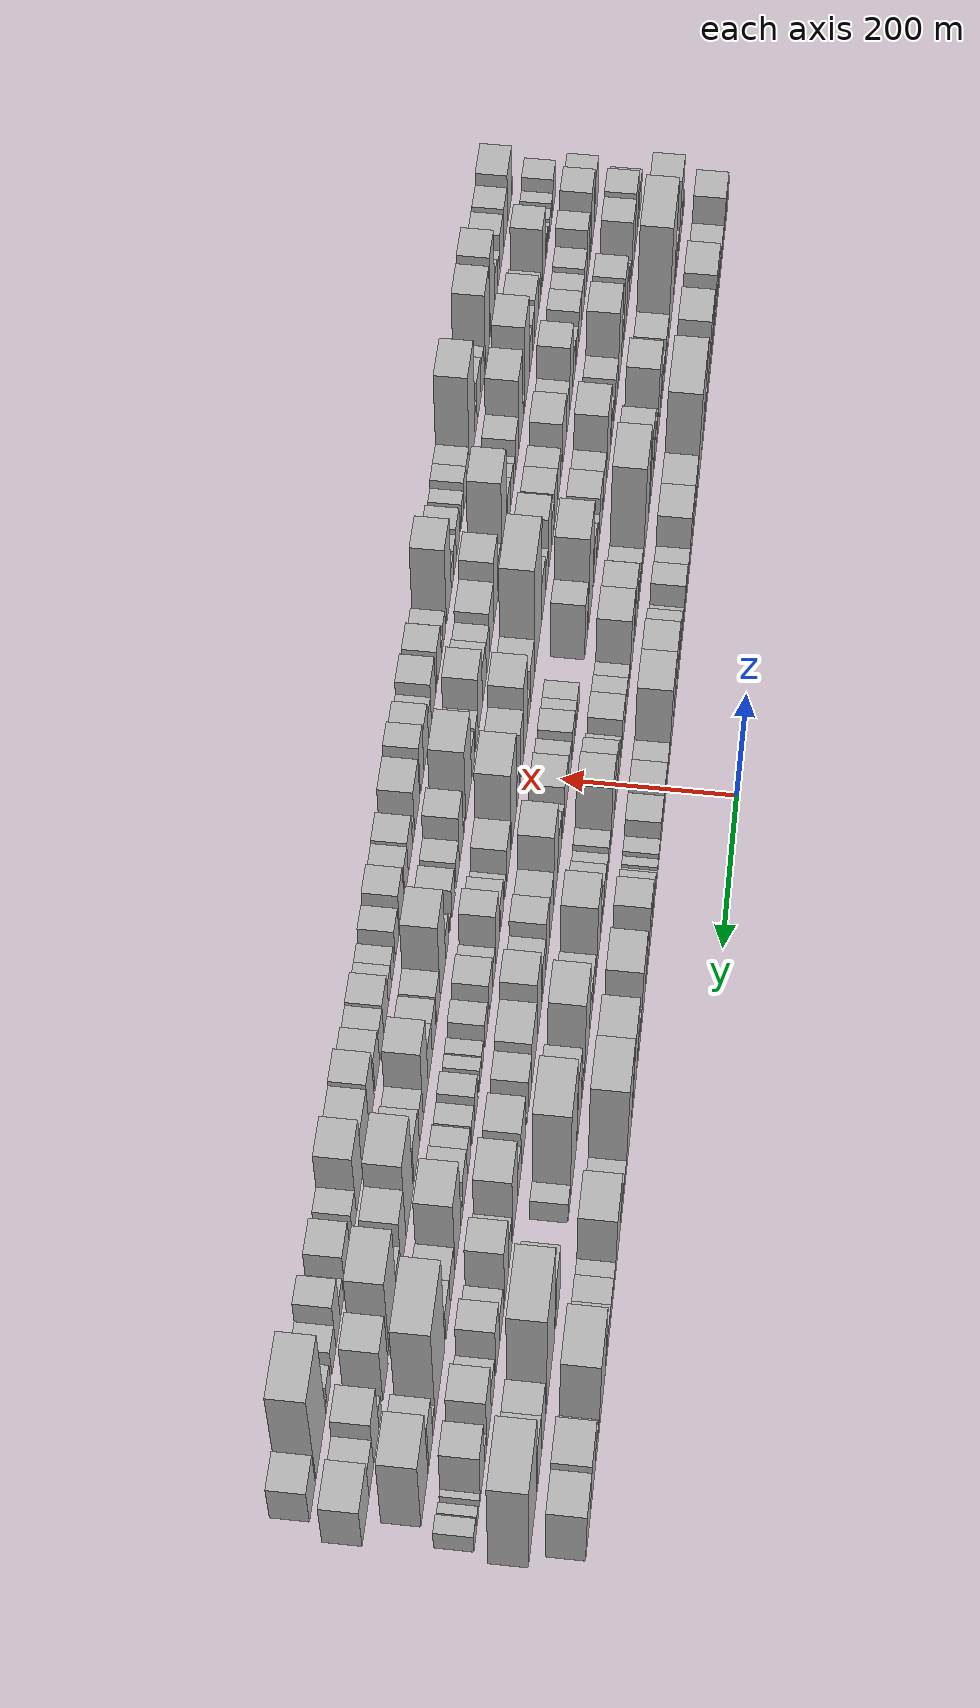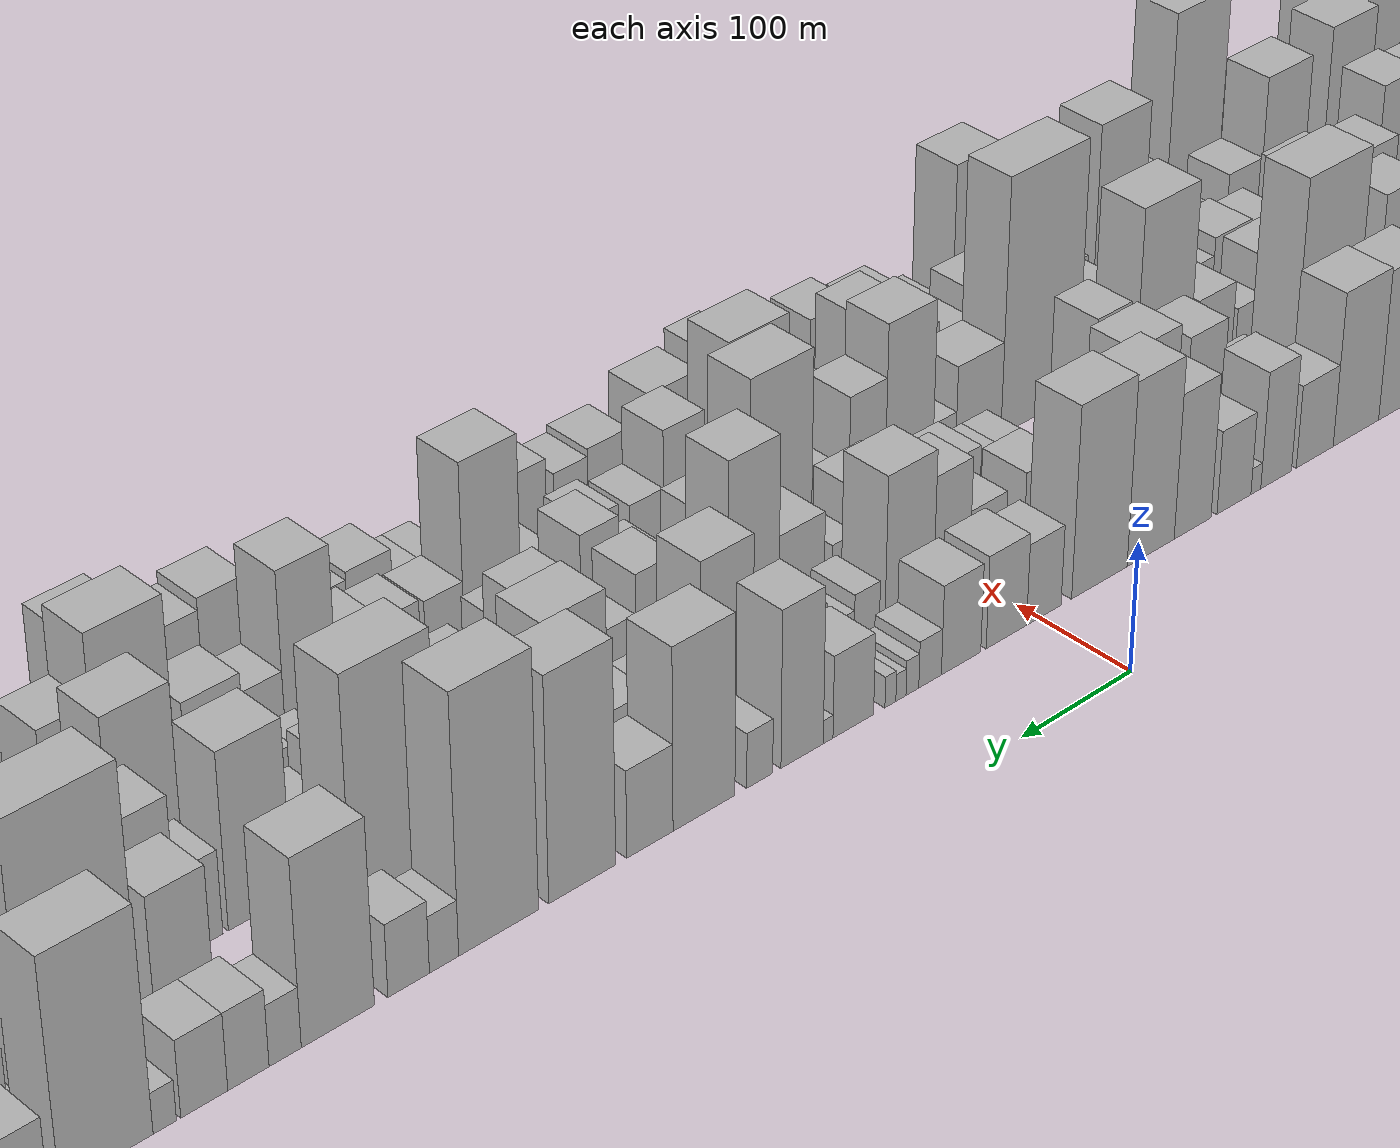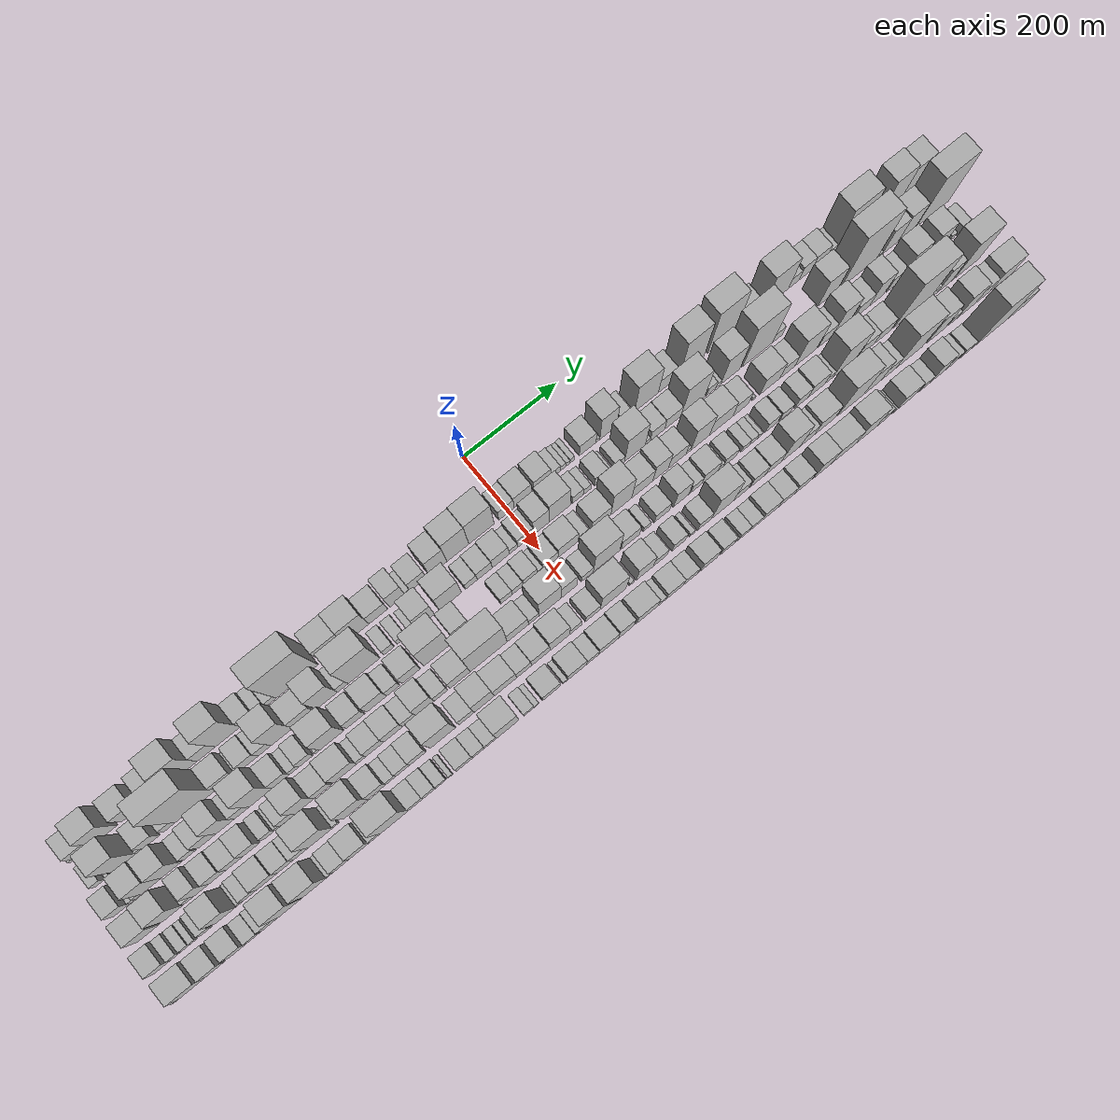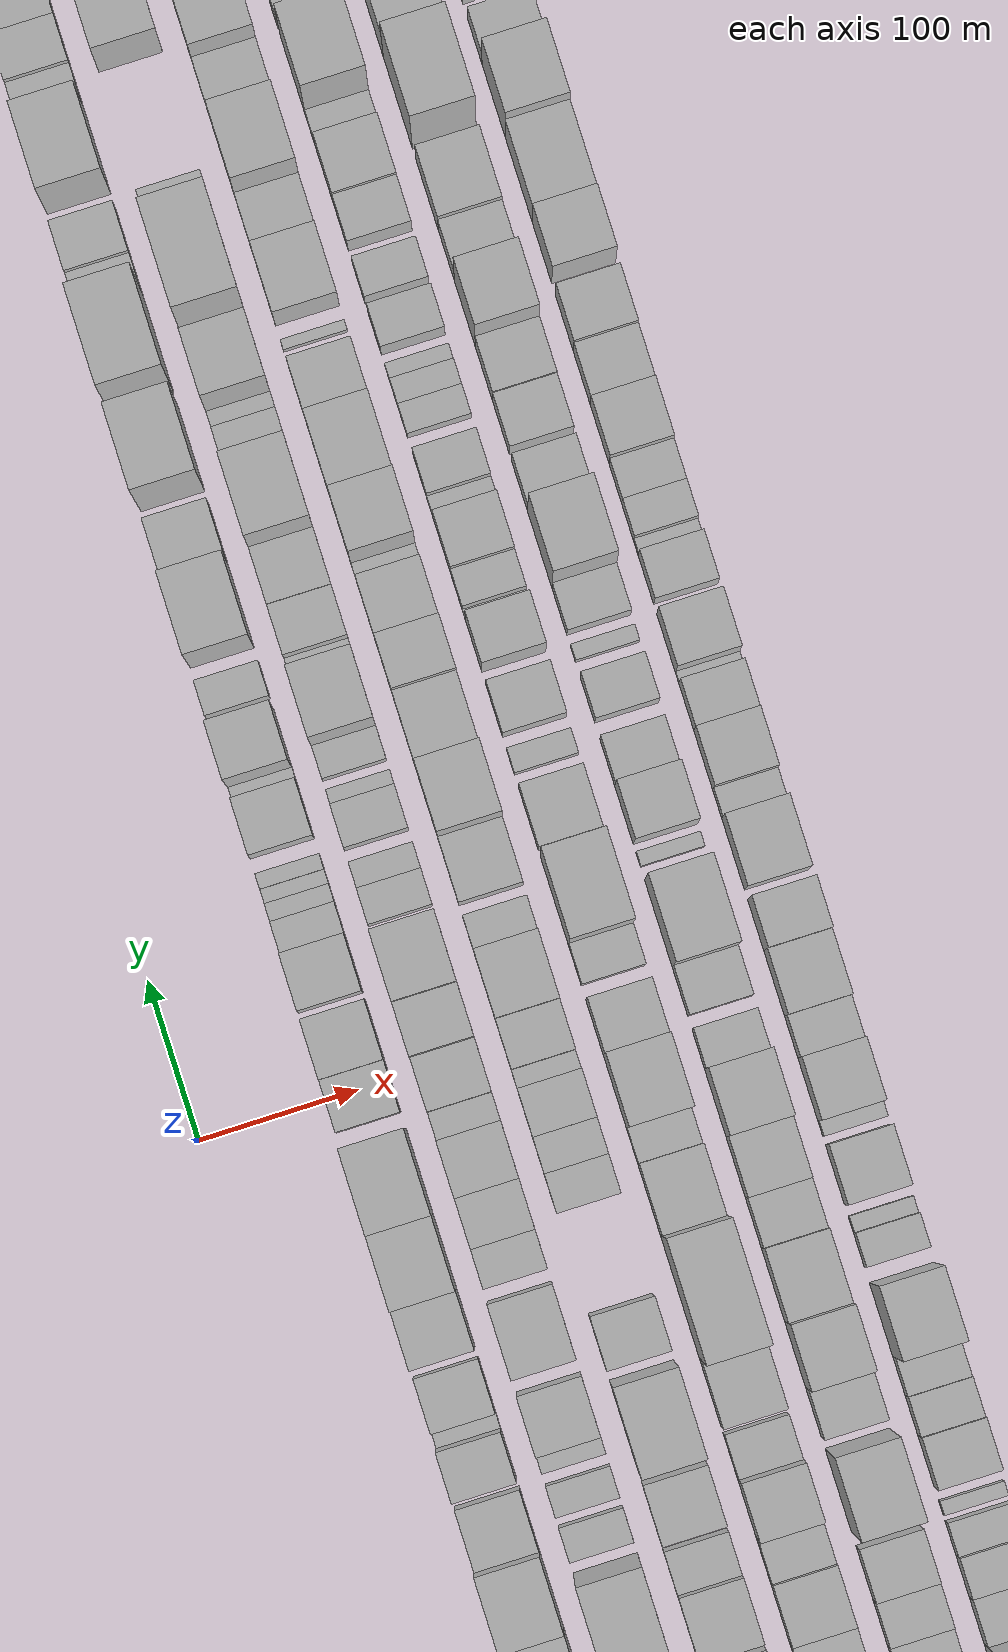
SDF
<sdf version="1.6">
 <world name="default">
  <scene>
   <sky><clouds><speed>12</speed></clouds></sky>
   <ambient>0.4 0.4 0.4 1</ambient>
   <background>0.7 0.7 0.7 1</background>
   <shadows>1</shadows>
  </scene>
  <gravity>0 0 -9.8066</gravity>
  <magnetic_field>6e-06 2.3e-05 -4.2e-05</magnetic_field>
  <physics default="0" name="default_physics" type="ode">
   <ode>
    <solver>
     <type>quick</type>
     <iters>10</iters>
     <sor>1.0</sor>
     <use_dynamic_moi_rescaling>0</use_dynamic_moi_rescaling>
    </solver>
    <constraints>
     <cfm>0</cfm>
     <erp>0.2</erp>
     <contact_max_correcting_vel>100</contact_max_correcting_vel>
     <contact_surface_layer>0.001</contact_surface_layer>
    </constraints>
   </ode>
   <max_step_size>0.004</max_step_size>
   <real_time_factor>1</real_time_factor>
   <real_time_update_rate>250</real_time_update_rate>
  </physics>
  <light name="sun" type="directional">
   <pose>0 0 10 0 0 0</pose>
   <diffuse>0.8 0.8 0.8 1</diffuse>
   <specular>0.2 0.2 0.2 1</specular>
   <attenuation>
    <range>1000</range>
    <constant>0.9</constant>
    <linear>0.01</linear>
    <quadratic>0.001</quadratic>
   </attenuation>
   <direction>-0.5 0.1 -0.9</direction>
  </light>
  <model name="building_1">
   <static>1</static>
   <pose>100.0000 -885.8886 0 0.000000 0.000000 0.000000</pose>
   <link name="link">
    <pose>0 0 9.00 0 0 0</pose>
    <collision name="collision"><geometry><box><size>40.0000 8.2228 18.0000</size></box></geometry></collision>
    <visual name="visual">
     <cast_shadows>0</cast_shadows>
     <geometry><box><size>40.0000 8.2228 18.0000</size></box></geometry>
     <material>
      <script>
       <uri>model://HANNAS_wall/materials/scripts</uri>
       <uri>model://HANNAS_wall/materials/textures</uri>
       <name>vrc/HANNAS_wall</name>
      </script>
     </material>
    </visual>
   </link>
  </model>
  <model name="building_2">
   <static>1</static>
   <pose>100.0000 -862.1573 0 0.000000 0.000000 0.000000</pose>
   <link name="link">
    <pose>0 0 33.00 0 0 0</pose>
    <collision name="collision"><geometry><box><size>40.0000 39.2398 66.0000</size></box></geometry></collision>
    <visual name="visual">
     <cast_shadows>0</cast_shadows>
     <geometry><box><size>40.0000 39.2398 66.0000</size></box></geometry>
     <material>
      <script>
       <uri>model://HANNAS_wall/materials/scripts</uri>
       <uri>model://HANNAS_wall/materials/textures</uri>
       <name>vrc/HANNAS_wall</name>
      </script>
     </material>
    </visual>
   </link>
  </model>
  <model name="building_3">
   <static>1</static>
   <pose>100.0000 -820.3483 0 0.000000 0.000000 0.000000</pose>
   <link name="link">
    <pose>0 0 57.00 0 0 0</pose>
    <collision name="collision"><geometry><box><size>40.0000 44.3781 114.0000</size></box></geometry></collision>
    <visual name="visual">
     <cast_shadows>0</cast_shadows>
     <geometry><box><size>40.0000 44.3781 114.0000</size></box></geometry>
     <material>
      <script>
       <uri>model://HANNAS_wall/materials/scripts</uri>
       <uri>model://HANNAS_wall/materials/textures</uri>
       <name>vrc/HANNAS_wall</name>
      </script>
     </material>
    </visual>
   </link>
  </model>
  <model name="building_4">
   <static>1</static>
   <pose>100.0000 -768.0062 0 0.000000 0.000000 0.000000</pose>
   <link name="link">
    <pose>0 0 37.50 0 0 0</pose>
    <collision name="collision"><geometry><box><size>40.0000 42.3063 75.0000</size></box></geometry></collision>
    <visual name="visual">
     <cast_shadows>0</cast_shadows>
     <geometry><box><size>40.0000 42.3063 75.0000</size></box></geometry>
     <material>
      <script>
       <uri>model://HANNAS_wall/materials/scripts</uri>
       <uri>model://HANNAS_wall/materials/textures</uri>
       <name>vrc/HANNAS_wall</name>
      </script>
     </material>
    </visual>
   </link>
  </model>
  <model name="building_5">
   <static>1</static>
   <pose>100.0000 -736.7441 0 0.000000 0.000000 0.000000</pose>
   <link name="link">
    <pose>0 0 10.50 0 0 0</pose>
    <collision name="collision"><geometry><box><size>40.0000 10.2178 21.0000</size></box></geometry></collision>
    <visual name="visual">
     <cast_shadows>0</cast_shadows>
     <geometry><box><size>40.0000 10.2178 21.0000</size></box></geometry>
     <material>
      <script>
       <uri>model://HANNAS_wall/materials/scripts</uri>
       <uri>model://HANNAS_wall/materials/textures</uri>
       <name>vrc/HANNAS_wall</name>
      </script>
     </material>
    </visual>
   </link>
  </model>
  <model name="building_6">
   <static>1</static>
   <pose>100.0000 -711.2774 0 0.000000 0.000000 0.000000</pose>
   <link name="link">
    <pose>0 0 40.50 0 0 0</pose>
    <collision name="collision"><geometry><box><size>40.0000 40.7158 81.0000</size></box></geometry></collision>
    <visual name="visual">
     <cast_shadows>0</cast_shadows>
     <geometry><box><size>40.0000 40.7158 81.0000</size></box></geometry>
     <material>
      <script>
       <uri>model://HANNAS_wall/materials/scripts</uri>
       <uri>model://HANNAS_wall/materials/textures</uri>
       <name>vrc/HANNAS_wall</name>
      </script>
     </material>
    </visual>
   </link>
  </model>
  <model name="building_7">
   <static>1</static>
   <pose>100.0000 -665.0568 0 0.000000 0.000000 0.000000</pose>
   <link name="link">
    <pose>0 0 75.00 0 0 0</pose>
    <collision name="collision"><geometry><box><size>40.0000 51.7253 150.0000</size></box></geometry></collision>
    <visual name="visual">
     <cast_shadows>0</cast_shadows>
     <geometry><box><size>40.0000 51.7253 150.0000</size></box></geometry>
     <material>
      <script>
       <uri>model://HANNAS_wall/materials/scripts</uri>
       <uri>model://HANNAS_wall/materials/textures</uri>
       <name>vrc/HANNAS_wall</name>
      </script>
     </material>
    </visual>
   </link>
  </model>
  <model name="building_8">
   <static>1</static>
   <pose>100.0000 -621.4893 0 0.000000 0.000000 0.000000</pose>
   <link name="link">
    <pose>0 0 34.50 0 0 0</pose>
    <collision name="collision"><geometry><box><size>40.0000 35.4097 69.0000</size></box></geometry></collision>
    <visual name="visual">
     <cast_shadows>0</cast_shadows>
     <geometry><box><size>40.0000 35.4097 69.0000</size></box></geometry>
     <material>
      <script>
       <uri>model://HANNAS_wall/materials/scripts</uri>
       <uri>model://HANNAS_wall/materials/textures</uri>
       <name>vrc/HANNAS_wall</name>
      </script>
     </material>
    </visual>
   </link>
  </model>
  <model name="building_9">
   <static>1</static>
   <pose>100.0000 -578.0950 0 0.000000 0.000000 0.000000</pose>
   <link name="link">
    <pose>0 0 82.50 0 0 0</pose>
    <collision name="collision"><geometry><box><size>40.0000 51.3789 165.0000</size></box></geometry></collision>
    <visual name="visual">
     <cast_shadows>0</cast_shadows>
     <geometry><box><size>40.0000 51.3789 165.0000</size></box></geometry>
     <material>
      <script>
       <uri>model://HANNAS_wall/materials/scripts</uri>
       <uri>model://HANNAS_wall/materials/textures</uri>
       <name>vrc/HANNAS_wall</name>
      </script>
     </material>
    </visual>
   </link>
  </model>
  <model name="building_10">
   <static>1</static>
   <pose>100.0000 -536.9174 0 0.000000 0.000000 0.000000</pose>
   <link name="link">
    <pose>0 0 28.50 0 0 0</pose>
    <collision name="collision"><geometry><box><size>40.0000 30.9762 57.0000</size></box></geometry></collision>
    <visual name="visual">
     <cast_shadows>0</cast_shadows>
     <geometry><box><size>40.0000 30.9762 57.0000</size></box></geometry>
     <material>
      <script>
       <uri>model://HANNAS_wall/materials/scripts</uri>
       <uri>model://HANNAS_wall/materials/textures</uri>
       <name>vrc/HANNAS_wall</name>
      </script>
     </material>
    </visual>
   </link>
  </model>
  <model name="building_11">
   <static>1</static>
   <pose>100.0000 -511.2003 0 0.000000 0.000000 0.000000</pose>
   <link name="link">
    <pose>0 0 19.50 0 0 0</pose>
    <collision name="collision"><geometry><box><size>40.0000 20.4582 39.0000</size></box></geometry></collision>
    <visual name="visual">
     <cast_shadows>0</cast_shadows>
     <geometry><box><size>40.0000 20.4582 39.0000</size></box></geometry>
     <material>
      <script>
       <uri>model://HANNAS_wall/materials/scripts</uri>
       <uri>model://HANNAS_wall/materials/textures</uri>
       <name>vrc/HANNAS_wall</name>
      </script>
     </material>
    </visual>
   </link>
  </model>
  <model name="building_12">
   <static>1</static>
   <pose>100.0000 -491.1092 0 0.000000 0.000000 0.000000</pose>
   <link name="link">
    <pose>0 0 16.50 0 0 0</pose>
    <collision name="collision"><geometry><box><size>40.0000 19.7239 33.0000</size></box></geometry></collision>
    <visual name="visual">
     <cast_shadows>0</cast_shadows>
     <geometry><box><size>40.0000 19.7239 33.0000</size></box></geometry>
     <material>
      <script>
       <uri>model://HANNAS_wall/materials/scripts</uri>
       <uri>model://HANNAS_wall/materials/textures</uri>
       <name>vrc/HANNAS_wall</name>
      </script>
     </material>
    </visual>
   </link>
  </model>
  <model name="building_13">
   <static>1</static>
   <pose>100.0000 -438.6262 0 0.000000 0.000000 0.000000</pose>
   <link name="link">
    <pose>0 0 109.50 0 0 0</pose>
    <collision name="collision"><geometry><box><size>40.0000 85.2422 219.0000</size></box></geometry></collision>
    <visual name="visual">
     <cast_shadows>0</cast_shadows>
     <geometry><box><size>40.0000 85.2422 219.0000</size></box></geometry>
     <material>
      <script>
       <uri>model://HANNAS_wall/materials/scripts</uri>
       <uri>model://HANNAS_wall/materials/textures</uri>
       <name>vrc/HANNAS_wall</name>
      </script>
     </material>
    </visual>
   </link>
  </model>
  <model name="building_14">
   <static>1</static>
   <pose>100.0000 -363.2224 0 0.000000 0.000000 0.000000</pose>
   <link name="link">
    <pose>0 0 60.00 0 0 0</pose>
    <collision name="collision"><geometry><box><size>40.0000 47.5653 120.0000</size></box></geometry></collision>
    <visual name="visual">
     <cast_shadows>0</cast_shadows>
     <geometry><box><size>40.0000 47.5653 120.0000</size></box></geometry>
     <material>
      <script>
       <uri>model://HANNAS_wall/materials/scripts</uri>
       <uri>model://HANNAS_wall/materials/textures</uri>
       <name>vrc/HANNAS_wall</name>
      </script>
     </material>
    </visual>
   </link>
  </model>
  <model name="building_15">
   <static>1</static>
   <pose>100.0000 -315.4356 0 0.000000 0.000000 0.000000</pose>
   <link name="link">
    <pose>0 0 61.50 0 0 0</pose>
    <collision name="collision"><geometry><box><size>40.0000 48.0083 123.0000</size></box></geometry></collision>
    <visual name="visual">
     <cast_shadows>0</cast_shadows>
     <geometry><box><size>40.0000 48.0083 123.0000</size></box></geometry>
     <material>
      <script>
       <uri>model://HANNAS_wall/materials/scripts</uri>
       <uri>model://HANNAS_wall/materials/textures</uri>
       <name>vrc/HANNAS_wall</name>
      </script>
     </material>
    </visual>
   </link>
  </model>
  <model name="building_16">
   <static>1</static>
   <pose>100.0000 -272.2559 0 0.000000 0.000000 0.000000</pose>
   <link name="link">
    <pose>0 0 33.00 0 0 0</pose>
    <collision name="collision"><geometry><box><size>40.0000 38.3510 66.0000</size></box></geometry></collision>
    <visual name="visual">
     <cast_shadows>0</cast_shadows>
     <geometry><box><size>40.0000 38.3510 66.0000</size></box></geometry>
     <material>
      <script>
       <uri>model://HANNAS_wall/materials/scripts</uri>
       <uri>model://HANNAS_wall/materials/textures</uri>
       <name>vrc/HANNAS_wall</name>
      </script>
     </material>
    </visual>
   </link>
  </model>
  <model name="building_17">
   <static>1</static>
   <pose>100.0000 -232.3339 0 0.000000 0.000000 0.000000</pose>
   <link name="link">
    <pose>0 0 46.50 0 0 0</pose>
    <collision name="collision"><geometry><box><size>40.0000 31.4930 93.0000</size></box></geometry></collision>
    <visual name="visual">
     <cast_shadows>0</cast_shadows>
     <geometry><box><size>40.0000 31.4930 93.0000</size></box></geometry>
     <material>
      <script>
       <uri>model://HANNAS_wall/materials/scripts</uri>
       <uri>model://HANNAS_wall/materials/textures</uri>
       <name>vrc/HANNAS_wall</name>
      </script>
     </material>
    </visual>
   </link>
  </model>
  <model name="building_18">
   <static>1</static>
   <pose>100.0000 -211.5624 0 0.000000 0.000000 0.000000</pose>
   <link name="link">
    <pose>0 0 10.50 0 0 0</pose>
    <collision name="collision"><geometry><box><size>40.0000 10.0500 21.0000</size></box></geometry></collision>
    <visual name="visual">
     <cast_shadows>0</cast_shadows>
     <geometry><box><size>40.0000 10.0500 21.0000</size></box></geometry>
     <material>
      <script>
       <uri>model://HANNAS_wall/materials/scripts</uri>
       <uri>model://HANNAS_wall/materials/textures</uri>
       <name>vrc/HANNAS_wall</name>
      </script>
     </material>
    </visual>
   </link>
  </model>
  <model name="building_19">
   <static>1</static>
   <pose>100.0000 -189.4465 0 0.000000 0.000000 0.000000</pose>
   <link name="link">
    <pose>0 0 33.00 0 0 0</pose>
    <collision name="collision"><geometry><box><size>40.0000 34.1818 66.0000</size></box></geometry></collision>
    <visual name="visual">
     <cast_shadows>0</cast_shadows>
     <geometry><box><size>40.0000 34.1818 66.0000</size></box></geometry>
     <material>
      <script>
       <uri>model://HANNAS_wall/materials/scripts</uri>
       <uri>model://HANNAS_wall/materials/textures</uri>
       <name>vrc/HANNAS_wall</name>
      </script>
     </material>
    </visual>
   </link>
  </model>
  <model name="building_20">
   <static>1</static>
   <pose>100.0000 -148.0742 0 0.000000 0.000000 0.000000</pose>
   <link name="link">
    <pose>0 0 57.00 0 0 0</pose>
    <collision name="collision"><geometry><box><size>40.0000 36.5627 114.0000</size></box></geometry></collision>
    <visual name="visual">
     <cast_shadows>0</cast_shadows>
     <geometry><box><size>40.0000 36.5627 114.0000</size></box></geometry>
     <material>
      <script>
       <uri>model://HANNAS_wall/materials/scripts</uri>
       <uri>model://HANNAS_wall/materials/textures</uri>
       <name>vrc/HANNAS_wall</name>
      </script>
     </material>
    </visual>
   </link>
  </model>
  <model name="building_21">
   <static>1</static>
   <pose>100.0000 -106.7754 0 0.000000 0.000000 0.000000</pose>
   <link name="link">
    <pose>0 0 72.00 0 0 0</pose>
    <collision name="collision"><geometry><box><size>40.0000 46.0349 144.0000</size></box></geometry></collision>
    <visual name="visual">
     <cast_shadows>0</cast_shadows>
     <geometry><box><size>40.0000 46.0349 144.0000</size></box></geometry>
     <material>
      <script>
       <uri>model://HANNAS_wall/materials/scripts</uri>
       <uri>model://HANNAS_wall/materials/textures</uri>
       <name>vrc/HANNAS_wall</name>
      </script>
     </material>
    </visual>
   </link>
  </model>
  <model name="building_22">
   <static>1</static>
   <pose>100.0000 -57.1790 0 0.000000 0.000000 0.000000</pose>
   <link name="link">
    <pose>0 0 75.00 0 0 0</pose>
    <collision name="collision"><geometry><box><size>40.0000 53.1579 150.0000</size></box></geometry></collision>
    <visual name="visual">
     <cast_shadows>0</cast_shadows>
     <geometry><box><size>40.0000 53.1579 150.0000</size></box></geometry>
     <material>
      <script>
       <uri>model://HANNAS_wall/materials/scripts</uri>
       <uri>model://HANNAS_wall/materials/textures</uri>
       <name>vrc/HANNAS_wall</name>
      </script>
     </material>
    </visual>
   </link>
  </model>
  <model name="building_23">
   <static>1</static>
   <pose>100.0000 -4.4070 0 0.000000 0.000000 0.000000</pose>
   <link name="link">
    <pose>0 0 31.50 0 0 0</pose>
    <collision name="collision"><geometry><box><size>40.0000 32.3861 63.0000</size></box></geometry></collision>
    <visual name="visual">
     <cast_shadows>0</cast_shadows>
     <geometry><box><size>40.0000 32.3861 63.0000</size></box></geometry>
     <material>
      <script>
       <uri>model://HANNAS_wall/materials/scripts</uri>
       <uri>model://HANNAS_wall/materials/textures</uri>
       <name>vrc/HANNAS_wall</name>
      </script>
     </material>
    </visual>
   </link>
  </model>
  <model name="building_24">
   <static>1</static>
   <pose>100.0000 30.4983 0 0.000000 0.000000 0.000000</pose>
   <link name="link">
    <pose>0 0 36.00 0 0 0</pose>
    <collision name="collision"><geometry><box><size>40.0000 37.4245 72.0000</size></box></geometry></collision>
    <visual name="visual">
     <cast_shadows>0</cast_shadows>
     <geometry><box><size>40.0000 37.4245 72.0000</size></box></geometry>
     <material>
      <script>
       <uri>model://HANNAS_wall/materials/scripts</uri>
       <uri>model://HANNAS_wall/materials/textures</uri>
       <name>vrc/HANNAS_wall</name>
      </script>
     </material>
    </visual>
   </link>
  </model>
  <model name="building_25">
   <static>1</static>
   <pose>100.0000 72.1204 0 0.000000 0.000000 0.000000</pose>
   <link name="link">
    <pose>0 0 34.50 0 0 0</pose>
    <collision name="collision"><geometry><box><size>40.0000 35.8198 69.0000</size></box></geometry></collision>
    <visual name="visual">
     <cast_shadows>0</cast_shadows>
     <geometry><box><size>40.0000 35.8198 69.0000</size></box></geometry>
     <material>
      <script>
       <uri>model://HANNAS_wall/materials/scripts</uri>
       <uri>model://HANNAS_wall/materials/textures</uri>
       <name>vrc/HANNAS_wall</name>
      </script>
     </material>
    </visual>
   </link>
  </model>
  <model name="building_26">
   <static>1</static>
   <pose>100.0000 100.2217 0 0.000000 0.000000 0.000000</pose>
   <link name="link">
    <pose>0 0 18.00 0 0 0</pose>
    <collision name="collision"><geometry><box><size>40.0000 20.3829 36.0000</size></box></geometry></collision>
    <visual name="visual">
     <cast_shadows>0</cast_shadows>
     <geometry><box><size>40.0000 20.3829 36.0000</size></box></geometry>
     <material>
      <script>
       <uri>model://HANNAS_wall/materials/scripts</uri>
       <uri>model://HANNAS_wall/materials/textures</uri>
       <name>vrc/HANNAS_wall</name>
      </script>
     </material>
    </visual>
   </link>
  </model>
  <model name="building_27">
   <static>1</static>
   <pose>100.0000 116.1335 0 0.000000 0.000000 0.000000</pose>
   <link name="link">
    <pose>0 0 13.50 0 0 0</pose>
    <collision name="collision"><geometry><box><size>40.0000 11.4406 27.0000</size></box></geometry></collision>
    <visual name="visual">
     <cast_shadows>0</cast_shadows>
     <geometry><box><size>40.0000 11.4406 27.0000</size></box></geometry>
     <material>
      <script>
       <uri>model://HANNAS_wall/materials/scripts</uri>
       <uri>model://HANNAS_wall/materials/textures</uri>
       <name>vrc/HANNAS_wall</name>
      </script>
     </material>
    </visual>
   </link>
  </model>
  <model name="building_28">
   <static>1</static>
   <pose>100.0000 126.3763 0 0.000000 0.000000 0.000000</pose>
   <link name="link">
    <pose>0 0 10.50 0 0 0</pose>
    <collision name="collision"><geometry><box><size>40.0000 9.0448 21.0000</size></box></geometry></collision>
    <visual name="visual">
     <cast_shadows>0</cast_shadows>
     <geometry><box><size>40.0000 9.0448 21.0000</size></box></geometry>
     <material>
      <script>
       <uri>model://HANNAS_wall/materials/scripts</uri>
       <uri>model://HANNAS_wall/materials/textures</uri>
       <name>vrc/HANNAS_wall</name>
      </script>
     </material>
    </visual>
   </link>
  </model>
  <model name="building_29">
   <static>1</static>
   <pose>100.0000 135.7684 0 0.000000 0.000000 0.000000</pose>
   <link name="link">
    <pose>0 0 12.00 0 0 0</pose>
    <collision name="collision"><geometry><box><size>40.0000 9.7394 24.0000</size></box></geometry></collision>
    <visual name="visual">
     <cast_shadows>0</cast_shadows>
     <geometry><box><size>40.0000 9.7394 24.0000</size></box></geometry>
     <material>
      <script>
       <uri>model://HANNAS_wall/materials/scripts</uri>
       <uri>model://HANNAS_wall/materials/textures</uri>
       <name>vrc/HANNAS_wall</name>
      </script>
     </material>
    </visual>
   </link>
  </model>
  <model name="building_30">
   <static>1</static>
   <pose>100.0000 168.4412 0 0.000000 0.000000 0.000000</pose>
   <link name="link">
    <pose>0 0 31.50 0 0 0</pose>
    <collision name="collision"><geometry><box><size>40.0000 35.6063 63.0000</size></box></geometry></collision>
    <visual name="visual">
     <cast_shadows>0</cast_shadows>
     <geometry><box><size>40.0000 35.6063 63.0000</size></box></geometry>
     <material>
      <script>
       <uri>model://HANNAS_wall/materials/scripts</uri>
       <uri>model://HANNAS_wall/materials/textures</uri>
       <name>vrc/HANNAS_wall</name>
      </script>
     </material>
    </visual>
   </link>
  </model>
  <model name="building_31">
   <static>1</static>
   <pose>100.0000 190.4567 0 0.000000 0.000000 0.000000</pose>
   <link name="link">
    <pose>0 0 9.00 0 0 0</pose>
    <collision name="collision"><geometry><box><size>40.0000 8.4245 18.0000</size></box></geometry></collision>
    <visual name="visual">
     <cast_shadows>0</cast_shadows>
     <geometry><box><size>40.0000 8.4245 18.0000</size></box></geometry>
     <material>
      <script>
       <uri>model://HANNAS_wall/materials/scripts</uri>
       <uri>model://HANNAS_wall/materials/textures</uri>
       <name>vrc/HANNAS_wall</name>
      </script>
     </material>
    </visual>
   </link>
  </model>
  <model name="building_32">
   <static>1</static>
   <pose>100.0000 212.8879 0 0.000000 0.000000 0.000000</pose>
   <link name="link">
    <pose>0 0 60.00 0 0 0</pose>
    <collision name="collision"><geometry><box><size>40.0000 36.4380 120.0000</size></box></geometry></collision>
    <visual name="visual">
     <cast_shadows>0</cast_shadows>
     <geometry><box><size>40.0000 36.4380 120.0000</size></box></geometry>
     <material>
      <script>
       <uri>model://HANNAS_wall/materials/scripts</uri>
       <uri>model://HANNAS_wall/materials/textures</uri>
       <name>vrc/HANNAS_wall</name>
      </script>
     </material>
    </visual>
   </link>
  </model>
  <model name="building_33">
   <static>1</static>
   <pose>100.0000 249.1040 0 0.000000 0.000000 0.000000</pose>
   <link name="link">
    <pose>0 0 21.00 0 0 0</pose>
    <collision name="collision"><geometry><box><size>40.0000 21.9940 42.0000</size></box></geometry></collision>
    <visual name="visual">
     <cast_shadows>0</cast_shadows>
     <geometry><box><size>40.0000 21.9940 42.0000</size></box></geometry>
     <material>
      <script>
       <uri>model://HANNAS_wall/materials/scripts</uri>
       <uri>model://HANNAS_wall/materials/textures</uri>
       <name>vrc/HANNAS_wall</name>
      </script>
     </material>
    </visual>
   </link>
  </model>
  <model name="building_34">
   <static>1</static>
   <pose>100.0000 295.8388 0 0.000000 0.000000 0.000000</pose>
   <link name="link">
    <pose>0 0 69.00 0 0 0</pose>
    <collision name="collision"><geometry><box><size>40.0000 51.4757 138.0000</size></box></geometry></collision>
    <visual name="visual">
     <cast_shadows>0</cast_shadows>
     <geometry><box><size>40.0000 51.4757 138.0000</size></box></geometry>
     <material>
      <script>
       <uri>model://HANNAS_wall/materials/scripts</uri>
       <uri>model://HANNAS_wall/materials/textures</uri>
       <name>vrc/HANNAS_wall</name>
      </script>
     </material>
    </visual>
   </link>
  </model>
  <model name="building_35">
   <static>1</static>
   <pose>100.0000 340.4338 0 0.000000 0.000000 0.000000</pose>
   <link name="link">
    <pose>0 0 33.00 0 0 0</pose>
    <collision name="collision"><geometry><box><size>40.0000 37.7142 66.0000</size></box></geometry></collision>
    <visual name="visual">
     <cast_shadows>0</cast_shadows>
     <geometry><box><size>40.0000 37.7142 66.0000</size></box></geometry>
     <material>
      <script>
       <uri>model://HANNAS_wall/materials/scripts</uri>
       <uri>model://HANNAS_wall/materials/textures</uri>
       <name>vrc/HANNAS_wall</name>
      </script>
     </material>
    </visual>
   </link>
  </model>
  <model name="building_36">
   <static>1</static>
   <pose>100.0000 395.0340 0 0.000000 0.000000 0.000000</pose>
   <link name="link">
    <pose>0 0 84.00 0 0 0</pose>
    <collision name="collision"><geometry><box><size>40.0000 53.4863 168.0000</size></box></geometry></collision>
    <visual name="visual">
     <cast_shadows>0</cast_shadows>
     <geometry><box><size>40.0000 53.4863 168.0000</size></box></geometry>
     <material>
      <script>
       <uri>model://HANNAS_wall/materials/scripts</uri>
       <uri>model://HANNAS_wall/materials/textures</uri>
       <name>vrc/HANNAS_wall</name>
      </script>
     </material>
    </visual>
   </link>
  </model>
  <model name="building_37">
   <static>1</static>
   <pose>100.0000 460.7381 0 0.000000 0.000000 0.000000</pose>
   <link name="link">
    <pose>0 0 96.00 0 0 0</pose>
    <collision name="collision"><geometry><box><size>40.0000 61.9219 192.0000</size></box></geometry></collision>
    <visual name="visual">
     <cast_shadows>0</cast_shadows>
     <geometry><box><size>40.0000 61.9219 192.0000</size></box></geometry>
     <material>
      <script>
       <uri>model://HANNAS_wall/materials/scripts</uri>
       <uri>model://HANNAS_wall/materials/textures</uri>
       <name>vrc/HANNAS_wall</name>
      </script>
     </material>
    </visual>
   </link>
  </model>
  <model name="building_38">
   <static>1</static>
   <pose>100.0000 502.8438 0 0.000000 0.000000 0.000000</pose>
   <link name="link">
    <pose>0 0 21.00 0 0 0</pose>
    <collision name="collision"><geometry><box><size>40.0000 22.2894 42.0000</size></box></geometry></collision>
    <visual name="visual">
     <cast_shadows>0</cast_shadows>
     <geometry><box><size>40.0000 22.2894 42.0000</size></box></geometry>
     <material>
      <script>
       <uri>model://HANNAS_wall/materials/scripts</uri>
       <uri>model://HANNAS_wall/materials/textures</uri>
       <name>vrc/HANNAS_wall</name>
      </script>
     </material>
    </visual>
   </link>
  </model>
  <model name="building_39">
   <static>1</static>
   <pose>100.0000 529.6292 0 0.000000 0.000000 0.000000</pose>
   <link name="link">
    <pose>0 0 27.00 0 0 0</pose>
    <collision name="collision"><geometry><box><size>40.0000 31.2812 54.0000</size></box></geometry></collision>
    <visual name="visual">
     <cast_shadows>0</cast_shadows>
     <geometry><box><size>40.0000 31.2812 54.0000</size></box></geometry>
     <material>
      <script>
       <uri>model://HANNAS_wall/materials/scripts</uri>
       <uri>model://HANNAS_wall/materials/textures</uri>
       <name>vrc/HANNAS_wall</name>
      </script>
     </material>
    </visual>
   </link>
  </model>
  <model name="building_40">
   <static>1</static>
   <pose>100.0000 582.1873 0 0.000000 0.000000 0.000000</pose>
   <link name="link">
    <pose>0 0 69.00 0 0 0</pose>
    <collision name="collision"><geometry><box><size>40.0000 53.8350 138.0000</size></box></geometry></collision>
    <visual name="visual">
     <cast_shadows>0</cast_shadows>
     <geometry><box><size>40.0000 53.8350 138.0000</size></box></geometry>
     <material>
      <script>
       <uri>model://HANNAS_wall/materials/scripts</uri>
       <uri>model://HANNAS_wall/materials/textures</uri>
       <name>vrc/HANNAS_wall</name>
      </script>
     </material>
    </visual>
   </link>
  </model>
  <model name="building_41">
   <static>1</static>
   <pose>100.0000 620.7428 0 0.000000 0.000000 0.000000</pose>
   <link name="link">
    <pose>0 0 22.50 0 0 0</pose>
    <collision name="collision"><geometry><box><size>40.0000 23.2760 45.0000</size></box></geometry></collision>
    <visual name="visual">
     <cast_shadows>0</cast_shadows>
     <geometry><box><size>40.0000 23.2760 45.0000</size></box></geometry>
     <material>
      <script>
       <uri>model://HANNAS_wall/materials/scripts</uri>
       <uri>model://HANNAS_wall/materials/textures</uri>
       <name>vrc/HANNAS_wall</name>
      </script>
     </material>
    </visual>
   </link>
  </model>
  <model name="building_42">
   <static>1</static>
   <pose>100.0000 647.1225 0 0.000000 0.000000 0.000000</pose>
   <link name="link">
    <pose>0 0 28.50 0 0 0</pose>
    <collision name="collision"><geometry><box><size>40.0000 29.4835 57.0000</size></box></geometry></collision>
    <visual name="visual">
     <cast_shadows>0</cast_shadows>
     <geometry><box><size>40.0000 29.4835 57.0000</size></box></geometry>
     <material>
      <script>
       <uri>model://HANNAS_wall/materials/scripts</uri>
       <uri>model://HANNAS_wall/materials/textures</uri>
       <name>vrc/HANNAS_wall</name>
      </script>
     </material>
    </visual>
   </link>
  </model>
  <model name="building_43">
   <static>1</static>
   <pose>100.0000 678.4469 0 0.000000 0.000000 0.000000</pose>
   <link name="link">
    <pose>0 0 28.50 0 0 0</pose>
    <collision name="collision"><geometry><box><size>40.0000 33.1653 57.0000</size></box></geometry></collision>
    <visual name="visual">
     <cast_shadows>0</cast_shadows>
     <geometry><box><size>40.0000 33.1653 57.0000</size></box></geometry>
     <material>
      <script>
       <uri>model://HANNAS_wall/materials/scripts</uri>
       <uri>model://HANNAS_wall/materials/textures</uri>
       <name>vrc/HANNAS_wall</name>
      </script>
     </material>
    </visual>
   </link>
  </model>
  <model name="building_44">
   <static>1</static>
   <pose>100.0000 706.1612 0 0.000000 0.000000 0.000000</pose>
   <link name="link">
    <pose>0 0 15.00 0 0 0</pose>
    <collision name="collision"><geometry><box><size>40.0000 16.2633 30.0000</size></box></geometry></collision>
    <visual name="visual">
     <cast_shadows>0</cast_shadows>
     <geometry><box><size>40.0000 16.2633 30.0000</size></box></geometry>
     <material>
      <script>
       <uri>model://HANNAS_wall/materials/scripts</uri>
       <uri>model://HANNAS_wall/materials/textures</uri>
       <name>vrc/HANNAS_wall</name>
      </script>
     </material>
    </visual>
   </link>
  </model>
  <model name="building_45">
   <static>1</static>
   <pose>100.0000 746.2240 0 0.000000 0.000000 0.000000</pose>
   <link name="link">
    <pose>0 0 82.50 0 0 0</pose>
    <collision name="collision"><geometry><box><size>40.0000 63.8623 165.0000</size></box></geometry></collision>
    <visual name="visual">
     <cast_shadows>0</cast_shadows>
     <geometry><box><size>40.0000 63.8623 165.0000</size></box></geometry>
     <material>
      <script>
       <uri>model://HANNAS_wall/materials/scripts</uri>
       <uri>model://HANNAS_wall/materials/textures</uri>
       <name>vrc/HANNAS_wall</name>
      </script>
     </material>
    </visual>
   </link>
  </model>
  <model name="building_46">
   <static>1</static>
   <pose>100.0000 781.9074 0 0.000000 0.000000 0.000000</pose>
   <link name="link">
    <pose>0 0 9.00 0 0 0</pose>
    <collision name="collision"><geometry><box><size>40.0000 7.5045 18.0000</size></box></geometry></collision>
    <visual name="visual">
     <cast_shadows>0</cast_shadows>
     <geometry><box><size>40.0000 7.5045 18.0000</size></box></geometry>
     <material>
      <script>
       <uri>model://HANNAS_wall/materials/scripts</uri>
       <uri>model://HANNAS_wall/materials/textures</uri>
       <name>vrc/HANNAS_wall</name>
      </script>
     </material>
    </visual>
   </link>
  </model>
  <model name="building_47">
   <static>1</static>
   <pose>100.0000 801.3336 0 0.000000 0.000000 0.000000</pose>
   <link name="link">
    <pose>0 0 28.50 0 0 0</pose>
    <collision name="collision"><geometry><box><size>40.0000 31.3480 57.0000</size></box></geometry></collision>
    <visual name="visual">
     <cast_shadows>0</cast_shadows>
     <geometry><box><size>40.0000 31.3480 57.0000</size></box></geometry>
     <material>
      <script>
       <uri>model://HANNAS_wall/materials/scripts</uri>
       <uri>model://HANNAS_wall/materials/textures</uri>
       <name>vrc/HANNAS_wall</name>
      </script>
     </material>
    </visual>
   </link>
  </model>
  <model name="building_48">
   <static>1</static>
   <pose>100.0000 840.8534 0 0.000000 0.000000 0.000000</pose>
   <link name="link">
    <pose>0 0 64.50 0 0 0</pose>
    <collision name="collision"><geometry><box><size>40.0000 47.6916 129.0000</size></box></geometry></collision>
    <visual name="visual">
     <cast_shadows>0</cast_shadows>
     <geometry><box><size>40.0000 47.6916 129.0000</size></box></geometry>
     <material>
      <script>
       <uri>model://HANNAS_wall/materials/scripts</uri>
       <uri>model://HANNAS_wall/materials/textures</uri>
       <name>vrc/HANNAS_wall</name>
      </script>
     </material>
    </visual>
   </link>
  </model>
  <model name="building_49">
   <static>1</static>
   <pose>100.0000 887.4541 0 0.000000 0.000000 0.000000</pose>
   <link name="link">
    <pose>0 0 57.00 0 0 0</pose>
    <collision name="collision"><geometry><box><size>40.0000 45.5097 114.0000</size></box></geometry></collision>
    <visual name="visual">
     <cast_shadows>0</cast_shadows>
     <geometry><box><size>40.0000 45.5097 114.0000</size></box></geometry>
     <material>
      <script>
       <uri>model://HANNAS_wall/materials/scripts</uri>
       <uri>model://HANNAS_wall/materials/textures</uri>
       <name>vrc/HANNAS_wall</name>
      </script>
     </material>
    </visual>
   </link>
  </model>
  <model name="building_50">
   <static>1</static>
   <pose>155.0000 -873.4948 0 0.000000 0.000000 0.000000</pose>
   <link name="link">
    <pose>0 0 16.50 0 0 0</pose>
    <collision name="collision"><geometry><box><size>40.0000 19.0104 33.0000</size></box></geometry></collision>
    <visual name="visual">
     <cast_shadows>0</cast_shadows>
     <geometry><box><size>40.0000 19.0104 33.0000</size></box></geometry>
     <material>
      <script>
       <uri>model://HANNAS_wall/materials/scripts</uri>
       <uri>model://HANNAS_wall/materials/textures</uri>
       <name>vrc/HANNAS_wall</name>
      </script>
     </material>
    </visual>
   </link>
  </model>
  <model name="building_51">
   <static>1</static>
   <pose>155.0000 -855.7284 0 0.000000 0.000000 0.000000</pose>
   <link name="link">
    <pose>0 0 7.50 0 0 0</pose>
    <collision name="collision"><geometry><box><size>40.0000 6.5225 15.0000</size></box></geometry></collision>
    <visual name="visual">
     <cast_shadows>0</cast_shadows>
     <geometry><box><size>40.0000 6.5225 15.0000</size></box></geometry>
     <material>
      <script>
       <uri>model://HANNAS_wall/materials/scripts</uri>
       <uri>model://HANNAS_wall/materials/textures</uri>
       <name>vrc/HANNAS_wall</name>
      </script>
     </material>
    </visual>
   </link>
  </model>
  <model name="building_52">
   <static>1</static>
   <pose>155.0000 -822.6581 0 0.000000 0.000000 0.000000</pose>
   <link name="link">
    <pose>0 0 67.50 0 0 0</pose>
    <collision name="collision"><geometry><box><size>40.0000 45.6182 135.0000</size></box></geometry></collision>
    <visual name="visual">
     <cast_shadows>0</cast_shadows>
     <geometry><box><size>40.0000 45.6182 135.0000</size></box></geometry>
     <material>
      <script>
       <uri>model://HANNAS_wall/materials/scripts</uri>
       <uri>model://HANNAS_wall/materials/textures</uri>
       <name>vrc/HANNAS_wall</name>
      </script>
     </material>
    </visual>
   </link>
  </model>
  <model name="building_53">
   <static>1</static>
   <pose>155.0000 -794.6449 0 0.000000 0.000000 0.000000</pose>
   <link name="link">
    <pose>0 0 10.50 0 0 0</pose>
    <collision name="collision"><geometry><box><size>40.0000 10.4082 21.0000</size></box></geometry></collision>
    <visual name="visual">
     <cast_shadows>0</cast_shadows>
     <geometry><box><size>40.0000 10.4082 21.0000</size></box></geometry>
     <material>
      <script>
       <uri>model://HANNAS_wall/materials/scripts</uri>
       <uri>model://HANNAS_wall/materials/textures</uri>
       <name>vrc/HANNAS_wall</name>
      </script>
     </material>
    </visual>
   </link>
  </model>
  <model name="building_54">
   <static>1</static>
   <pose>155.0000 -772.4539 0 0.000000 0.000000 0.000000</pose>
   <link name="link">
    <pose>0 0 30.00 0 0 0</pose>
    <collision name="collision"><geometry><box><size>40.0000 33.9737 60.0000</size></box></geometry></collision>
    <visual name="visual">
     <cast_shadows>0</cast_shadows>
     <geometry><box><size>40.0000 33.9737 60.0000</size></box></geometry>
     <material>
      <script>
       <uri>model://HANNAS_wall/materials/scripts</uri>
       <uri>model://HANNAS_wall/materials/textures</uri>
       <name>vrc/HANNAS_wall</name>
      </script>
     </material>
    </visual>
   </link>
  </model>
  <model name="building_55">
   <static>1</static>
   <pose>155.0000 -736.1409 0 0.000000 0.000000 0.000000</pose>
   <link name="link">
    <pose>0 0 21.00 0 0 0</pose>
    <collision name="collision"><geometry><box><size>40.0000 22.6525 42.0000</size></box></geometry></collision>
    <visual name="visual">
     <cast_shadows>0</cast_shadows>
     <geometry><box><size>40.0000 22.6525 42.0000</size></box></geometry>
     <material>
      <script>
       <uri>model://HANNAS_wall/materials/scripts</uri>
       <uri>model://HANNAS_wall/materials/textures</uri>
       <name>vrc/HANNAS_wall</name>
      </script>
     </material>
    </visual>
   </link>
  </model>
  <model name="building_56">
   <static>1</static>
   <pose>155.0000 -683.8032 0 0.000000 0.000000 0.000000</pose>
   <link name="link">
    <pose>0 0 111.00 0 0 0</pose>
    <collision name="collision"><geometry><box><size>40.0000 82.0228 222.0000</size></box></geometry></collision>
    <visual name="visual">
     <cast_shadows>0</cast_shadows>
     <geometry><box><size>40.0000 82.0228 222.0000</size></box></geometry>
     <material>
      <script>
       <uri>model://HANNAS_wall/materials/scripts</uri>
       <uri>model://HANNAS_wall/materials/textures</uri>
       <name>vrc/HANNAS_wall</name>
      </script>
     </material>
    </visual>
   </link>
  </model>
  <model name="building_57">
   <static>1</static>
   <pose>155.0000 -622.7262 0 0.000000 0.000000 0.000000</pose>
   <link name="link">
    <pose>0 0 34.50 0 0 0</pose>
    <collision name="collision"><geometry><box><size>40.0000 40.1311 69.0000</size></box></geometry></collision>
    <visual name="visual">
     <cast_shadows>0</cast_shadows>
     <geometry><box><size>40.0000 40.1311 69.0000</size></box></geometry>
     <material>
      <script>
       <uri>model://HANNAS_wall/materials/scripts</uri>
       <uri>model://HANNAS_wall/materials/textures</uri>
       <name>vrc/HANNAS_wall</name>
      </script>
     </material>
    </visual>
   </link>
  </model>
  <model name="building_58">
   <static>1</static>
   <pose>155.0000 -597.5790 0 0.000000 0.000000 0.000000</pose>
   <link name="link">
    <pose>0 0 10.50 0 0 0</pose>
    <collision name="collision"><geometry><box><size>40.0000 10.1633 21.0000</size></box></geometry></collision>
    <visual name="visual">
     <cast_shadows>0</cast_shadows>
     <geometry><box><size>40.0000 10.1633 21.0000</size></box></geometry>
     <material>
      <script>
       <uri>model://HANNAS_wall/materials/scripts</uri>
       <uri>model://HANNAS_wall/materials/textures</uri>
       <name>vrc/HANNAS_wall</name>
      </script>
     </material>
    </visual>
   </link>
  </model>
  <model name="building_59">
   <static>1</static>
   <pose>155.0000 -576.0918 0 0.000000 0.000000 0.000000</pose>
   <link name="link">
    <pose>0 0 30.00 0 0 0</pose>
    <collision name="collision"><geometry><box><size>40.0000 32.8111 60.0000</size></box></geometry></collision>
    <visual name="visual">
     <cast_shadows>0</cast_shadows>
     <geometry><box><size>40.0000 32.8111 60.0000</size></box></geometry>
     <material>
      <script>
       <uri>model://HANNAS_wall/materials/scripts</uri>
       <uri>model://HANNAS_wall/materials/textures</uri>
       <name>vrc/HANNAS_wall</name>
      </script>
     </material>
    </visual>
   </link>
  </model>
  <model name="building_60">
   <static>1</static>
   <pose>155.0000 -546.4529 0 0.000000 0.000000 0.000000</pose>
   <link name="link">
    <pose>0 0 25.50 0 0 0</pose>
    <collision name="collision"><geometry><box><size>40.0000 26.4667 51.0000</size></box></geometry></collision>
    <visual name="visual">
     <cast_shadows>0</cast_shadows>
     <geometry><box><size>40.0000 26.4667 51.0000</size></box></geometry>
     <material>
      <script>
       <uri>model://HANNAS_wall/materials/scripts</uri>
       <uri>model://HANNAS_wall/materials/textures</uri>
       <name>vrc/HANNAS_wall</name>
      </script>
     </material>
    </visual>
   </link>
  </model>
  <model name="building_61">
   <static>1</static>
   <pose>155.0000 -510.8375 0 0.000000 0.000000 0.000000</pose>
   <link name="link">
    <pose>0 0 73.50 0 0 0</pose>
    <collision name="collision"><geometry><box><size>40.0000 44.7640 147.0000</size></box></geometry></collision>
    <visual name="visual">
     <cast_shadows>0</cast_shadows>
     <geometry><box><size>40.0000 44.7640 147.0000</size></box></geometry>
     <material>
      <script>
       <uri>model://HANNAS_wall/materials/scripts</uri>
       <uri>model://HANNAS_wall/materials/textures</uri>
       <name>vrc/HANNAS_wall</name>
      </script>
     </material>
    </visual>
   </link>
  </model>
  <model name="building_62">
   <static>1</static>
   <pose>155.0000 -466.9469 0 0.000000 0.000000 0.000000</pose>
   <link name="link">
    <pose>0 0 37.50 0 0 0</pose>
    <collision name="collision"><geometry><box><size>40.0000 43.0172 75.0000</size></box></geometry></collision>
    <visual name="visual">
     <cast_shadows>0</cast_shadows>
     <geometry><box><size>40.0000 43.0172 75.0000</size></box></geometry>
     <material>
      <script>
       <uri>model://HANNAS_wall/materials/scripts</uri>
       <uri>model://HANNAS_wall/materials/textures</uri>
       <name>vrc/HANNAS_wall</name>
      </script>
     </material>
    </visual>
   </link>
  </model>
  <model name="building_63">
   <static>1</static>
   <pose>155.0000 -419.9673 0 0.000000 0.000000 0.000000</pose>
   <link name="link">
    <pose>0 0 66.00 0 0 0</pose>
    <collision name="collision"><geometry><box><size>40.0000 42.9420 132.0000</size></box></geometry></collision>
    <visual name="visual">
     <cast_shadows>0</cast_shadows>
     <geometry><box><size>40.0000 42.9420 132.0000</size></box></geometry>
     <material>
      <script>
       <uri>model://HANNAS_wall/materials/scripts</uri>
       <uri>model://HANNAS_wall/materials/textures</uri>
       <name>vrc/HANNAS_wall</name>
      </script>
     </material>
    </visual>
   </link>
  </model>
  <model name="building_64">
   <static>1</static>
   <pose>155.0000 -387.9159 0 0.000000 0.000000 0.000000</pose>
   <link name="link">
    <pose>0 0 21.00 0 0 0</pose>
    <collision name="collision"><geometry><box><size>40.0000 21.1607 42.0000</size></box></geometry></collision>
    <visual name="visual">
     <cast_shadows>0</cast_shadows>
     <geometry><box><size>40.0000 21.1607 42.0000</size></box></geometry>
     <material>
      <script>
       <uri>model://HANNAS_wall/materials/scripts</uri>
       <uri>model://HANNAS_wall/materials/textures</uri>
       <name>vrc/HANNAS_wall</name>
      </script>
     </material>
    </visual>
   </link>
  </model>
  <model name="building_65">
   <static>1</static>
   <pose>155.0000 -344.6636 0 0.000000 0.000000 0.000000</pose>
   <link name="link">
    <pose>0 0 90.00 0 0 0</pose>
    <collision name="collision"><geometry><box><size>40.0000 65.3439 180.0000</size></box></geometry></collision>
    <visual name="visual">
     <cast_shadows>0</cast_shadows>
     <geometry><box><size>40.0000 65.3439 180.0000</size></box></geometry>
     <material>
      <script>
       <uri>model://HANNAS_wall/materials/scripts</uri>
       <uri>model://HANNAS_wall/materials/textures</uri>
       <name>vrc/HANNAS_wall</name>
      </script>
     </material>
    </visual>
   </link>
  </model>
  <model name="building_66">
   <static>1</static>
   <pose>155.0000 -293.2147 0 0.000000 0.000000 0.000000</pose>
   <link name="link">
    <pose>0 0 21.00 0 0 0</pose>
    <collision name="collision"><geometry><box><size>40.0000 21.5539 42.0000</size></box></geometry></collision>
    <visual name="visual">
     <cast_shadows>0</cast_shadows>
     <geometry><box><size>40.0000 21.5539 42.0000</size></box></geometry>
     <material>
      <script>
       <uri>model://HANNAS_wall/materials/scripts</uri>
       <uri>model://HANNAS_wall/materials/textures</uri>
       <name>vrc/HANNAS_wall</name>
      </script>
     </material>
    </visual>
   </link>
  </model>
  <model name="building_67">
   <static>1</static>
   <pose>155.0000 -266.6001 0 0.000000 0.000000 0.000000</pose>
   <link name="link">
    <pose>0 0 19.50 0 0 0</pose>
    <collision name="collision"><geometry><box><size>40.0000 19.6755 39.0000</size></box></geometry></collision>
    <visual name="visual">
     <cast_shadows>0</cast_shadows>
     <geometry><box><size>40.0000 19.6755 39.0000</size></box></geometry>
     <material>
      <script>
       <uri>model://HANNAS_wall/materials/scripts</uri>
       <uri>model://HANNAS_wall/materials/textures</uri>
       <name>vrc/HANNAS_wall</name>
      </script>
     </material>
    </visual>
   </link>
  </model>
  <model name="building_68">
   <static>1</static>
   <pose>155.0000 -243.4359 0 0.000000 0.000000 0.000000</pose>
   <link name="link">
    <pose>0 0 13.50 0 0 0</pose>
    <collision name="collision"><geometry><box><size>40.0000 12.6530 27.0000</size></box></geometry></collision>
    <visual name="visual">
     <cast_shadows>0</cast_shadows>
     <geometry><box><size>40.0000 12.6530 27.0000</size></box></geometry>
     <material>
      <script>
       <uri>model://HANNAS_wall/materials/scripts</uri>
       <uri>model://HANNAS_wall/materials/textures</uri>
       <name>vrc/HANNAS_wall</name>
      </script>
     </material>
    </visual>
   </link>
  </model>
  <model name="building_69">
   <static>1</static>
   <pose>155.0000 -218.3014 0 0.000000 0.000000 0.000000</pose>
   <link name="link">
    <pose>0 0 51.00 0 0 0</pose>
    <collision name="collision"><geometry><box><size>40.0000 37.6159 102.0000</size></box></geometry></collision>
    <visual name="visual">
     <cast_shadows>0</cast_shadows>
     <geometry><box><size>40.0000 37.6159 102.0000</size></box></geometry>
     <material>
      <script>
       <uri>model://HANNAS_wall/materials/scripts</uri>
       <uri>model://HANNAS_wall/materials/textures</uri>
       <name>vrc/HANNAS_wall</name>
      </script>
     </material>
    </visual>
   </link>
  </model>
  <model name="building_70">
   <static>1</static>
   <pose>155.0000 -166.2401 0 0.000000 0.000000 0.000000</pose>
   <link name="link">
    <pose>0 0 58.50 0 0 0</pose>
    <collision name="collision"><geometry><box><size>40.0000 46.5068 117.0000</size></box></geometry></collision>
    <visual name="visual">
     <cast_shadows>0</cast_shadows>
     <geometry><box><size>40.0000 46.5068 117.0000</size></box></geometry>
     <material>
      <script>
       <uri>model://HANNAS_wall/materials/scripts</uri>
       <uri>model://HANNAS_wall/materials/textures</uri>
       <name>vrc/HANNAS_wall</name>
      </script>
     </material>
    </visual>
   </link>
  </model>
  <model name="building_71">
   <static>1</static>
   <pose>155.0000 -122.6274 0 0.000000 0.000000 0.000000</pose>
   <link name="link">
    <pose>0 0 22.50 0 0 0</pose>
    <collision name="collision"><geometry><box><size>40.0000 24.7187 45.0000</size></box></geometry></collision>
    <visual name="visual">
     <cast_shadows>0</cast_shadows>
     <geometry><box><size>40.0000 24.7187 45.0000</size></box></geometry>
     <material>
      <script>
       <uri>model://HANNAS_wall/materials/scripts</uri>
       <uri>model://HANNAS_wall/materials/textures</uri>
       <name>vrc/HANNAS_wall</name>
      </script>
     </material>
    </visual>
   </link>
  </model>
  <model name="building_72">
   <static>1</static>
   <pose>155.0000 -94.5024 0 0.000000 0.000000 0.000000</pose>
   <link name="link">
    <pose>0 0 27.00 0 0 0</pose>
    <collision name="collision"><geometry><box><size>40.0000 31.5313 54.0000</size></box></geometry></collision>
    <visual name="visual">
     <cast_shadows>0</cast_shadows>
     <geometry><box><size>40.0000 31.5313 54.0000</size></box></geometry>
     <material>
      <script>
       <uri>model://HANNAS_wall/materials/scripts</uri>
       <uri>model://HANNAS_wall/materials/textures</uri>
       <name>vrc/HANNAS_wall</name>
      </script>
     </material>
    </visual>
   </link>
  </model>
  <model name="building_73">
   <static>1</static>
   <pose>155.0000 -60.8470 0 0.000000 0.000000 0.000000</pose>
   <link name="link">
    <pose>0 0 33.00 0 0 0</pose>
    <collision name="collision"><geometry><box><size>40.0000 35.7794 66.0000</size></box></geometry></collision>
    <visual name="visual">
     <cast_shadows>0</cast_shadows>
     <geometry><box><size>40.0000 35.7794 66.0000</size></box></geometry>
     <material>
      <script>
       <uri>model://HANNAS_wall/materials/scripts</uri>
       <uri>model://HANNAS_wall/materials/textures</uri>
       <name>vrc/HANNAS_wall</name>
      </script>
     </material>
    </visual>
   </link>
  </model>
  <model name="building_74">
   <static>1</static>
   <pose>155.0000 -34.1491 0 0.000000 0.000000 0.000000</pose>
   <link name="link">
    <pose>0 0 15.00 0 0 0</pose>
    <collision name="collision"><geometry><box><size>40.0000 17.6164 30.0000</size></box></geometry></collision>
    <visual name="visual">
     <cast_shadows>0</cast_shadows>
     <geometry><box><size>40.0000 17.6164 30.0000</size></box></geometry>
     <material>
      <script>
       <uri>model://HANNAS_wall/materials/scripts</uri>
       <uri>model://HANNAS_wall/materials/textures</uri>
       <name>vrc/HANNAS_wall</name>
      </script>
     </material>
    </visual>
   </link>
  </model>
  <model name="building_75">
   <static>1</static>
   <pose>155.0000 -8.4847 0 0.000000 0.000000 0.000000</pose>
   <link name="link">
    <pose>0 0 30.00 0 0 0</pose>
    <collision name="collision"><geometry><box><size>40.0000 33.7123 60.0000</size></box></geometry></collision>
    <visual name="visual">
     <cast_shadows>0</cast_shadows>
     <geometry><box><size>40.0000 33.7123 60.0000</size></box></geometry>
     <material>
      <script>
       <uri>model://HANNAS_wall/materials/scripts</uri>
       <uri>model://HANNAS_wall/materials/textures</uri>
       <name>vrc/HANNAS_wall</name>
      </script>
     </material>
    </visual>
   </link>
  </model>
  <model name="building_76">
   <static>1</static>
   <pose>155.0000 25.0498 0 0.000000 0.000000 0.000000</pose>
   <link name="link">
    <pose>0 0 51.00 0 0 0</pose>
    <collision name="collision"><geometry><box><size>40.0000 33.3567 102.0000</size></box></geometry></collision>
    <visual name="visual">
     <cast_shadows>0</cast_shadows>
     <geometry><box><size>40.0000 33.3567 102.0000</size></box></geometry>
     <material>
      <script>
       <uri>model://HANNAS_wall/materials/scripts</uri>
       <uri>model://HANNAS_wall/materials/textures</uri>
       <name>vrc/HANNAS_wall</name>
      </script>
     </material>
    </visual>
   </link>
  </model>
  <model name="building_77">
   <static>1</static>
   <pose>155.0000 63.8297 0 0.000000 0.000000 0.000000</pose>
   <link name="link">
    <pose>0 0 61.50 0 0 0</pose>
    <collision name="collision"><geometry><box><size>40.0000 44.2031 123.0000</size></box></geometry></collision>
    <visual name="visual">
     <cast_shadows>0</cast_shadows>
     <geometry><box><size>40.0000 44.2031 123.0000</size></box></geometry>
     <material>
      <script>
       <uri>model://HANNAS_wall/materials/scripts</uri>
       <uri>model://HANNAS_wall/materials/textures</uri>
       <name>vrc/HANNAS_wall</name>
      </script>
     </material>
    </visual>
   </link>
  </model>
  <model name="building_78">
   <static>1</static>
   <pose>155.0000 102.2572 0 0.000000 0.000000 0.000000</pose>
   <link name="link">
    <pose>0 0 22.50 0 0 0</pose>
    <collision name="collision"><geometry><box><size>40.0000 22.6520 45.0000</size></box></geometry></collision>
    <visual name="visual">
     <cast_shadows>0</cast_shadows>
     <geometry><box><size>40.0000 22.6520 45.0000</size></box></geometry>
     <material>
      <script>
       <uri>model://HANNAS_wall/materials/scripts</uri>
       <uri>model://HANNAS_wall/materials/textures</uri>
       <name>vrc/HANNAS_wall</name>
      </script>
     </material>
    </visual>
   </link>
  </model>
  <model name="building_79">
   <static>1</static>
   <pose>155.0000 121.9181 0 0.000000 0.000000 0.000000</pose>
   <link name="link">
    <pose>0 0 16.50 0 0 0</pose>
    <collision name="collision"><geometry><box><size>40.0000 16.6698 33.0000</size></box></geometry></collision>
    <visual name="visual">
     <cast_shadows>0</cast_shadows>
     <geometry><box><size>40.0000 16.6698 33.0000</size></box></geometry>
     <material>
      <script>
       <uri>model://HANNAS_wall/materials/scripts</uri>
       <uri>model://HANNAS_wall/materials/textures</uri>
       <name>vrc/HANNAS_wall</name>
      </script>
     </material>
    </visual>
   </link>
  </model>
  <model name="building_80">
   <static>1</static>
   <pose>155.0000 151.9114 0 0.000000 0.000000 0.000000</pose>
   <link name="link">
    <pose>0 0 25.50 0 0 0</pose>
    <collision name="collision"><geometry><box><size>40.0000 27.3167 51.0000</size></box></geometry></collision>
    <visual name="visual">
     <cast_shadows>0</cast_shadows>
     <geometry><box><size>40.0000 27.3167 51.0000</size></box></geometry>
     <material>
      <script>
       <uri>model://HANNAS_wall/materials/scripts</uri>
       <uri>model://HANNAS_wall/materials/textures</uri>
       <name>vrc/HANNAS_wall</name>
      </script>
     </material>
    </visual>
   </link>
  </model>
  <model name="building_81">
   <static>1</static>
   <pose>155.0000 170.6803 0 0.000000 0.000000 0.000000</pose>
   <link name="link">
    <pose>0 0 10.50 0 0 0</pose>
    <collision name="collision"><geometry><box><size>40.0000 10.2212 21.0000</size></box></geometry></collision>
    <visual name="visual">
     <cast_shadows>0</cast_shadows>
     <geometry><box><size>40.0000 10.2212 21.0000</size></box></geometry>
     <material>
      <script>
       <uri>model://HANNAS_wall/materials/scripts</uri>
       <uri>model://HANNAS_wall/materials/textures</uri>
       <name>vrc/HANNAS_wall</name>
      </script>
     </material>
    </visual>
   </link>
  </model>
  <model name="building_82">
   <static>1</static>
   <pose>155.0000 192.0896 0 0.000000 0.000000 0.000000</pose>
   <link name="link">
    <pose>0 0 18.00 0 0 0</pose>
    <collision name="collision"><geometry><box><size>40.0000 20.5973 36.0000</size></box></geometry></collision>
    <visual name="visual">
     <cast_shadows>0</cast_shadows>
     <geometry><box><size>40.0000 20.5973 36.0000</size></box></geometry>
     <material>
      <script>
       <uri>model://HANNAS_wall/materials/scripts</uri>
       <uri>model://HANNAS_wall/materials/textures</uri>
       <name>vrc/HANNAS_wall</name>
      </script>
     </material>
    </visual>
   </link>
  </model>
  <model name="building_83">
   <static>1</static>
   <pose>155.0000 224.6749 0 0.000000 0.000000 0.000000</pose>
   <link name="link">
    <pose>0 0 67.50 0 0 0</pose>
    <collision name="collision"><geometry><box><size>40.0000 44.5734 135.0000</size></box></geometry></collision>
    <visual name="visual">
     <cast_shadows>0</cast_shadows>
     <geometry><box><size>40.0000 44.5734 135.0000</size></box></geometry>
     <material>
      <script>
       <uri>model://HANNAS_wall/materials/scripts</uri>
       <uri>model://HANNAS_wall/materials/textures</uri>
       <name>vrc/HANNAS_wall</name>
      </script>
     </material>
    </visual>
   </link>
  </model>
  <model name="building_84">
   <static>1</static>
   <pose>155.0000 252.2506 0 0.000000 0.000000 0.000000</pose>
   <link name="link">
    <pose>0 0 12.00 0 0 0</pose>
    <collision name="collision"><geometry><box><size>40.0000 10.5779 24.0000</size></box></geometry></collision>
    <visual name="visual">
     <cast_shadows>0</cast_shadows>
     <geometry><box><size>40.0000 10.5779 24.0000</size></box></geometry>
     <material>
      <script>
       <uri>model://HANNAS_wall/materials/scripts</uri>
       <uri>model://HANNAS_wall/materials/textures</uri>
       <name>vrc/HANNAS_wall</name>
      </script>
     </material>
    </visual>
   </link>
  </model>
  <model name="building_85">
   <static>1</static>
   <pose>155.0000 273.1784 0 0.000000 0.000000 0.000000</pose>
   <link name="link">
    <pose>0 0 28.50 0 0 0</pose>
    <collision name="collision"><geometry><box><size>40.0000 31.2779 57.0000</size></box></geometry></collision>
    <visual name="visual">
     <cast_shadows>0</cast_shadows>
     <geometry><box><size>40.0000 31.2779 57.0000</size></box></geometry>
     <material>
      <script>
       <uri>model://HANNAS_wall/materials/scripts</uri>
       <uri>model://HANNAS_wall/materials/textures</uri>
       <name>vrc/HANNAS_wall</name>
      </script>
     </material>
    </visual>
   </link>
  </model>
  <model name="building_86">
   <static>1</static>
   <pose>155.0000 306.5657 0 0.000000 0.000000 0.000000</pose>
   <link name="link">
    <pose>0 0 30.00 0 0 0</pose>
    <collision name="collision"><geometry><box><size>40.0000 35.4967 60.0000</size></box></geometry></collision>
    <visual name="visual">
     <cast_shadows>0</cast_shadows>
     <geometry><box><size>40.0000 35.4967 60.0000</size></box></geometry>
     <material>
      <script>
       <uri>model://HANNAS_wall/materials/scripts</uri>
       <uri>model://HANNAS_wall/materials/textures</uri>
       <name>vrc/HANNAS_wall</name>
      </script>
     </material>
    </visual>
   </link>
  </model>
  <model name="building_87">
   <static>1</static>
   <pose>155.0000 350.0649 0 0.000000 0.000000 0.000000</pose>
   <link name="link">
    <pose>0 0 76.50 0 0 0</pose>
    <collision name="collision"><geometry><box><size>40.0000 51.5017 153.0000</size></box></geometry></collision>
    <visual name="visual">
     <cast_shadows>0</cast_shadows>
     <geometry><box><size>40.0000 51.5017 153.0000</size></box></geometry>
     <material>
      <script>
       <uri>model://HANNAS_wall/materials/scripts</uri>
       <uri>model://HANNAS_wall/materials/textures</uri>
       <name>vrc/HANNAS_wall</name>
      </script>
     </material>
    </visual>
   </link>
  </model>
  <model name="building_88">
   <static>1</static>
   <pose>155.0000 390.8027 0 0.000000 0.000000 0.000000</pose>
   <link name="link">
    <pose>0 0 19.50 0 0 0</pose>
    <collision name="collision"><geometry><box><size>40.0000 19.9741 39.0000</size></box></geometry></collision>
    <visual name="visual">
     <cast_shadows>0</cast_shadows>
     <geometry><box><size>40.0000 19.9741 39.0000</size></box></geometry>
     <material>
      <script>
       <uri>model://HANNAS_wall/materials/scripts</uri>
       <uri>model://HANNAS_wall/materials/textures</uri>
       <name>vrc/HANNAS_wall</name>
      </script>
     </material>
    </visual>
   </link>
  </model>
  <model name="building_89">
   <static>1</static>
   <pose>155.0000 406.2895 0 0.000000 0.000000 0.000000</pose>
   <link name="link">
    <pose>0 0 12.00 0 0 0</pose>
    <collision name="collision"><geometry><box><size>40.0000 10.9995 24.0000</size></box></geometry></collision>
    <visual name="visual">
     <cast_shadows>0</cast_shadows>
     <geometry><box><size>40.0000 10.9995 24.0000</size></box></geometry>
     <material>
      <script>
       <uri>model://HANNAS_wall/materials/scripts</uri>
       <uri>model://HANNAS_wall/materials/textures</uri>
       <name>vrc/HANNAS_wall</name>
      </script>
     </material>
    </visual>
   </link>
  </model>
  <model name="building_90">
   <static>1</static>
   <pose>155.0000 432.6133 0 0.000000 0.000000 0.000000</pose>
   <link name="link">
    <pose>0 0 64.50 0 0 0</pose>
    <collision name="collision"><geometry><box><size>40.0000 41.6481 129.0000</size></box></geometry></collision>
    <visual name="visual">
     <cast_shadows>0</cast_shadows>
     <geometry><box><size>40.0000 41.6481 129.0000</size></box></geometry>
     <material>
      <script>
       <uri>model://HANNAS_wall/materials/scripts</uri>
       <uri>model://HANNAS_wall/materials/textures</uri>
       <name>vrc/HANNAS_wall</name>
      </script>
     </material>
    </visual>
   </link>
  </model>
  <model name="building_91">
   <static>1</static>
   <pose>155.0000 492.7192 0 0.000000 0.000000 0.000000</pose>
   <link name="link">
    <pose>0 0 96.00 0 0 0</pose>
    <collision name="collision"><geometry><box><size>40.0000 66.5637 192.0000</size></box></geometry></collision>
    <visual name="visual">
     <cast_shadows>0</cast_shadows>
     <geometry><box><size>40.0000 66.5637 192.0000</size></box></geometry>
     <material>
      <script>
       <uri>model://HANNAS_wall/materials/scripts</uri>
       <uri>model://HANNAS_wall/materials/textures</uri>
       <name>vrc/HANNAS_wall</name>
      </script>
     </material>
    </visual>
   </link>
  </model>
  <model name="building_92">
   <static>1</static>
   <pose>155.0000 537.2943 0 0.000000 0.000000 0.000000</pose>
   <link name="link">
    <pose>0 0 21.00 0 0 0</pose>
    <collision name="collision"><geometry><box><size>40.0000 22.5863 42.0000</size></box></geometry></collision>
    <visual name="visual">
     <cast_shadows>0</cast_shadows>
     <geometry><box><size>40.0000 22.5863 42.0000</size></box></geometry>
     <material>
      <script>
       <uri>model://HANNAS_wall/materials/scripts</uri>
       <uri>model://HANNAS_wall/materials/textures</uri>
       <name>vrc/HANNAS_wall</name>
      </script>
     </material>
    </visual>
   </link>
  </model>
  <model name="building_93">
   <static>1</static>
   <pose>155.0000 648.2580 0 0.000000 0.000000 0.000000</pose>
   <link name="link">
    <pose>0 0 55.50 0 0 0</pose>
    <collision name="collision"><geometry><box><size>40.0000 41.7804 111.0000</size></box></geometry></collision>
    <visual name="visual">
     <cast_shadows>0</cast_shadows>
     <geometry><box><size>40.0000 41.7804 111.0000</size></box></geometry>
     <material>
      <script>
       <uri>model://HANNAS_wall/materials/scripts</uri>
       <uri>model://HANNAS_wall/materials/textures</uri>
       <name>vrc/HANNAS_wall</name>
      </script>
     </material>
    </visual>
   </link>
  </model>
  <model name="building_94">
   <static>1</static>
   <pose>155.0000 718.6198 0 0.000000 0.000000 0.000000</pose>
   <link name="link">
    <pose>0 0 106.50 0 0 0</pose>
    <collision name="collision"><geometry><box><size>40.0000 78.9432 213.0000</size></box></geometry></collision>
    <visual name="visual">
     <cast_shadows>0</cast_shadows>
     <geometry><box><size>40.0000 78.9432 213.0000</size></box></geometry>
     <material>
      <script>
       <uri>model://HANNAS_wall/materials/scripts</uri>
       <uri>model://HANNAS_wall/materials/textures</uri>
       <name>vrc/HANNAS_wall</name>
      </script>
     </material>
    </visual>
   </link>
  </model>
  <model name="building_95">
   <static>1</static>
   <pose>155.0000 761.0976 0 0.000000 0.000000 0.000000</pose>
   <link name="link">
    <pose>0 0 7.50 0 0 0</pose>
    <collision name="collision"><geometry><box><size>40.0000 6.0125 15.0000</size></box></geometry></collision>
    <visual name="visual">
     <cast_shadows>0</cast_shadows>
     <geometry><box><size>40.0000 6.0125 15.0000</size></box></geometry>
     <material>
      <script>
       <uri>model://HANNAS_wall/materials/scripts</uri>
       <uri>model://HANNAS_wall/materials/textures</uri>
       <name>vrc/HANNAS_wall</name>
      </script>
     </material>
    </visual>
   </link>
  </model>
  <model name="building_96">
   <static>1</static>
   <pose>155.0000 767.6538 0 0.000000 0.000000 0.000000</pose>
   <link name="link">
    <pose>0 0 7.50 0 0 0</pose>
    <collision name="collision"><geometry><box><size>40.0000 7.1000 15.0000</size></box></geometry></collision>
    <visual name="visual">
     <cast_shadows>0</cast_shadows>
     <geometry><box><size>40.0000 7.1000 15.0000</size></box></geometry>
     <material>
      <script>
       <uri>model://HANNAS_wall/materials/scripts</uri>
       <uri>model://HANNAS_wall/materials/textures</uri>
       <name>vrc/HANNAS_wall</name>
      </script>
     </material>
    </visual>
   </link>
  </model>
  <model name="building_97">
   <static>1</static>
   <pose>155.0000 789.5611 0 0.000000 0.000000 0.000000</pose>
   <link name="link">
    <pose>0 0 49.50 0 0 0</pose>
    <collision name="collision"><geometry><box><size>40.0000 36.7146 99.0000</size></box></geometry></collision>
    <visual name="visual">
     <cast_shadows>0</cast_shadows>
     <geometry><box><size>40.0000 36.7146 99.0000</size></box></geometry>
     <material>
      <script>
       <uri>model://HANNAS_wall/materials/scripts</uri>
       <uri>model://HANNAS_wall/materials/textures</uri>
       <name>vrc/HANNAS_wall</name>
      </script>
     </material>
    </visual>
   </link>
  </model>
  <model name="building_98">
   <static>1</static>
   <pose>155.0000 826.7716 0 0.000000 0.000000 0.000000</pose>
   <link name="link">
    <pose>0 0 52.50 0 0 0</pose>
    <collision name="collision"><geometry><box><size>40.0000 37.7063 105.0000</size></box></geometry></collision>
    <visual name="visual">
     <cast_shadows>0</cast_shadows>
     <geometry><box><size>40.0000 37.7063 105.0000</size></box></geometry>
     <material>
      <script>
       <uri>model://HANNAS_wall/materials/scripts</uri>
       <uri>model://HANNAS_wall/materials/textures</uri>
       <name>vrc/HANNAS_wall</name>
      </script>
     </material>
    </visual>
   </link>
  </model>
  <model name="building_99">
   <static>1</static>
   <pose>155.0000 885.9366 0 0.000000 0.000000 0.000000</pose>
   <link name="link">
    <pose>0 0 96.00 0 0 0</pose>
    <collision name="collision"><geometry><box><size>40.0000 74.6237 192.0000</size></box></geometry></collision>
    <visual name="visual">
     <cast_shadows>0</cast_shadows>
     <geometry><box><size>40.0000 74.6237 192.0000</size></box></geometry>
     <material>
      <script>
       <uri>model://HANNAS_wall/materials/scripts</uri>
       <uri>model://HANNAS_wall/materials/textures</uri>
       <name>vrc/HANNAS_wall</name>
      </script>
     </material>
    </visual>
   </link>
  </model>
  <model name="building_100">
   <static>1</static>
   <pose>210.0000 -870.8653 0 0.000000 0.000000 0.000000</pose>
   <link name="link">
    <pose>0 0 30.00 0 0 0</pose>
    <collision name="collision"><geometry><box><size>40.0000 32.2693 60.0000</size></box></geometry></collision>
    <visual name="visual">
     <cast_shadows>0</cast_shadows>
     <geometry><box><size>40.0000 32.2693 60.0000</size></box></geometry>
     <material>
      <script>
       <uri>model://HANNAS_wall/materials/scripts</uri>
       <uri>model://HANNAS_wall/materials/textures</uri>
       <name>vrc/HANNAS_wall</name>
      </script>
     </material>
    </visual>
   </link>
  </model>
  <model name="building_101">
   <static>1</static>
   <pose>210.0000 -849.5420 0 0.000000 0.000000 0.000000</pose>
   <link name="link">
    <pose>0 0 10.50 0 0 0</pose>
    <collision name="collision"><geometry><box><size>40.0000 10.3774 21.0000</size></box></geometry></collision>
    <visual name="visual">
     <cast_shadows>0</cast_shadows>
     <geometry><box><size>40.0000 10.3774 21.0000</size></box></geometry>
     <material>
      <script>
       <uri>model://HANNAS_wall/materials/scripts</uri>
       <uri>model://HANNAS_wall/materials/textures</uri>
       <name>vrc/HANNAS_wall</name>
      </script>
     </material>
    </visual>
   </link>
  </model>
  <model name="building_102">
   <static>1</static>
   <pose>210.0000 -838.5446 0 0.000000 0.000000 0.000000</pose>
   <link name="link">
    <pose>0 0 13.50 0 0 0</pose>
    <collision name="collision"><geometry><box><size>40.0000 11.6174 27.0000</size></box></geometry></collision>
    <visual name="visual">
     <cast_shadows>0</cast_shadows>
     <geometry><box><size>40.0000 11.6174 27.0000</size></box></geometry>
     <material>
      <script>
       <uri>model://HANNAS_wall/materials/scripts</uri>
       <uri>model://HANNAS_wall/materials/textures</uri>
       <name>vrc/HANNAS_wall</name>
      </script>
     </material>
    </visual>
   </link>
  </model>
  <model name="building_103">
   <static>1</static>
   <pose>210.0000 -812.9775 0 0.000000 0.000000 0.000000</pose>
   <link name="link">
    <pose>0 0 57.00 0 0 0</pose>
    <collision name="collision"><geometry><box><size>40.0000 39.5167 114.0000</size></box></geometry></collision>
    <visual name="visual">
     <cast_shadows>0</cast_shadows>
     <geometry><box><size>40.0000 39.5167 114.0000</size></box></geometry>
     <material>
      <script>
       <uri>model://HANNAS_wall/materials/scripts</uri>
       <uri>model://HANNAS_wall/materials/textures</uri>
       <name>vrc/HANNAS_wall</name>
      </script>
     </material>
    </visual>
   </link>
  </model>
  <model name="building_104">
   <static>1</static>
   <pose>210.0000 -773.3384 0 0.000000 0.000000 0.000000</pose>
   <link name="link">
    <pose>0 0 52.50 0 0 0</pose>
    <collision name="collision"><geometry><box><size>40.0000 39.7615 105.0000</size></box></geometry></collision>
    <visual name="visual">
     <cast_shadows>0</cast_shadows>
     <geometry><box><size>40.0000 39.7615 105.0000</size></box></geometry>
     <material>
      <script>
       <uri>model://HANNAS_wall/materials/scripts</uri>
       <uri>model://HANNAS_wall/materials/textures</uri>
       <name>vrc/HANNAS_wall</name>
      </script>
     </material>
    </visual>
   </link>
  </model>
  <model name="building_105">
   <static>1</static>
   <pose>210.0000 -736.8849 0 0.000000 0.000000 0.000000</pose>
   <link name="link">
    <pose>0 0 21.00 0 0 0</pose>
    <collision name="collision"><geometry><box><size>40.0000 25.1454 42.0000</size></box></geometry></collision>
    <visual name="visual">
     <cast_shadows>0</cast_shadows>
     <geometry><box><size>40.0000 25.1454 42.0000</size></box></geometry>
     <material>
      <script>
       <uri>model://HANNAS_wall/materials/scripts</uri>
       <uri>model://HANNAS_wall/materials/textures</uri>
       <name>vrc/HANNAS_wall</name>
      </script>
     </material>
    </visual>
   </link>
  </model>
  <model name="building_106">
   <static>1</static>
   <pose>210.0000 -702.8919 0 0.000000 0.000000 0.000000</pose>
   <link name="link">
    <pose>0 0 34.50 0 0 0</pose>
    <collision name="collision"><geometry><box><size>40.0000 34.8406 69.0000</size></box></geometry></collision>
    <visual name="visual">
     <cast_shadows>0</cast_shadows>
     <geometry><box><size>40.0000 34.8406 69.0000</size></box></geometry>
     <material>
      <script>
       <uri>model://HANNAS_wall/materials/scripts</uri>
       <uri>model://HANNAS_wall/materials/textures</uri>
       <name>vrc/HANNAS_wall</name>
      </script>
     </material>
    </visual>
   </link>
  </model>
  <model name="building_107">
   <static>1</static>
   <pose>210.0000 -666.8787 0 0.000000 0.000000 0.000000</pose>
   <link name="link">
    <pose>0 0 60.00 0 0 0</pose>
    <collision name="collision"><geometry><box><size>40.0000 37.1859 120.0000</size></box></geometry></collision>
    <visual name="visual">
     <cast_shadows>0</cast_shadows>
     <geometry><box><size>40.0000 37.1859 120.0000</size></box></geometry>
     <material>
      <script>
       <uri>model://HANNAS_wall/materials/scripts</uri>
       <uri>model://HANNAS_wall/materials/textures</uri>
       <name>vrc/HANNAS_wall</name>
      </script>
     </material>
    </visual>
   </link>
  </model>
  <model name="building_108">
   <static>1</static>
   <pose>210.0000 -633.8400 0 0.000000 0.000000 0.000000</pose>
   <link name="link">
    <pose>0 0 28.50 0 0 0</pose>
    <collision name="collision"><geometry><box><size>40.0000 28.8915 57.0000</size></box></geometry></collision>
    <visual name="visual">
     <cast_shadows>0</cast_shadows>
     <geometry><box><size>40.0000 28.8915 57.0000</size></box></geometry>
     <material>
      <script>
       <uri>model://HANNAS_wall/materials/scripts</uri>
       <uri>model://HANNAS_wall/materials/textures</uri>
       <name>vrc/HANNAS_wall</name>
      </script>
     </material>
    </visual>
   </link>
  </model>
  <model name="building_109">
   <static>1</static>
   <pose>210.0000 -595.5925 0 0.000000 0.000000 0.000000</pose>
   <link name="link">
    <pose>0 0 72.00 0 0 0</pose>
    <collision name="collision"><geometry><box><size>40.0000 47.6035 144.0000</size></box></geometry></collision>
    <visual name="visual">
     <cast_shadows>0</cast_shadows>
     <geometry><box><size>40.0000 47.6035 144.0000</size></box></geometry>
     <material>
      <script>
       <uri>model://HANNAS_wall/materials/scripts</uri>
       <uri>model://HANNAS_wall/materials/textures</uri>
       <name>vrc/HANNAS_wall</name>
      </script>
     </material>
    </visual>
   </link>
  </model>
  <model name="building_110">
   <static>1</static>
   <pose>210.0000 -554.6312 0 0.000000 0.000000 0.000000</pose>
   <link name="link">
    <pose>0 0 31.50 0 0 0</pose>
    <collision name="collision"><geometry><box><size>40.0000 34.3191 63.0000</size></box></geometry></collision>
    <visual name="visual">
     <cast_shadows>0</cast_shadows>
     <geometry><box><size>40.0000 34.3191 63.0000</size></box></geometry>
     <material>
      <script>
       <uri>model://HANNAS_wall/materials/scripts</uri>
       <uri>model://HANNAS_wall/materials/textures</uri>
       <name>vrc/HANNAS_wall</name>
      </script>
     </material>
    </visual>
   </link>
  </model>
  <model name="building_111">
   <static>1</static>
   <pose>210.0000 -528.1250 0 0.000000 0.000000 0.000000</pose>
   <link name="link">
    <pose>0 0 16.50 0 0 0</pose>
    <collision name="collision"><geometry><box><size>40.0000 18.6933 33.0000</size></box></geometry></collision>
    <visual name="visual">
     <cast_shadows>0</cast_shadows>
     <geometry><box><size>40.0000 18.6933 33.0000</size></box></geometry>
     <material>
      <script>
       <uri>model://HANNAS_wall/materials/scripts</uri>
       <uri>model://HANNAS_wall/materials/textures</uri>
       <name>vrc/HANNAS_wall</name>
      </script>
     </material>
    </visual>
   </link>
  </model>
  <model name="building_112">
   <static>1</static>
   <pose>210.0000 -504.7287 0 0.000000 0.000000 0.000000</pose>
   <link name="link">
    <pose>0 0 27.00 0 0 0</pose>
    <collision name="collision"><geometry><box><size>40.0000 28.0993 54.0000</size></box></geometry></collision>
    <visual name="visual">
     <cast_shadows>0</cast_shadows>
     <geometry><box><size>40.0000 28.0993 54.0000</size></box></geometry>
     <material>
      <script>
       <uri>model://HANNAS_wall/materials/scripts</uri>
       <uri>model://HANNAS_wall/materials/textures</uri>
       <name>vrc/HANNAS_wall</name>
      </script>
     </material>
    </visual>
   </link>
  </model>
  <model name="building_113">
   <static>1</static>
   <pose>210.0000 -482.1570 0 0.000000 0.000000 0.000000</pose>
   <link name="link">
    <pose>0 0 10.50 0 0 0</pose>
    <collision name="collision"><geometry><box><size>40.0000 9.0439 21.0000</size></box></geometry></collision>
    <visual name="visual">
     <cast_shadows>0</cast_shadows>
     <geometry><box><size>40.0000 9.0439 21.0000</size></box></geometry>
     <material>
      <script>
       <uri>model://HANNAS_wall/materials/scripts</uri>
       <uri>model://HANNAS_wall/materials/textures</uri>
       <name>vrc/HANNAS_wall</name>
      </script>
     </material>
    </visual>
   </link>
  </model>
  <model name="building_114">
   <static>1</static>
   <pose>210.0000 -452.8979 0 0.000000 0.000000 0.000000</pose>
   <link name="link">
    <pose>0 0 63.00 0 0 0</pose>
    <collision name="collision"><geometry><box><size>40.0000 49.4742 126.0000</size></box></geometry></collision>
    <visual name="visual">
     <cast_shadows>0</cast_shadows>
     <geometry><box><size>40.0000 49.4742 126.0000</size></box></geometry>
     <material>
      <script>
       <uri>model://HANNAS_wall/materials/scripts</uri>
       <uri>model://HANNAS_wall/materials/textures</uri>
       <name>vrc/HANNAS_wall</name>
      </script>
     </material>
    </visual>
   </link>
  </model>
  <model name="building_115">
   <static>1</static>
   <pose>210.0000 -404.6785 0 0.000000 0.000000 0.000000</pose>
   <link name="link">
    <pose>0 0 33.00 0 0 0</pose>
    <collision name="collision"><geometry><box><size>40.0000 36.9648 66.0000</size></box></geometry></collision>
    <visual name="visual">
     <cast_shadows>0</cast_shadows>
     <geometry><box><size>40.0000 36.9648 66.0000</size></box></geometry>
     <material>
      <script>
       <uri>model://HANNAS_wall/materials/scripts</uri>
       <uri>model://HANNAS_wall/materials/textures</uri>
       <name>vrc/HANNAS_wall</name>
      </script>
     </material>
    </visual>
   </link>
  </model>
  <model name="building_116">
   <static>1</static>
   <pose>210.0000 -361.6342 0 0.000000 0.000000 0.000000</pose>
   <link name="link">
    <pose>0 0 40.50 0 0 0</pose>
    <collision name="collision"><geometry><box><size>40.0000 41.1238 81.0000</size></box></geometry></collision>
    <visual name="visual">
     <cast_shadows>0</cast_shadows>
     <geometry><box><size>40.0000 41.1238 81.0000</size></box></geometry>
     <material>
      <script>
       <uri>model://HANNAS_wall/materials/scripts</uri>
       <uri>model://HANNAS_wall/materials/textures</uri>
       <name>vrc/HANNAS_wall</name>
      </script>
     </material>
    </visual>
   </link>
  </model>
  <model name="building_117">
   <static>1</static>
   <pose>210.0000 -327.6168 0 0.000000 0.000000 0.000000</pose>
   <link name="link">
    <pose>0 0 25.50 0 0 0</pose>
    <collision name="collision"><geometry><box><size>40.0000 26.9108 51.0000</size></box></geometry></collision>
    <visual name="visual">
     <cast_shadows>0</cast_shadows>
     <geometry><box><size>40.0000 26.9108 51.0000</size></box></geometry>
     <material>
      <script>
       <uri>model://HANNAS_wall/materials/scripts</uri>
       <uri>model://HANNAS_wall/materials/textures</uri>
       <name>vrc/HANNAS_wall</name>
      </script>
     </material>
    </visual>
   </link>
  </model>
  <model name="building_118">
   <static>1</static>
   <pose>210.0000 -291.1790 0 0.000000 0.000000 0.000000</pose>
   <link name="link">
    <pose>0 0 37.50 0 0 0</pose>
    <collision name="collision"><geometry><box><size>40.0000 37.9648 75.0000</size></box></geometry></collision>
    <visual name="visual">
     <cast_shadows>0</cast_shadows>
     <geometry><box><size>40.0000 37.9648 75.0000</size></box></geometry>
     <material>
      <script>
       <uri>model://HANNAS_wall/materials/scripts</uri>
       <uri>model://HANNAS_wall/materials/textures</uri>
       <name>vrc/HANNAS_wall</name>
      </script>
     </material>
    </visual>
   </link>
  </model>
  <model name="building_119">
   <static>1</static>
   <pose>210.0000 -237.3289 0 0.000000 0.000000 0.000000</pose>
   <link name="link">
    <pose>0 0 87.00 0 0 0</pose>
    <collision name="collision"><geometry><box><size>40.0000 55.7355 174.0000</size></box></geometry></collision>
    <visual name="visual">
     <cast_shadows>0</cast_shadows>
     <geometry><box><size>40.0000 55.7355 174.0000</size></box></geometry>
     <material>
      <script>
       <uri>model://HANNAS_wall/materials/scripts</uri>
       <uri>model://HANNAS_wall/materials/textures</uri>
       <name>vrc/HANNAS_wall</name>
      </script>
     </material>
    </visual>
   </link>
  </model>
  <model name="building_120">
   <static>1</static>
   <pose>210.0000 -184.7166 0 0.000000 0.000000 0.000000</pose>
   <link name="link">
    <pose>0 0 52.50 0 0 0</pose>
    <collision name="collision"><geometry><box><size>40.0000 33.4890 105.0000</size></box></geometry></collision>
    <visual name="visual">
     <cast_shadows>0</cast_shadows>
     <geometry><box><size>40.0000 33.4890 105.0000</size></box></geometry>
     <material>
      <script>
       <uri>model://HANNAS_wall/materials/scripts</uri>
       <uri>model://HANNAS_wall/materials/textures</uri>
       <name>vrc/HANNAS_wall</name>
      </script>
     </material>
    </visual>
   </link>
  </model>
  <model name="building_121">
   <static>1</static>
   <pose>210.0000 -93.1807 0 0.000000 0.000000 0.000000</pose>
   <link name="link">
    <pose>0 0 21.00 0 0 0</pose>
    <collision name="collision"><geometry><box><size>40.0000 24.5276 42.0000</size></box></geometry></collision>
    <visual name="visual">
     <cast_shadows>0</cast_shadows>
     <geometry><box><size>40.0000 24.5276 42.0000</size></box></geometry>
     <material>
      <script>
       <uri>model://HANNAS_wall/materials/scripts</uri>
       <uri>model://HANNAS_wall/materials/textures</uri>
       <name>vrc/HANNAS_wall</name>
      </script>
     </material>
    </visual>
   </link>
  </model>
  <model name="building_122">
   <static>1</static>
   <pose>210.0000 -69.5797 0 0.000000 0.000000 0.000000</pose>
   <link name="link">
    <pose>0 0 21.00 0 0 0</pose>
    <collision name="collision"><geometry><box><size>40.0000 22.6744 42.0000</size></box></geometry></collision>
    <visual name="visual">
     <cast_shadows>0</cast_shadows>
     <geometry><box><size>40.0000 22.6744 42.0000</size></box></geometry>
     <material>
      <script>
       <uri>model://HANNAS_wall/materials/scripts</uri>
       <uri>model://HANNAS_wall/materials/textures</uri>
       <name>vrc/HANNAS_wall</name>
      </script>
     </material>
    </visual>
   </link>
  </model>
  <model name="building_123">
   <static>1</static>
   <pose>210.0000 -43.1449 0 0.000000 0.000000 0.000000</pose>
   <link name="link">
    <pose>0 0 27.00 0 0 0</pose>
    <collision name="collision"><geometry><box><size>40.0000 30.1953 54.0000</size></box></geometry></collision>
    <visual name="visual">
     <cast_shadows>0</cast_shadows>
     <geometry><box><size>40.0000 30.1953 54.0000</size></box></geometry>
     <material>
      <script>
       <uri>model://HANNAS_wall/materials/scripts</uri>
       <uri>model://HANNAS_wall/materials/textures</uri>
       <name>vrc/HANNAS_wall</name>
      </script>
     </material>
    </visual>
   </link>
  </model>
  <model name="building_124">
   <static>1</static>
   <pose>210.0000 -22.2036 0 0.000000 0.000000 0.000000</pose>
   <link name="link">
    <pose>0 0 13.50 0 0 0</pose>
    <collision name="collision"><geometry><box><size>40.0000 11.6872 27.0000</size></box></geometry></collision>
    <visual name="visual">
     <cast_shadows>0</cast_shadows>
     <geometry><box><size>40.0000 11.6872 27.0000</size></box></geometry>
     <material>
      <script>
       <uri>model://HANNAS_wall/materials/scripts</uri>
       <uri>model://HANNAS_wall/materials/textures</uri>
       <name>vrc/HANNAS_wall</name>
      </script>
     </material>
    </visual>
   </link>
  </model>
  <model name="building_125">
   <static>1</static>
   <pose>210.0000 -0.6732 0 0.000000 0.000000 0.000000</pose>
   <link name="link">
    <pose>0 0 27.00 0 0 0</pose>
    <collision name="collision"><geometry><box><size>40.0000 31.3736 54.0000</size></box></geometry></collision>
    <visual name="visual">
     <cast_shadows>0</cast_shadows>
     <geometry><box><size>40.0000 31.3736 54.0000</size></box></geometry>
     <material>
      <script>
       <uri>model://HANNAS_wall/materials/scripts</uri>
       <uri>model://HANNAS_wall/materials/textures</uri>
       <name>vrc/HANNAS_wall</name>
      </script>
     </material>
    </visual>
   </link>
  </model>
  <model name="building_126">
   <static>1</static>
   <pose>210.0000 36.4882 0 0.000000 0.000000 0.000000</pose>
   <link name="link">
    <pose>0 0 36.00 0 0 0</pose>
    <collision name="collision"><geometry><box><size>40.0000 42.9493 72.0000</size></box></geometry></collision>
    <visual name="visual">
     <cast_shadows>0</cast_shadows>
     <geometry><box><size>40.0000 42.9493 72.0000</size></box></geometry>
     <material>
      <script>
       <uri>model://HANNAS_wall/materials/scripts</uri>
       <uri>model://HANNAS_wall/materials/textures</uri>
       <name>vrc/HANNAS_wall</name>
      </script>
     </material>
    </visual>
   </link>
  </model>
  <model name="building_127">
   <static>1</static>
   <pose>210.0000 68.7610 0 0.000000 0.000000 0.000000</pose>
   <link name="link">
    <pose>0 0 19.50 0 0 0</pose>
    <collision name="collision"><geometry><box><size>40.0000 21.5962 39.0000</size></box></geometry></collision>
    <visual name="visual">
     <cast_shadows>0</cast_shadows>
     <geometry><box><size>40.0000 21.5962 39.0000</size></box></geometry>
     <material>
      <script>
       <uri>model://HANNAS_wall/materials/scripts</uri>
       <uri>model://HANNAS_wall/materials/textures</uri>
       <name>vrc/HANNAS_wall</name>
      </script>
     </material>
    </visual>
   </link>
  </model>
  <model name="building_128">
   <static>1</static>
   <pose>210.0000 106.8477 0 0.000000 0.000000 0.000000</pose>
   <link name="link">
    <pose>0 0 34.50 0 0 0</pose>
    <collision name="collision"><geometry><box><size>40.0000 40.5772 69.0000</size></box></geometry></collision>
    <visual name="visual">
     <cast_shadows>0</cast_shadows>
     <geometry><box><size>40.0000 40.5772 69.0000</size></box></geometry>
     <material>
      <script>
       <uri>model://HANNAS_wall/materials/scripts</uri>
       <uri>model://HANNAS_wall/materials/textures</uri>
       <name>vrc/HANNAS_wall</name>
      </script>
     </material>
    </visual>
   </link>
  </model>
  <model name="building_129">
   <static>1</static>
   <pose>210.0000 149.4211 0 0.000000 0.000000 0.000000</pose>
   <link name="link">
    <pose>0 0 73.50 0 0 0</pose>
    <collision name="collision"><geometry><box><size>40.0000 44.5696 147.0000</size></box></geometry></collision>
    <visual name="visual">
     <cast_shadows>0</cast_shadows>
     <geometry><box><size>40.0000 44.5696 147.0000</size></box></geometry>
     <material>
      <script>
       <uri>model://HANNAS_wall/materials/scripts</uri>
       <uri>model://HANNAS_wall/materials/textures</uri>
       <name>vrc/HANNAS_wall</name>
      </script>
     </material>
    </visual>
   </link>
  </model>
  <model name="building_130">
   <static>1</static>
   <pose>210.0000 194.3836 0 0.000000 0.000000 0.000000</pose>
   <link name="link">
    <pose>0 0 39.00 0 0 0</pose>
    <collision name="collision"><geometry><box><size>40.0000 45.3554 78.0000</size></box></geometry></collision>
    <visual name="visual">
     <cast_shadows>0</cast_shadows>
     <geometry><box><size>40.0000 45.3554 78.0000</size></box></geometry>
     <material>
      <script>
       <uri>model://HANNAS_wall/materials/scripts</uri>
       <uri>model://HANNAS_wall/materials/textures</uri>
       <name>vrc/HANNAS_wall</name>
      </script>
     </material>
    </visual>
   </link>
  </model>
  <model name="building_131">
   <static>1</static>
   <pose>210.0000 234.0356 0 0.000000 0.000000 0.000000</pose>
   <link name="link">
    <pose>0 0 49.50 0 0 0</pose>
    <collision name="collision"><geometry><box><size>40.0000 33.9487 99.0000</size></box></geometry></collision>
    <visual name="visual">
     <cast_shadows>0</cast_shadows>
     <geometry><box><size>40.0000 33.9487 99.0000</size></box></geometry>
     <material>
      <script>
       <uri>model://HANNAS_wall/materials/scripts</uri>
       <uri>model://HANNAS_wall/materials/textures</uri>
       <name>vrc/HANNAS_wall</name>
      </script>
     </material>
    </visual>
   </link>
  </model>
  <model name="building_132">
   <static>1</static>
   <pose>210.0000 270.1150 0 0.000000 0.000000 0.000000</pose>
   <link name="link">
    <pose>0 0 34.50 0 0 0</pose>
    <collision name="collision"><geometry><box><size>40.0000 38.2101 69.0000</size></box></geometry></collision>
    <visual name="visual">
     <cast_shadows>0</cast_shadows>
     <geometry><box><size>40.0000 38.2101 69.0000</size></box></geometry>
     <material>
      <script>
       <uri>model://HANNAS_wall/materials/scripts</uri>
       <uri>model://HANNAS_wall/materials/textures</uri>
       <name>vrc/HANNAS_wall</name>
      </script>
     </material>
    </visual>
   </link>
  </model>
  <model name="building_133">
   <static>1</static>
   <pose>210.0000 294.3600 0 0.000000 0.000000 0.000000</pose>
   <link name="link">
    <pose>0 0 12.00 0 0 0</pose>
    <collision name="collision"><geometry><box><size>40.0000 10.2799 24.0000</size></box></geometry></collision>
    <visual name="visual">
     <cast_shadows>0</cast_shadows>
     <geometry><box><size>40.0000 10.2799 24.0000</size></box></geometry>
     <material>
      <script>
       <uri>model://HANNAS_wall/materials/scripts</uri>
       <uri>model://HANNAS_wall/materials/textures</uri>
       <name>vrc/HANNAS_wall</name>
      </script>
     </material>
    </visual>
   </link>
  </model>
  <model name="building_134">
   <static>1</static>
   <pose>210.0000 319.7138 0 0.000000 0.000000 0.000000</pose>
   <link name="link">
    <pose>0 0 61.50 0 0 0</pose>
    <collision name="collision"><geometry><box><size>40.0000 40.4276 123.0000</size></box></geometry></collision>
    <visual name="visual">
     <cast_shadows>0</cast_shadows>
     <geometry><box><size>40.0000 40.4276 123.0000</size></box></geometry>
     <material>
      <script>
       <uri>model://HANNAS_wall/materials/scripts</uri>
       <uri>model://HANNAS_wall/materials/textures</uri>
       <name>vrc/HANNAS_wall</name>
      </script>
     </material>
    </visual>
   </link>
  </model>
  <model name="building_135">
   <static>1</static>
   <pose>210.0000 365.1604 0 0.000000 0.000000 0.000000</pose>
   <link name="link">
    <pose>0 0 43.50 0 0 0</pose>
    <collision name="collision"><geometry><box><size>40.0000 50.4655 87.0000</size></box></geometry></collision>
    <visual name="visual">
     <cast_shadows>0</cast_shadows>
     <geometry><box><size>40.0000 50.4655 87.0000</size></box></geometry>
     <material>
      <script>
       <uri>model://HANNAS_wall/materials/scripts</uri>
       <uri>model://HANNAS_wall/materials/textures</uri>
       <name>vrc/HANNAS_wall</name>
      </script>
     </material>
    </visual>
   </link>
  </model>
  <model name="building_136">
   <static>1</static>
   <pose>210.0000 407.5701 0 0.000000 0.000000 0.000000</pose>
   <link name="link">
    <pose>0 0 33.00 0 0 0</pose>
    <collision name="collision"><geometry><box><size>40.0000 34.3540 66.0000</size></box></geometry></collision>
    <visual name="visual">
     <cast_shadows>0</cast_shadows>
     <geometry><box><size>40.0000 34.3540 66.0000</size></box></geometry>
     <material>
      <script>
       <uri>model://HANNAS_wall/materials/scripts</uri>
       <uri>model://HANNAS_wall/materials/textures</uri>
       <name>vrc/HANNAS_wall</name>
      </script>
     </material>
    </visual>
   </link>
  </model>
  <model name="building_137">
   <static>1</static>
   <pose>210.0000 436.9792 0 0.000000 0.000000 0.000000</pose>
   <link name="link">
    <pose>0 0 7.50 0 0 0</pose>
    <collision name="collision"><geometry><box><size>40.0000 6.4642 15.0000</size></box></geometry></collision>
    <visual name="visual">
     <cast_shadows>0</cast_shadows>
     <geometry><box><size>40.0000 6.4642 15.0000</size></box></geometry>
     <material>
      <script>
       <uri>model://HANNAS_wall/materials/scripts</uri>
       <uri>model://HANNAS_wall/materials/textures</uri>
       <name>vrc/HANNAS_wall</name>
      </script>
     </material>
    </visual>
   </link>
  </model>
  <model name="building_138">
   <static>1</static>
   <pose>210.0000 472.3123 0 0.000000 0.000000 0.000000</pose>
   <link name="link">
    <pose>0 0 42.00 0 0 0</pose>
    <collision name="collision"><geometry><box><size>40.0000 44.2020 84.0000</size></box></geometry></collision>
    <visual name="visual">
     <cast_shadows>0</cast_shadows>
     <geometry><box><size>40.0000 44.2020 84.0000</size></box></geometry>
     <material>
      <script>
       <uri>model://HANNAS_wall/materials/scripts</uri>
       <uri>model://HANNAS_wall/materials/textures</uri>
       <name>vrc/HANNAS_wall</name>
      </script>
     </material>
    </visual>
   </link>
  </model>
  <model name="building_139">
   <static>1</static>
   <pose>210.0000 510.9368 0 0.000000 0.000000 0.000000</pose>
   <link name="link">
    <pose>0 0 28.50 0 0 0</pose>
    <collision name="collision"><geometry><box><size>40.0000 33.0471 57.0000</size></box></geometry></collision>
    <visual name="visual">
     <cast_shadows>0</cast_shadows>
     <geometry><box><size>40.0000 33.0471 57.0000</size></box></geometry>
     <material>
      <script>
       <uri>model://HANNAS_wall/materials/scripts</uri>
       <uri>model://HANNAS_wall/materials/textures</uri>
       <name>vrc/HANNAS_wall</name>
      </script>
     </material>
    </visual>
   </link>
  </model>
  <model name="building_140">
   <static>1</static>
   <pose>210.0000 551.4317 0 0.000000 0.000000 0.000000</pose>
   <link name="link">
    <pose>0 0 66.00 0 0 0</pose>
    <collision name="collision"><geometry><box><size>40.0000 47.9426 132.0000</size></box></geometry></collision>
    <visual name="visual">
     <cast_shadows>0</cast_shadows>
     <geometry><box><size>40.0000 47.9426 132.0000</size></box></geometry>
     <material>
      <script>
       <uri>model://HANNAS_wall/materials/scripts</uri>
       <uri>model://HANNAS_wall/materials/textures</uri>
       <name>vrc/HANNAS_wall</name>
      </script>
     </material>
    </visual>
   </link>
  </model>
  <model name="building_141">
   <static>1</static>
   <pose>210.0000 595.2494 0 0.000000 0.000000 0.000000</pose>
   <link name="link">
    <pose>0 0 31.50 0 0 0</pose>
    <collision name="collision"><geometry><box><size>40.0000 31.6929 63.0000</size></box></geometry></collision>
    <visual name="visual">
     <cast_shadows>0</cast_shadows>
     <geometry><box><size>40.0000 31.6929 63.0000</size></box></geometry>
     <material>
      <script>
       <uri>model://HANNAS_wall/materials/scripts</uri>
       <uri>model://HANNAS_wall/materials/textures</uri>
       <name>vrc/HANNAS_wall</name>
      </script>
     </material>
    </visual>
   </link>
  </model>
  <model name="building_142">
   <static>1</static>
   <pose>210.0000 629.6301 0 0.000000 0.000000 0.000000</pose>
   <link name="link">
    <pose>0 0 60.00 0 0 0</pose>
    <collision name="collision"><geometry><box><size>40.0000 37.0686 120.0000</size></box></geometry></collision>
    <visual name="visual">
     <cast_shadows>0</cast_shadows>
     <geometry><box><size>40.0000 37.0686 120.0000</size></box></geometry>
     <material>
      <script>
       <uri>model://HANNAS_wall/materials/scripts</uri>
       <uri>model://HANNAS_wall/materials/textures</uri>
       <name>vrc/HANNAS_wall</name>
      </script>
     </material>
    </visual>
   </link>
  </model>
  <model name="building_143">
   <static>1</static>
   <pose>210.0000 651.2036 0 0.000000 0.000000 0.000000</pose>
   <link name="link">
    <pose>0 0 7.50 0 0 0</pose>
    <collision name="collision"><geometry><box><size>40.0000 6.0784 15.0000</size></box></geometry></collision>
    <visual name="visual">
     <cast_shadows>0</cast_shadows>
     <geometry><box><size>40.0000 6.0784 15.0000</size></box></geometry>
     <material>
      <script>
       <uri>model://HANNAS_wall/materials/scripts</uri>
       <uri>model://HANNAS_wall/materials/textures</uri>
       <name>vrc/HANNAS_wall</name>
      </script>
     </material>
    </visual>
   </link>
  </model>
  <model name="building_144">
   <static>1</static>
   <pose>210.0000 675.9793 0 0.000000 0.000000 0.000000</pose>
   <link name="link">
    <pose>0 0 30.00 0 0 0</pose>
    <collision name="collision"><geometry><box><size>40.0000 35.4730 60.0000</size></box></geometry></collision>
    <visual name="visual">
     <cast_shadows>0</cast_shadows>
     <geometry><box><size>40.0000 35.4730 60.0000</size></box></geometry>
     <material>
      <script>
       <uri>model://HANNAS_wall/materials/scripts</uri>
       <uri>model://HANNAS_wall/materials/textures</uri>
       <name>vrc/HANNAS_wall</name>
      </script>
     </material>
    </visual>
   </link>
  </model>
  <model name="building_145">
   <static>1</static>
   <pose>210.0000 710.1157 0 0.000000 0.000000 0.000000</pose>
   <link name="link">
    <pose>0 0 52.50 0 0 0</pose>
    <collision name="collision"><geometry><box><size>40.0000 32.7998 105.0000</size></box></geometry></collision>
    <visual name="visual">
     <cast_shadows>0</cast_shadows>
     <geometry><box><size>40.0000 32.7998 105.0000</size></box></geometry>
     <material>
      <script>
       <uri>model://HANNAS_wall/materials/scripts</uri>
       <uri>model://HANNAS_wall/materials/textures</uri>
       <name>vrc/HANNAS_wall</name>
      </script>
     </material>
    </visual>
   </link>
  </model>
  <model name="building_146">
   <static>1</static>
   <pose>210.0000 749.7900 0 0.000000 0.000000 0.000000</pose>
   <link name="link">
    <pose>0 0 28.50 0 0 0</pose>
    <collision name="collision"><geometry><box><size>40.0000 32.5488 57.0000</size></box></geometry></collision>
    <visual name="visual">
     <cast_shadows>0</cast_shadows>
     <geometry><box><size>40.0000 32.5488 57.0000</size></box></geometry>
     <material>
      <script>
       <uri>model://HANNAS_wall/materials/scripts</uri>
       <uri>model://HANNAS_wall/materials/textures</uri>
       <name>vrc/HANNAS_wall</name>
      </script>
     </material>
    </visual>
   </link>
  </model>
  <model name="building_147">
   <static>1</static>
   <pose>210.0000 785.1862 0 0.000000 0.000000 0.000000</pose>
   <link name="link">
    <pose>0 0 55.50 0 0 0</pose>
    <collision name="collision"><geometry><box><size>40.0000 38.2434 111.0000</size></box></geometry></collision>
    <visual name="visual">
     <cast_shadows>0</cast_shadows>
     <geometry><box><size>40.0000 38.2434 111.0000</size></box></geometry>
     <material>
      <script>
       <uri>model://HANNAS_wall/materials/scripts</uri>
       <uri>model://HANNAS_wall/materials/textures</uri>
       <name>vrc/HANNAS_wall</name>
      </script>
     </material>
    </visual>
   </link>
  </model>
  <model name="building_148">
   <static>1</static>
   <pose>210.0000 813.8241 0 0.000000 0.000000 0.000000</pose>
   <link name="link">
    <pose>0 0 18.00 0 0 0</pose>
    <collision name="collision"><geometry><box><size>40.0000 19.0325 36.0000</size></box></geometry></collision>
    <visual name="visual">
     <cast_shadows>0</cast_shadows>
     <geometry><box><size>40.0000 19.0325 36.0000</size></box></geometry>
     <material>
      <script>
       <uri>model://HANNAS_wall/materials/scripts</uri>
       <uri>model://HANNAS_wall/materials/textures</uri>
       <name>vrc/HANNAS_wall</name>
      </script>
     </material>
    </visual>
   </link>
  </model>
  <model name="building_149">
   <static>1</static>
   <pose>210.0000 841.3857 0 0.000000 0.000000 0.000000</pose>
   <link name="link">
    <pose>0 0 52.50 0 0 0</pose>
    <collision name="collision"><geometry><box><size>40.0000 36.0906 105.0000</size></box></geometry></collision>
    <visual name="visual">
     <cast_shadows>0</cast_shadows>
     <geometry><box><size>40.0000 36.0906 105.0000</size></box></geometry>
     <material>
      <script>
       <uri>model://HANNAS_wall/materials/scripts</uri>
       <uri>model://HANNAS_wall/materials/textures</uri>
       <name>vrc/HANNAS_wall</name>
      </script>
     </material>
    </visual>
   </link>
  </model>
  <model name="building_150">
   <static>1</static>
   <pose>210.0000 863.2116 0 0.000000 0.000000 0.000000</pose>
   <link name="link">
    <pose>0 0 9.00 0 0 0</pose>
    <collision name="collision"><geometry><box><size>40.0000 7.5611 18.0000</size></box></geometry></collision>
    <visual name="visual">
     <cast_shadows>0</cast_shadows>
     <geometry><box><size>40.0000 7.5611 18.0000</size></box></geometry>
     <material>
      <script>
       <uri>model://HANNAS_wall/materials/scripts</uri>
       <uri>model://HANNAS_wall/materials/textures</uri>
       <name>vrc/HANNAS_wall</name>
      </script>
     </material>
    </visual>
   </link>
  </model>
  <model name="building_151">
   <static>1</static>
   <pose>210.0000 880.7290 0 0.000000 0.000000 0.000000</pose>
   <link name="link">
    <pose>0 0 12.00 0 0 0</pose>
    <collision name="collision"><geometry><box><size>40.0000 11.4738 24.0000</size></box></geometry></collision>
    <visual name="visual">
     <cast_shadows>0</cast_shadows>
     <geometry><box><size>40.0000 11.4738 24.0000</size></box></geometry>
     <material>
      <script>
       <uri>model://HANNAS_wall/materials/scripts</uri>
       <uri>model://HANNAS_wall/materials/textures</uri>
       <name>vrc/HANNAS_wall</name>
      </script>
     </material>
    </visual>
   </link>
  </model>
  <model name="building_152">
   <static>1</static>
   <pose>210.0000 903.2992 0 0.000000 0.000000 0.000000</pose>
   <link name="link">
    <pose>0 0 19.50 0 0 0</pose>
    <collision name="collision"><geometry><box><size>40.0000 19.6665 39.0000</size></box></geometry></collision>
    <visual name="visual">
     <cast_shadows>0</cast_shadows>
     <geometry><box><size>40.0000 19.6665 39.0000</size></box></geometry>
     <material>
      <script>
       <uri>model://HANNAS_wall/materials/scripts</uri>
       <uri>model://HANNAS_wall/materials/textures</uri>
       <name>vrc/HANNAS_wall</name>
      </script>
     </material>
    </visual>
   </link>
  </model>
  <model name="building_153">
   <static>1</static>
   <pose>265.0000 -859.5274 0 0.000000 0.000000 0.000000</pose>
   <link name="link">
    <pose>0 0 42.00 0 0 0</pose>
    <collision name="collision"><geometry><box><size>40.0000 42.9451 84.0000</size></box></geometry></collision>
    <visual name="visual">
     <cast_shadows>0</cast_shadows>
     <geometry><box><size>40.0000 42.9451 84.0000</size></box></geometry>
     <material>
      <script>
       <uri>model://HANNAS_wall/materials/scripts</uri>
       <uri>model://HANNAS_wall/materials/textures</uri>
       <name>vrc/HANNAS_wall</name>
      </script>
     </material>
    </visual>
   </link>
  </model>
  <model name="building_154">
   <static>1</static>
   <pose>265.0000 -811.6871 0 0.000000 0.000000 0.000000</pose>
   <link name="link">
    <pose>0 0 55.50 0 0 0</pose>
    <collision name="collision"><geometry><box><size>40.0000 40.7357 111.0000</size></box></geometry></collision>
    <visual name="visual">
     <cast_shadows>0</cast_shadows>
     <geometry><box><size>40.0000 40.7357 111.0000</size></box></geometry>
     <material>
      <script>
       <uri>model://HANNAS_wall/materials/scripts</uri>
       <uri>model://HANNAS_wall/materials/textures</uri>
       <name>vrc/HANNAS_wall</name>
      </script>
     </material>
    </visual>
   </link>
  </model>
  <model name="building_155">
   <static>1</static>
   <pose>265.0000 -779.3208 0 0.000000 0.000000 0.000000</pose>
   <link name="link">
    <pose>0 0 16.50 0 0 0</pose>
    <collision name="collision"><geometry><box><size>40.0000 17.9968 33.0000</size></box></geometry></collision>
    <visual name="visual">
     <cast_shadows>0</cast_shadows>
     <geometry><box><size>40.0000 17.9968 33.0000</size></box></geometry>
     <material>
      <script>
       <uri>model://HANNAS_wall/materials/scripts</uri>
       <uri>model://HANNAS_wall/materials/textures</uri>
       <name>vrc/HANNAS_wall</name>
      </script>
     </material>
    </visual>
   </link>
  </model>
  <model name="building_156">
   <static>1</static>
   <pose>265.0000 -755.1540 0 0.000000 0.000000 0.000000</pose>
   <link name="link">
    <pose>0 0 49.50 0 0 0</pose>
    <collision name="collision"><geometry><box><size>40.0000 30.3367 99.0000</size></box></geometry></collision>
    <visual name="visual">
     <cast_shadows>0</cast_shadows>
     <geometry><box><size>40.0000 30.3367 99.0000</size></box></geometry>
     <material>
      <script>
       <uri>model://HANNAS_wall/materials/scripts</uri>
       <uri>model://HANNAS_wall/materials/textures</uri>
       <name>vrc/HANNAS_wall</name>
      </script>
     </material>
    </visual>
   </link>
  </model>
  <model name="building_157">
   <static>1</static>
   <pose>265.0000 -723.2422 0 0.000000 0.000000 0.000000</pose>
   <link name="link">
    <pose>0 0 33.00 0 0 0</pose>
    <collision name="collision"><geometry><box><size>40.0000 33.4870 66.0000</size></box></geometry></collision>
    <visual name="visual">
     <cast_shadows>0</cast_shadows>
     <geometry><box><size>40.0000 33.4870 66.0000</size></box></geometry>
     <material>
      <script>
       <uri>model://HANNAS_wall/materials/scripts</uri>
       <uri>model://HANNAS_wall/materials/textures</uri>
       <name>vrc/HANNAS_wall</name>
      </script>
     </material>
    </visual>
   </link>
  </model>
  <model name="building_158">
   <static>1</static>
   <pose>265.0000 -690.0148 0 0.000000 0.000000 0.000000</pose>
   <link name="link">
    <pose>0 0 28.50 0 0 0</pose>
    <collision name="collision"><geometry><box><size>40.0000 32.9679 57.0000</size></box></geometry></collision>
    <visual name="visual">
     <cast_shadows>0</cast_shadows>
     <geometry><box><size>40.0000 32.9679 57.0000</size></box></geometry>
     <material>
      <script>
       <uri>model://HANNAS_wall/materials/scripts</uri>
       <uri>model://HANNAS_wall/materials/textures</uri>
       <name>vrc/HANNAS_wall</name>
      </script>
     </material>
    </visual>
   </link>
  </model>
  <model name="building_159">
   <static>1</static>
   <pose>265.0000 -656.4279 0 0.000000 0.000000 0.000000</pose>
   <link name="link">
    <pose>0 0 31.50 0 0 0</pose>
    <collision name="collision"><geometry><box><size>40.0000 34.2059 63.0000</size></box></geometry></collision>
    <visual name="visual">
     <cast_shadows>0</cast_shadows>
     <geometry><box><size>40.0000 34.2059 63.0000</size></box></geometry>
     <material>
      <script>
       <uri>model://HANNAS_wall/materials/scripts</uri>
       <uri>model://HANNAS_wall/materials/textures</uri>
       <name>vrc/HANNAS_wall</name>
      </script>
     </material>
    </visual>
   </link>
  </model>
  <model name="building_160">
   <static>1</static>
   <pose>265.0000 -620.8865 0 0.000000 0.000000 0.000000</pose>
   <link name="link">
    <pose>0 0 22.50 0 0 0</pose>
    <collision name="collision"><geometry><box><size>40.0000 22.8769 45.0000</size></box></geometry></collision>
    <visual name="visual">
     <cast_shadows>0</cast_shadows>
     <geometry><box><size>40.0000 22.8769 45.0000</size></box></geometry>
     <material>
      <script>
       <uri>model://HANNAS_wall/materials/scripts</uri>
       <uri>model://HANNAS_wall/materials/textures</uri>
       <name>vrc/HANNAS_wall</name>
      </script>
     </material>
    </visual>
   </link>
  </model>
  <model name="building_161">
   <static>1</static>
   <pose>265.0000 -604.0012 0 0.000000 0.000000 0.000000</pose>
   <link name="link">
    <pose>0 0 12.00 0 0 0</pose>
    <collision name="collision"><geometry><box><size>40.0000 10.8937 24.0000</size></box></geometry></collision>
    <visual name="visual">
     <cast_shadows>0</cast_shadows>
     <geometry><box><size>40.0000 10.8937 24.0000</size></box></geometry>
     <material>
      <script>
       <uri>model://HANNAS_wall/materials/scripts</uri>
       <uri>model://HANNAS_wall/materials/textures</uri>
       <name>vrc/HANNAS_wall</name>
      </script>
     </material>
    </visual>
   </link>
  </model>
  <model name="building_162">
   <static>1</static>
   <pose>265.0000 -584.0041 0 0.000000 0.000000 0.000000</pose>
   <link name="link">
    <pose>0 0 28.50 0 0 0</pose>
    <collision name="collision"><geometry><box><size>40.0000 29.1004 57.0000</size></box></geometry></collision>
    <visual name="visual">
     <cast_shadows>0</cast_shadows>
     <geometry><box><size>40.0000 29.1004 57.0000</size></box></geometry>
     <material>
      <script>
       <uri>model://HANNAS_wall/materials/scripts</uri>
       <uri>model://HANNAS_wall/materials/textures</uri>
       <name>vrc/HANNAS_wall</name>
      </script>
     </material>
    </visual>
   </link>
  </model>
  <model name="building_163">
   <static>1</static>
   <pose>265.0000 -549.4893 0 0.000000 0.000000 0.000000</pose>
   <link name="link">
    <pose>0 0 61.50 0 0 0</pose>
    <collision name="collision"><geometry><box><size>40.0000 39.9293 123.0000</size></box></geometry></collision>
    <visual name="visual">
     <cast_shadows>0</cast_shadows>
     <geometry><box><size>40.0000 39.9293 123.0000</size></box></geometry>
     <material>
      <script>
       <uri>model://HANNAS_wall/materials/scripts</uri>
       <uri>model://HANNAS_wall/materials/textures</uri>
       <name>vrc/HANNAS_wall</name>
      </script>
     </material>
    </visual>
   </link>
  </model>
  <model name="building_164">
   <static>1</static>
   <pose>265.0000 -512.4568 0 0.000000 0.000000 0.000000</pose>
   <link name="link">
    <pose>0 0 31.50 0 0 0</pose>
    <collision name="collision"><geometry><box><size>40.0000 34.1358 63.0000</size></box></geometry></collision>
    <visual name="visual">
     <cast_shadows>0</cast_shadows>
     <geometry><box><size>40.0000 34.1358 63.0000</size></box></geometry>
     <material>
      <script>
       <uri>model://HANNAS_wall/materials/scripts</uri>
       <uri>model://HANNAS_wall/materials/textures</uri>
       <name>vrc/HANNAS_wall</name>
      </script>
     </material>
    </visual>
   </link>
  </model>
  <model name="building_165">
   <static>1</static>
   <pose>265.0000 -468.3640 0 0.000000 0.000000 0.000000</pose>
   <link name="link">
    <pose>0 0 42.00 0 0 0</pose>
    <collision name="collision"><geometry><box><size>40.0000 48.0498 84.0000</size></box></geometry></collision>
    <visual name="visual">
     <cast_shadows>0</cast_shadows>
     <geometry><box><size>40.0000 48.0498 84.0000</size></box></geometry>
     <material>
      <script>
       <uri>model://HANNAS_wall/materials/scripts</uri>
       <uri>model://HANNAS_wall/materials/textures</uri>
       <name>vrc/HANNAS_wall</name>
      </script>
     </material>
    </visual>
   </link>
  </model>
  <model name="building_166">
   <static>1</static>
   <pose>265.0000 -435.1723 0 0.000000 0.000000 0.000000</pose>
   <link name="link">
    <pose>0 0 16.50 0 0 0</pose>
    <collision name="collision"><geometry><box><size>40.0000 18.3336 33.0000</size></box></geometry></collision>
    <visual name="visual">
     <cast_shadows>0</cast_shadows>
     <geometry><box><size>40.0000 18.3336 33.0000</size></box></geometry>
     <material>
      <script>
       <uri>model://HANNAS_wall/materials/scripts</uri>
       <uri>model://HANNAS_wall/materials/textures</uri>
       <name>vrc/HANNAS_wall</name>
      </script>
     </material>
    </visual>
   </link>
  </model>
  <model name="building_167">
   <static>1</static>
   <pose>265.0000 -407.9453 0 0.000000 0.000000 0.000000</pose>
   <link name="link">
    <pose>0 0 31.50 0 0 0</pose>
    <collision name="collision"><geometry><box><size>40.0000 36.1204 63.0000</size></box></geometry></collision>
    <visual name="visual">
     <cast_shadows>0</cast_shadows>
     <geometry><box><size>40.0000 36.1204 63.0000</size></box></geometry>
     <material>
      <script>
       <uri>model://HANNAS_wall/materials/scripts</uri>
       <uri>model://HANNAS_wall/materials/textures</uri>
       <name>vrc/HANNAS_wall</name>
      </script>
     </material>
    </visual>
   </link>
  </model>
  <model name="building_168">
   <static>1</static>
   <pose>265.0000 -370.6185 0 0.000000 0.000000 0.000000</pose>
   <link name="link">
    <pose>0 0 34.50 0 0 0</pose>
    <collision name="collision"><geometry><box><size>40.0000 38.5332 69.0000</size></box></geometry></collision>
    <visual name="visual">
     <cast_shadows>0</cast_shadows>
     <geometry><box><size>40.0000 38.5332 69.0000</size></box></geometry>
     <material>
      <script>
       <uri>model://HANNAS_wall/materials/scripts</uri>
       <uri>model://HANNAS_wall/materials/textures</uri>
       <name>vrc/HANNAS_wall</name>
      </script>
     </material>
    </visual>
   </link>
  </model>
  <model name="building_169">
   <static>1</static>
   <pose>265.0000 -337.6961 0 0.000000 0.000000 0.000000</pose>
   <link name="link">
    <pose>0 0 27.00 0 0 0</pose>
    <collision name="collision"><geometry><box><size>40.0000 27.3116 54.0000</size></box></geometry></collision>
    <visual name="visual">
     <cast_shadows>0</cast_shadows>
     <geometry><box><size>40.0000 27.3116 54.0000</size></box></geometry>
     <material>
      <script>
       <uri>model://HANNAS_wall/materials/scripts</uri>
       <uri>model://HANNAS_wall/materials/textures</uri>
       <name>vrc/HANNAS_wall</name>
      </script>
     </material>
    </visual>
   </link>
  </model>
  <model name="building_170">
   <static>1</static>
   <pose>265.0000 -305.6561 0 0.000000 0.000000 0.000000</pose>
   <link name="link">
    <pose>0 0 51.00 0 0 0</pose>
    <collision name="collision"><geometry><box><size>40.0000 36.7684 102.0000</size></box></geometry></collision>
    <visual name="visual">
     <cast_shadows>0</cast_shadows>
     <geometry><box><size>40.0000 36.7684 102.0000</size></box></geometry>
     <material>
      <script>
       <uri>model://HANNAS_wall/materials/scripts</uri>
       <uri>model://HANNAS_wall/materials/textures</uri>
       <name>vrc/HANNAS_wall</name>
      </script>
     </material>
    </visual>
   </link>
  </model>
  <model name="building_171">
   <static>1</static>
   <pose>265.0000 -273.3332 0 0.000000 0.000000 0.000000</pose>
   <link name="link">
    <pose>0 0 24.00 0 0 0</pose>
    <collision name="collision"><geometry><box><size>40.0000 27.8774 48.0000</size></box></geometry></collision>
    <visual name="visual">
     <cast_shadows>0</cast_shadows>
     <geometry><box><size>40.0000 27.8774 48.0000</size></box></geometry>
     <material>
      <script>
       <uri>model://HANNAS_wall/materials/scripts</uri>
       <uri>model://HANNAS_wall/materials/textures</uri>
       <name>vrc/HANNAS_wall</name>
      </script>
     </material>
    </visual>
   </link>
  </model>
  <model name="building_172">
   <static>1</static>
   <pose>265.0000 -234.2094 0 0.000000 0.000000 0.000000</pose>
   <link name="link">
    <pose>0 0 37.50 0 0 0</pose>
    <collision name="collision"><geometry><box><size>40.0000 42.3704 75.0000</size></box></geometry></collision>
    <visual name="visual">
     <cast_shadows>0</cast_shadows>
     <geometry><box><size>40.0000 42.3704 75.0000</size></box></geometry>
     <material>
      <script>
       <uri>model://HANNAS_wall/materials/scripts</uri>
       <uri>model://HANNAS_wall/materials/textures</uri>
       <name>vrc/HANNAS_wall</name>
      </script>
     </material>
    </visual>
   </link>
  </model>
  <model name="building_173">
   <static>1</static>
   <pose>265.0000 -174.7765 0 0.000000 0.000000 0.000000</pose>
   <link name="link">
    <pose>0 0 102.00 0 0 0</pose>
    <collision name="collision"><geometry><box><size>40.0000 76.4953 204.0000</size></box></geometry></collision>
    <visual name="visual">
     <cast_shadows>0</cast_shadows>
     <geometry><box><size>40.0000 76.4953 204.0000</size></box></geometry>
     <material>
      <script>
       <uri>model://HANNAS_wall/materials/scripts</uri>
       <uri>model://HANNAS_wall/materials/textures</uri>
       <name>vrc/HANNAS_wall</name>
      </script>
     </material>
    </visual>
   </link>
  </model>
  <model name="building_174">
   <static>1</static>
   <pose>265.0000 -114.1922 0 0.000000 0.000000 0.000000</pose>
   <link name="link">
    <pose>0 0 37.50 0 0 0</pose>
    <collision name="collision"><geometry><box><size>40.0000 44.6733 75.0000</size></box></geometry></collision>
    <visual name="visual">
     <cast_shadows>0</cast_shadows>
     <geometry><box><size>40.0000 44.6733 75.0000</size></box></geometry>
     <material>
      <script>
       <uri>model://HANNAS_wall/materials/scripts</uri>
       <uri>model://HANNAS_wall/materials/textures</uri>
       <name>vrc/HANNAS_wall</name>
      </script>
     </material>
    </visual>
   </link>
  </model>
  <model name="building_175">
   <static>1</static>
   <pose>265.0000 -80.7296 0 0.000000 0.000000 0.000000</pose>
   <link name="link">
    <pose>0 0 19.50 0 0 0</pose>
    <collision name="collision"><geometry><box><size>40.0000 22.2520 39.0000</size></box></geometry></collision>
    <visual name="visual">
     <cast_shadows>0</cast_shadows>
     <geometry><box><size>40.0000 22.2520 39.0000</size></box></geometry>
     <material>
      <script>
       <uri>model://HANNAS_wall/materials/scripts</uri>
       <uri>model://HANNAS_wall/materials/textures</uri>
       <name>vrc/HANNAS_wall</name>
      </script>
     </material>
    </visual>
   </link>
  </model>
  <model name="building_176">
   <static>1</static>
   <pose>265.0000 -46.8801 0 0.000000 0.000000 0.000000</pose>
   <link name="link">
    <pose>0 0 69.00 0 0 0</pose>
    <collision name="collision"><geometry><box><size>40.0000 45.4469 138.0000</size></box></geometry></collision>
    <visual name="visual">
     <cast_shadows>0</cast_shadows>
     <geometry><box><size>40.0000 45.4469 138.0000</size></box></geometry>
     <material>
      <script>
       <uri>model://HANNAS_wall/materials/scripts</uri>
       <uri>model://HANNAS_wall/materials/textures</uri>
       <name>vrc/HANNAS_wall</name>
      </script>
     </material>
    </visual>
   </link>
  </model>
  <model name="building_177">
   <static>1</static>
   <pose>265.0000 -7.0265 0 0.000000 0.000000 0.000000</pose>
   <link name="link">
    <pose>0 0 48.00 0 0 0</pose>
    <collision name="collision"><geometry><box><size>40.0000 34.2604 96.0000</size></box></geometry></collision>
    <visual name="visual">
     <cast_shadows>0</cast_shadows>
     <geometry><box><size>40.0000 34.2604 96.0000</size></box></geometry>
     <material>
      <script>
       <uri>model://HANNAS_wall/materials/scripts</uri>
       <uri>model://HANNAS_wall/materials/textures</uri>
       <name>vrc/HANNAS_wall</name>
      </script>
     </material>
    </visual>
   </link>
  </model>
  <model name="building_178">
   <static>1</static>
   <pose>265.0000 31.7942 0 0.000000 0.000000 0.000000</pose>
   <link name="link">
    <pose>0 0 24.00 0 0 0</pose>
    <collision name="collision"><geometry><box><size>40.0000 25.3809 48.0000</size></box></geometry></collision>
    <visual name="visual">
     <cast_shadows>0</cast_shadows>
     <geometry><box><size>40.0000 25.3809 48.0000</size></box></geometry>
     <material>
      <script>
       <uri>model://HANNAS_wall/materials/scripts</uri>
       <uri>model://HANNAS_wall/materials/textures</uri>
       <name>vrc/HANNAS_wall</name>
      </script>
     </material>
    </visual>
   </link>
  </model>
  <model name="building_179">
   <static>1</static>
   <pose>265.0000 72.5344 0 0.000000 0.000000 0.000000</pose>
   <link name="link">
    <pose>0 0 75.00 0 0 0</pose>
    <collision name="collision"><geometry><box><size>40.0000 56.0994 150.0000</size></box></geometry></collision>
    <visual name="visual">
     <cast_shadows>0</cast_shadows>
     <geometry><box><size>40.0000 56.0994 150.0000</size></box></geometry>
     <material>
      <script>
       <uri>model://HANNAS_wall/materials/scripts</uri>
       <uri>model://HANNAS_wall/materials/textures</uri>
       <name>vrc/HANNAS_wall</name>
      </script>
     </material>
    </visual>
   </link>
  </model>
  <model name="building_180">
   <static>1</static>
   <pose>265.0000 123.2350 0 0.000000 0.000000 0.000000</pose>
   <link name="link">
    <pose>0 0 33.00 0 0 0</pose>
    <collision name="collision"><geometry><box><size>40.0000 39.3018 66.0000</size></box></geometry></collision>
    <visual name="visual">
     <cast_shadows>0</cast_shadows>
     <geometry><box><size>40.0000 39.3018 66.0000</size></box></geometry>
     <material>
      <script>
       <uri>model://HANNAS_wall/materials/scripts</uri>
       <uri>model://HANNAS_wall/materials/textures</uri>
       <name>vrc/HANNAS_wall</name>
      </script>
     </material>
    </visual>
   </link>
  </model>
  <model name="building_181">
   <static>1</static>
   <pose>265.0000 158.7120 0 0.000000 0.000000 0.000000</pose>
   <link name="link">
    <pose>0 0 15.00 0 0 0</pose>
    <collision name="collision"><geometry><box><size>40.0000 15.6522 30.0000</size></box></geometry></collision>
    <visual name="visual">
     <cast_shadows>0</cast_shadows>
     <geometry><box><size>40.0000 15.6522 30.0000</size></box></geometry>
     <material>
      <script>
       <uri>model://HANNAS_wall/materials/scripts</uri>
       <uri>model://HANNAS_wall/materials/textures</uri>
       <name>vrc/HANNAS_wall</name>
      </script>
     </material>
    </visual>
   </link>
  </model>
  <model name="building_182">
   <static>1</static>
   <pose>265.0000 190.9287 0 0.000000 0.000000 0.000000</pose>
   <link name="link">
    <pose>0 0 28.50 0 0 0</pose>
    <collision name="collision"><geometry><box><size>40.0000 32.7813 57.0000</size></box></geometry></collision>
    <visual name="visual">
     <cast_shadows>0</cast_shadows>
     <geometry><box><size>40.0000 32.7813 57.0000</size></box></geometry>
     <material>
      <script>
       <uri>model://HANNAS_wall/materials/scripts</uri>
       <uri>model://HANNAS_wall/materials/textures</uri>
       <name>vrc/HANNAS_wall</name>
      </script>
     </material>
    </visual>
   </link>
  </model>
  <model name="building_183">
   <static>1</static>
   <pose>265.0000 231.5340 0 0.000000 0.000000 0.000000</pose>
   <link name="link">
    <pose>0 0 49.50 0 0 0</pose>
    <collision name="collision"><geometry><box><size>40.0000 32.4292 99.0000</size></box></geometry></collision>
    <visual name="visual">
     <cast_shadows>0</cast_shadows>
     <geometry><box><size>40.0000 32.4292 99.0000</size></box></geometry>
     <material>
      <script>
       <uri>model://HANNAS_wall/materials/scripts</uri>
       <uri>model://HANNAS_wall/materials/textures</uri>
       <name>vrc/HANNAS_wall</name>
      </script>
     </material>
    </visual>
   </link>
  </model>
  <model name="building_184">
   <static>1</static>
   <pose>265.0000 250.7761 0 0.000000 0.000000 0.000000</pose>
   <link name="link">
    <pose>0 0 7.50 0 0 0</pose>
    <collision name="collision"><geometry><box><size>40.0000 6.0551 15.0000</size></box></geometry></collision>
    <visual name="visual">
     <cast_shadows>0</cast_shadows>
     <geometry><box><size>40.0000 6.0551 15.0000</size></box></geometry>
     <material>
      <script>
       <uri>model://HANNAS_wall/materials/scripts</uri>
       <uri>model://HANNAS_wall/materials/textures</uri>
       <name>vrc/HANNAS_wall</name>
      </script>
     </material>
    </visual>
   </link>
  </model>
  <model name="building_185">
   <static>1</static>
   <pose>265.0000 265.3908 0 0.000000 0.000000 0.000000</pose>
   <link name="link">
    <pose>0 0 22.50 0 0 0</pose>
    <collision name="collision"><geometry><box><size>40.0000 23.1744 45.0000</size></box></geometry></collision>
    <visual name="visual">
     <cast_shadows>0</cast_shadows>
     <geometry><box><size>40.0000 23.1744 45.0000</size></box></geometry>
     <material>
      <script>
       <uri>model://HANNAS_wall/materials/scripts</uri>
       <uri>model://HANNAS_wall/materials/textures</uri>
       <name>vrc/HANNAS_wall</name>
      </script>
     </material>
    </visual>
   </link>
  </model>
  <model name="building_186">
   <static>1</static>
   <pose>265.0000 294.6903 0 0.000000 0.000000 0.000000</pose>
   <link name="link">
    <pose>0 0 31.50 0 0 0</pose>
    <collision name="collision"><geometry><box><size>40.0000 35.4244 63.0000</size></box></geometry></collision>
    <visual name="visual">
     <cast_shadows>0</cast_shadows>
     <geometry><box><size>40.0000 35.4244 63.0000</size></box></geometry>
     <material>
      <script>
       <uri>model://HANNAS_wall/materials/scripts</uri>
       <uri>model://HANNAS_wall/materials/textures</uri>
       <name>vrc/HANNAS_wall</name>
      </script>
     </material>
    </visual>
   </link>
  </model>
  <model name="building_187">
   <static>1</static>
   <pose>265.0000 318.0690 0 0.000000 0.000000 0.000000</pose>
   <link name="link">
    <pose>0 0 13.50 0 0 0</pose>
    <collision name="collision"><geometry><box><size>40.0000 11.3331 27.0000</size></box></geometry></collision>
    <visual name="visual">
     <cast_shadows>0</cast_shadows>
     <geometry><box><size>40.0000 11.3331 27.0000</size></box></geometry>
     <material>
      <script>
       <uri>model://HANNAS_wall/materials/scripts</uri>
       <uri>model://HANNAS_wall/materials/textures</uri>
       <name>vrc/HANNAS_wall</name>
      </script>
     </material>
    </visual>
   </link>
  </model>
  <model name="building_188">
   <static>1</static>
   <pose>265.0000 338.0151 0 0.000000 0.000000 0.000000</pose>
   <link name="link">
    <pose>0 0 24.00 0 0 0</pose>
    <collision name="collision"><geometry><box><size>40.0000 28.5590 48.0000</size></box></geometry></collision>
    <visual name="visual">
     <cast_shadows>0</cast_shadows>
     <geometry><box><size>40.0000 28.5590 48.0000</size></box></geometry>
     <material>
      <script>
       <uri>model://HANNAS_wall/materials/scripts</uri>
       <uri>model://HANNAS_wall/materials/textures</uri>
       <name>vrc/HANNAS_wall</name>
      </script>
     </material>
    </visual>
   </link>
  </model>
  <model name="building_189">
   <static>1</static>
   <pose>265.0000 371.6639 0 0.000000 0.000000 0.000000</pose>
   <link name="link">
    <pose>0 0 16.50 0 0 0</pose>
    <collision name="collision"><geometry><box><size>40.0000 18.7387 33.0000</size></box></geometry></collision>
    <visual name="visual">
     <cast_shadows>0</cast_shadows>
     <geometry><box><size>40.0000 18.7387 33.0000</size></box></geometry>
     <material>
      <script>
       <uri>model://HANNAS_wall/materials/scripts</uri>
       <uri>model://HANNAS_wall/materials/textures</uri>
       <name>vrc/HANNAS_wall</name>
      </script>
     </material>
    </visual>
   </link>
  </model>
  <model name="building_190">
   <static>1</static>
   <pose>265.0000 389.1189 0 0.000000 0.000000 0.000000</pose>
   <link name="link">
    <pose>0 0 15.00 0 0 0</pose>
    <collision name="collision"><geometry><box><size>40.0000 16.1715 30.0000</size></box></geometry></collision>
    <visual name="visual">
     <cast_shadows>0</cast_shadows>
     <geometry><box><size>40.0000 16.1715 30.0000</size></box></geometry>
     <material>
      <script>
       <uri>model://HANNAS_wall/materials/scripts</uri>
       <uri>model://HANNAS_wall/materials/textures</uri>
       <name>vrc/HANNAS_wall</name>
      </script>
     </material>
    </visual>
   </link>
  </model>
  <model name="building_191">
   <static>1</static>
   <pose>265.0000 402.3211 0 0.000000 0.000000 0.000000</pose>
   <link name="link">
    <pose>0 0 10.50 0 0 0</pose>
    <collision name="collision"><geometry><box><size>40.0000 10.2328 21.0000</size></box></geometry></collision>
    <visual name="visual">
     <cast_shadows>0</cast_shadows>
     <geometry><box><size>40.0000 10.2328 21.0000</size></box></geometry>
     <material>
      <script>
       <uri>model://HANNAS_wall/materials/scripts</uri>
       <uri>model://HANNAS_wall/materials/textures</uri>
       <name>vrc/HANNAS_wall</name>
      </script>
     </material>
    </visual>
   </link>
  </model>
  <model name="building_192">
   <static>1</static>
   <pose>265.0000 427.9994 0 0.000000 0.000000 0.000000</pose>
   <link name="link">
    <pose>0 0 27.00 0 0 0</pose>
    <collision name="collision"><geometry><box><size>40.0000 27.1240 54.0000</size></box></geometry></collision>
    <visual name="visual">
     <cast_shadows>0</cast_shadows>
     <geometry><box><size>40.0000 27.1240 54.0000</size></box></geometry>
     <material>
      <script>
       <uri>model://HANNAS_wall/materials/scripts</uri>
       <uri>model://HANNAS_wall/materials/textures</uri>
       <name>vrc/HANNAS_wall</name>
      </script>
     </material>
    </visual>
   </link>
  </model>
  <model name="building_193">
   <static>1</static>
   <pose>265.0000 459.2048 0 0.000000 0.000000 0.000000</pose>
   <link name="link">
    <pose>0 0 22.50 0 0 0</pose>
    <collision name="collision"><geometry><box><size>40.0000 25.2868 45.0000</size></box></geometry></collision>
    <visual name="visual">
     <cast_shadows>0</cast_shadows>
     <geometry><box><size>40.0000 25.2868 45.0000</size></box></geometry>
     <material>
      <script>
       <uri>model://HANNAS_wall/materials/scripts</uri>
       <uri>model://HANNAS_wall/materials/textures</uri>
       <name>vrc/HANNAS_wall</name>
      </script>
     </material>
    </visual>
   </link>
  </model>
  <model name="building_194">
   <static>1</static>
   <pose>265.0000 494.3820 0 0.000000 0.000000 0.000000</pose>
   <link name="link">
    <pose>0 0 28.50 0 0 0</pose>
    <collision name="collision"><geometry><box><size>40.0000 29.0676 57.0000</size></box></geometry></collision>
    <visual name="visual">
     <cast_shadows>0</cast_shadows>
     <geometry><box><size>40.0000 29.0676 57.0000</size></box></geometry>
     <material>
      <script>
       <uri>model://HANNAS_wall/materials/scripts</uri>
       <uri>model://HANNAS_wall/materials/textures</uri>
       <name>vrc/HANNAS_wall</name>
      </script>
     </material>
    </visual>
   </link>
  </model>
  <model name="building_195">
   <static>1</static>
   <pose>265.0000 527.7412 0 0.000000 0.000000 0.000000</pose>
   <link name="link">
    <pose>0 0 33.00 0 0 0</pose>
    <collision name="collision"><geometry><box><size>40.0000 37.6508 66.0000</size></box></geometry></collision>
    <visual name="visual">
     <cast_shadows>0</cast_shadows>
     <geometry><box><size>40.0000 37.6508 66.0000</size></box></geometry>
     <material>
      <script>
       <uri>model://HANNAS_wall/materials/scripts</uri>
       <uri>model://HANNAS_wall/materials/textures</uri>
       <name>vrc/HANNAS_wall</name>
      </script>
     </material>
    </visual>
   </link>
  </model>
  <model name="building_196">
   <static>1</static>
   <pose>265.0000 555.6665 0 0.000000 0.000000 0.000000</pose>
   <link name="link">
    <pose>0 0 16.50 0 0 0</pose>
    <collision name="collision"><geometry><box><size>40.0000 18.1998 33.0000</size></box></geometry></collision>
    <visual name="visual">
     <cast_shadows>0</cast_shadows>
     <geometry><box><size>40.0000 18.1998 33.0000</size></box></geometry>
     <material>
      <script>
       <uri>model://HANNAS_wall/materials/scripts</uri>
       <uri>model://HANNAS_wall/materials/textures</uri>
       <name>vrc/HANNAS_wall</name>
      </script>
     </material>
    </visual>
   </link>
  </model>
  <model name="building_197">
   <static>1</static>
   <pose>265.0000 589.9989 0 0.000000 0.000000 0.000000</pose>
   <link name="link">
    <pose>0 0 73.50 0 0 0</pose>
    <collision name="collision"><geometry><box><size>40.0000 50.4650 147.0000</size></box></geometry></collision>
    <visual name="visual">
     <cast_shadows>0</cast_shadows>
     <geometry><box><size>40.0000 50.4650 147.0000</size></box></geometry>
     <material>
      <script>
       <uri>model://HANNAS_wall/materials/scripts</uri>
       <uri>model://HANNAS_wall/materials/textures</uri>
       <name>vrc/HANNAS_wall</name>
      </script>
     </material>
    </visual>
   </link>
  </model>
  <model name="building_198">
   <static>1</static>
   <pose>265.0000 637.6387 0 0.000000 0.000000 0.000000</pose>
   <link name="link">
    <pose>0 0 31.50 0 0 0</pose>
    <collision name="collision"><geometry><box><size>40.0000 36.8145 63.0000</size></box></geometry></collision>
    <visual name="visual">
     <cast_shadows>0</cast_shadows>
     <geometry><box><size>40.0000 36.8145 63.0000</size></box></geometry>
     <material>
      <script>
       <uri>model://HANNAS_wall/materials/scripts</uri>
       <uri>model://HANNAS_wall/materials/textures</uri>
       <name>vrc/HANNAS_wall</name>
      </script>
     </material>
    </visual>
   </link>
  </model>
  <model name="building_199">
   <static>1</static>
   <pose>265.0000 674.1736 0 0.000000 0.000000 0.000000</pose>
   <link name="link">
    <pose>0 0 31.50 0 0 0</pose>
    <collision name="collision"><geometry><box><size>40.0000 36.2553 63.0000</size></box></geometry></collision>
    <visual name="visual">
     <cast_shadows>0</cast_shadows>
     <geometry><box><size>40.0000 36.2553 63.0000</size></box></geometry>
     <material>
      <script>
       <uri>model://HANNAS_wall/materials/scripts</uri>
       <uri>model://HANNAS_wall/materials/textures</uri>
       <name>vrc/HANNAS_wall</name>
      </script>
     </material>
    </visual>
   </link>
  </model>
  <model name="building_200">
   <static>1</static>
   <pose>265.0000 740.2533 0 0.000000 0.000000 0.000000</pose>
   <link name="link">
    <pose>0 0 102.00 0 0 0</pose>
    <collision name="collision"><geometry><box><size>40.0000 79.9043 204.0000</size></box></geometry></collision>
    <visual name="visual">
     <cast_shadows>0</cast_shadows>
     <geometry><box><size>40.0000 79.9043 204.0000</size></box></geometry>
     <material>
      <script>
       <uri>model://HANNAS_wall/materials/scripts</uri>
       <uri>model://HANNAS_wall/materials/textures</uri>
       <name>vrc/HANNAS_wall</name>
      </script>
     </material>
    </visual>
   </link>
  </model>
  <model name="building_201">
   <static>1</static>
   <pose>265.0000 789.7837 0 0.000000 0.000000 0.000000</pose>
   <link name="link">
    <pose>0 0 18.00 0 0 0</pose>
    <collision name="collision"><geometry><box><size>40.0000 19.1564 36.0000</size></box></geometry></collision>
    <visual name="visual">
     <cast_shadows>0</cast_shadows>
     <geometry><box><size>40.0000 19.1564 36.0000</size></box></geometry>
     <material>
      <script>
       <uri>model://HANNAS_wall/materials/scripts</uri>
       <uri>model://HANNAS_wall/materials/textures</uri>
       <name>vrc/HANNAS_wall</name>
      </script>
     </material>
    </visual>
   </link>
  </model>
  <model name="building_202">
   <static>1</static>
   <pose>265.0000 814.9171 0 0.000000 0.000000 0.000000</pose>
   <link name="link">
    <pose>0 0 49.50 0 0 0</pose>
    <collision name="collision"><geometry><box><size>40.0000 31.1105 99.0000</size></box></geometry></collision>
    <visual name="visual">
     <cast_shadows>0</cast_shadows>
     <geometry><box><size>40.0000 31.1105 99.0000</size></box></geometry>
     <material>
      <script>
       <uri>model://HANNAS_wall/materials/scripts</uri>
       <uri>model://HANNAS_wall/materials/textures</uri>
       <name>vrc/HANNAS_wall</name>
      </script>
     </material>
    </visual>
   </link>
  </model>
  <model name="building_203">
   <static>1</static>
   <pose>265.0000 834.4006 0 0.000000 0.000000 0.000000</pose>
   <link name="link">
    <pose>0 0 9.00 0 0 0</pose>
    <collision name="collision"><geometry><box><size>40.0000 7.8565 18.0000</size></box></geometry></collision>
    <visual name="visual">
     <cast_shadows>0</cast_shadows>
     <geometry><box><size>40.0000 7.8565 18.0000</size></box></geometry>
     <material>
      <script>
       <uri>model://HANNAS_wall/materials/scripts</uri>
       <uri>model://HANNAS_wall/materials/textures</uri>
       <name>vrc/HANNAS_wall</name>
      </script>
     </material>
    </visual>
   </link>
  </model>
  <model name="building_204">
   <static>1</static>
   <pose>265.0000 865.8285 0 0.000000 0.000000 0.000000</pose>
   <link name="link">
    <pose>0 0 75.00 0 0 0</pose>
    <collision name="collision"><geometry><box><size>40.0000 54.9993 150.0000</size></box></geometry></collision>
    <visual name="visual">
     <cast_shadows>0</cast_shadows>
     <geometry><box><size>40.0000 54.9993 150.0000</size></box></geometry>
     <material>
      <script>
       <uri>model://HANNAS_wall/materials/scripts</uri>
       <uri>model://HANNAS_wall/materials/textures</uri>
       <name>vrc/HANNAS_wall</name>
      </script>
     </material>
    </visual>
   </link>
  </model>
  <model name="building_205">
   <static>1</static>
   <pose>320.0000 -873.0602 0 0.000000 0.000000 0.000000</pose>
   <link name="link">
    <pose>0 0 30.00 0 0 0</pose>
    <collision name="collision"><geometry><box><size>40.0000 33.8796 60.0000</size></box></geometry></collision>
    <visual name="visual">
     <cast_shadows>0</cast_shadows>
     <geometry><box><size>40.0000 33.8796 60.0000</size></box></geometry>
     <material>
      <script>
       <uri>model://HANNAS_wall/materials/scripts</uri>
       <uri>model://HANNAS_wall/materials/textures</uri>
       <name>vrc/HANNAS_wall</name>
      </script>
     </material>
    </visual>
   </link>
  </model>
  <model name="building_206">
   <static>1</static>
   <pose>320.0000 -846.9853 0 0.000000 0.000000 0.000000</pose>
   <link name="link">
    <pose>0 0 18.00 0 0 0</pose>
    <collision name="collision"><geometry><box><size>40.0000 18.2702 36.0000</size></box></geometry></collision>
    <visual name="visual">
     <cast_shadows>0</cast_shadows>
     <geometry><box><size>40.0000 18.2702 36.0000</size></box></geometry>
     <material>
      <script>
       <uri>model://HANNAS_wall/materials/scripts</uri>
       <uri>model://HANNAS_wall/materials/textures</uri>
       <name>vrc/HANNAS_wall</name>
      </script>
     </material>
    </visual>
   </link>
  </model>
  <model name="building_207">
   <static>1</static>
   <pose>320.0000 -825.9093 0 0.000000 0.000000 0.000000</pose>
   <link name="link">
    <pose>0 0 15.00 0 0 0</pose>
    <collision name="collision"><geometry><box><size>40.0000 17.8818 30.0000</size></box></geometry></collision>
    <visual name="visual">
     <cast_shadows>0</cast_shadows>
     <geometry><box><size>40.0000 17.8818 30.0000</size></box></geometry>
     <material>
      <script>
       <uri>model://HANNAS_wall/materials/scripts</uri>
       <uri>model://HANNAS_wall/materials/textures</uri>
       <name>vrc/HANNAS_wall</name>
      </script>
     </material>
    </visual>
   </link>
  </model>
  <model name="building_208">
   <static>1</static>
   <pose>320.0000 -811.1371 0 0.000000 0.000000 0.000000</pose>
   <link name="link">
    <pose>0 0 12.00 0 0 0</pose>
    <collision name="collision"><geometry><box><size>40.0000 11.6626 24.0000</size></box></geometry></collision>
    <visual name="visual">
     <cast_shadows>0</cast_shadows>
     <geometry><box><size>40.0000 11.6626 24.0000</size></box></geometry>
     <material>
      <script>
       <uri>model://HANNAS_wall/materials/scripts</uri>
       <uri>model://HANNAS_wall/materials/textures</uri>
       <name>vrc/HANNAS_wall</name>
      </script>
     </material>
    </visual>
   </link>
  </model>
  <model name="building_209">
   <static>1</static>
   <pose>320.0000 -786.8536 0 0.000000 0.000000 0.000000</pose>
   <link name="link">
    <pose>0 0 19.50 0 0 0</pose>
    <collision name="collision"><geometry><box><size>40.0000 20.9046 39.0000</size></box></geometry></collision>
    <visual name="visual">
     <cast_shadows>0</cast_shadows>
     <geometry><box><size>40.0000 20.9046 39.0000</size></box></geometry>
     <material>
      <script>
       <uri>model://HANNAS_wall/materials/scripts</uri>
       <uri>model://HANNAS_wall/materials/textures</uri>
       <name>vrc/HANNAS_wall</name>
      </script>
     </material>
    </visual>
   </link>
  </model>
  <model name="building_210">
   <static>1</static>
   <pose>320.0000 -748.9636 0 0.000000 0.000000 0.000000</pose>
   <link name="link">
    <pose>0 0 52.50 0 0 0</pose>
    <collision name="collision"><geometry><box><size>40.0000 38.8753 105.0000</size></box></geometry></collision>
    <visual name="visual">
     <cast_shadows>0</cast_shadows>
     <geometry><box><size>40.0000 38.8753 105.0000</size></box></geometry>
     <material>
      <script>
       <uri>model://HANNAS_wall/materials/scripts</uri>
       <uri>model://HANNAS_wall/materials/textures</uri>
       <name>vrc/HANNAS_wall</name>
      </script>
     </material>
    </visual>
   </link>
  </model>
  <model name="building_211">
   <static>1</static>
   <pose>320.0000 -719.4707 0 0.000000 0.000000 0.000000</pose>
   <link name="link">
    <pose>0 0 12.00 0 0 0</pose>
    <collision name="collision"><geometry><box><size>40.0000 10.1104 24.0000</size></box></geometry></collision>
    <visual name="visual">
     <cast_shadows>0</cast_shadows>
     <geometry><box><size>40.0000 10.1104 24.0000</size></box></geometry>
     <material>
      <script>
       <uri>model://HANNAS_wall/materials/scripts</uri>
       <uri>model://HANNAS_wall/materials/textures</uri>
       <name>vrc/HANNAS_wall</name>
      </script>
     </material>
    </visual>
   </link>
  </model>
  <model name="building_212">
   <static>1</static>
   <pose>320.0000 -701.0770 0 0.000000 0.000000 0.000000</pose>
   <link name="link">
    <pose>0 0 22.50 0 0 0</pose>
    <collision name="collision"><geometry><box><size>40.0000 26.6770 45.0000</size></box></geometry></collision>
    <visual name="visual">
     <cast_shadows>0</cast_shadows>
     <geometry><box><size>40.0000 26.6770 45.0000</size></box></geometry>
     <material>
      <script>
       <uri>model://HANNAS_wall/materials/scripts</uri>
       <uri>model://HANNAS_wall/materials/textures</uri>
       <name>vrc/HANNAS_wall</name>
      </script>
     </material>
    </visual>
   </link>
  </model>
  <model name="building_213">
   <static>1</static>
   <pose>320.0000 -667.0675 0 0.000000 0.000000 0.000000</pose>
   <link name="link">
    <pose>0 0 34.50 0 0 0</pose>
    <collision name="collision"><geometry><box><size>40.0000 41.3421 69.0000</size></box></geometry></collision>
    <visual name="visual">
     <cast_shadows>0</cast_shadows>
     <geometry><box><size>40.0000 41.3421 69.0000</size></box></geometry>
     <material>
      <script>
       <uri>model://HANNAS_wall/materials/scripts</uri>
       <uri>model://HANNAS_wall/materials/textures</uri>
       <name>vrc/HANNAS_wall</name>
      </script>
     </material>
    </visual>
   </link>
  </model>
  <model name="building_214">
   <static>1</static>
   <pose>320.0000 -630.2167 0 0.000000 0.000000 0.000000</pose>
   <link name="link">
    <pose>0 0 30.00 0 0 0</pose>
    <collision name="collision"><geometry><box><size>40.0000 32.3595 60.0000</size></box></geometry></collision>
    <visual name="visual">
     <cast_shadows>0</cast_shadows>
     <geometry><box><size>40.0000 32.3595 60.0000</size></box></geometry>
     <material>
      <script>
       <uri>model://HANNAS_wall/materials/scripts</uri>
       <uri>model://HANNAS_wall/materials/textures</uri>
       <name>vrc/HANNAS_wall</name>
      </script>
     </material>
    </visual>
   </link>
  </model>
  <model name="building_215">
   <static>1</static>
   <pose>320.0000 -599.3922 0 0.000000 0.000000 0.000000</pose>
   <link name="link">
    <pose>0 0 28.50 0 0 0</pose>
    <collision name="collision"><geometry><box><size>40.0000 29.2895 57.0000</size></box></geometry></collision>
    <visual name="visual">
     <cast_shadows>0</cast_shadows>
     <geometry><box><size>40.0000 29.2895 57.0000</size></box></geometry>
     <material>
      <script>
       <uri>model://HANNAS_wall/materials/scripts</uri>
       <uri>model://HANNAS_wall/materials/textures</uri>
       <name>vrc/HANNAS_wall</name>
      </script>
     </material>
    </visual>
   </link>
  </model>
  <model name="building_216">
   <static>1</static>
   <pose>320.0000 -559.7850 0 0.000000 0.000000 0.000000</pose>
   <link name="link">
    <pose>0 0 73.50 0 0 0</pose>
    <collision name="collision"><geometry><box><size>40.0000 49.9249 147.0000</size></box></geometry></collision>
    <visual name="visual">
     <cast_shadows>0</cast_shadows>
     <geometry><box><size>40.0000 49.9249 147.0000</size></box></geometry>
     <material>
      <script>
       <uri>model://HANNAS_wall/materials/scripts</uri>
       <uri>model://HANNAS_wall/materials/textures</uri>
       <name>vrc/HANNAS_wall</name>
      </script>
     </material>
    </visual>
   </link>
  </model>
  <model name="building_217">
   <static>1</static>
   <pose>320.0000 -529.2027 0 0.000000 0.000000 0.000000</pose>
   <link name="link">
    <pose>0 0 12.00 0 0 0</pose>
    <collision name="collision"><geometry><box><size>40.0000 11.2397 24.0000</size></box></geometry></collision>
    <visual name="visual">
     <cast_shadows>0</cast_shadows>
     <geometry><box><size>40.0000 11.2397 24.0000</size></box></geometry>
     <material>
      <script>
       <uri>model://HANNAS_wall/materials/scripts</uri>
       <uri>model://HANNAS_wall/materials/textures</uri>
       <name>vrc/HANNAS_wall</name>
      </script>
     </material>
    </visual>
   </link>
  </model>
  <model name="building_218">
   <static>1</static>
   <pose>320.0000 -489.3328 0 0.000000 0.000000 0.000000</pose>
   <link name="link">
    <pose>0 0 66.00 0 0 0</pose>
    <collision name="collision"><geometry><box><size>40.0000 48.5002 132.0000</size></box></geometry></collision>
    <visual name="visual">
     <cast_shadows>0</cast_shadows>
     <geometry><box><size>40.0000 48.5002 132.0000</size></box></geometry>
     <material>
      <script>
       <uri>model://HANNAS_wall/materials/scripts</uri>
       <uri>model://HANNAS_wall/materials/textures</uri>
       <name>vrc/HANNAS_wall</name>
      </script>
     </material>
    </visual>
   </link>
  </model>
  <model name="building_219">
   <static>1</static>
   <pose>320.0000 -446.9480 0 0.000000 0.000000 0.000000</pose>
   <link name="link">
    <pose>0 0 33.00 0 0 0</pose>
    <collision name="collision"><geometry><box><size>40.0000 36.2692 66.0000</size></box></geometry></collision>
    <visual name="visual">
     <cast_shadows>0</cast_shadows>
     <geometry><box><size>40.0000 36.2692 66.0000</size></box></geometry>
     <material>
      <script>
       <uri>model://HANNAS_wall/materials/scripts</uri>
       <uri>model://HANNAS_wall/materials/textures</uri>
       <name>vrc/HANNAS_wall</name>
      </script>
     </material>
    </visual>
   </link>
  </model>
  <model name="building_220">
   <static>1</static>
   <pose>320.0000 -418.8469 0 0.000000 0.000000 0.000000</pose>
   <link name="link">
    <pose>0 0 18.00 0 0 0</pose>
    <collision name="collision"><geometry><box><size>40.0000 19.9330 36.0000</size></box></geometry></collision>
    <visual name="visual">
     <cast_shadows>0</cast_shadows>
     <geometry><box><size>40.0000 19.9330 36.0000</size></box></geometry>
     <material>
      <script>
       <uri>model://HANNAS_wall/materials/scripts</uri>
       <uri>model://HANNAS_wall/materials/textures</uri>
       <name>vrc/HANNAS_wall</name>
      </script>
     </material>
    </visual>
   </link>
  </model>
  <model name="building_221">
   <static>1</static>
   <pose>320.0000 -394.7665 0 0.000000 0.000000 0.000000</pose>
   <link name="link">
    <pose>0 0 24.00 0 0 0</pose>
    <collision name="collision"><geometry><box><size>40.0000 28.2277 48.0000</size></box></geometry></collision>
    <visual name="visual">
     <cast_shadows>0</cast_shadows>
     <geometry><box><size>40.0000 28.2277 48.0000</size></box></geometry>
     <material>
      <script>
       <uri>model://HANNAS_wall/materials/scripts</uri>
       <uri>model://HANNAS_wall/materials/textures</uri>
       <name>vrc/HANNAS_wall</name>
      </script>
     </material>
    </visual>
   </link>
  </model>
  <model name="building_222">
   <static>1</static>
   <pose>320.0000 -363.8823 0 0.000000 0.000000 0.000000</pose>
   <link name="link">
    <pose>0 0 28.50 0 0 0</pose>
    <collision name="collision"><geometry><box><size>40.0000 33.5409 57.0000</size></box></geometry></collision>
    <visual name="visual">
     <cast_shadows>0</cast_shadows>
     <geometry><box><size>40.0000 33.5409 57.0000</size></box></geometry>
     <material>
      <script>
       <uri>model://HANNAS_wall/materials/scripts</uri>
       <uri>model://HANNAS_wall/materials/textures</uri>
       <name>vrc/HANNAS_wall</name>
      </script>
     </material>
    </visual>
   </link>
  </model>
  <model name="building_223">
   <static>1</static>
   <pose>320.0000 -312.4970 0 0.000000 0.000000 0.000000</pose>
   <link name="link">
    <pose>0 0 81.00 0 0 0</pose>
    <collision name="collision"><geometry><box><size>40.0000 51.2297 162.0000</size></box></geometry></collision>
    <visual name="visual">
     <cast_shadows>0</cast_shadows>
     <geometry><box><size>40.0000 51.2297 162.0000</size></box></geometry>
     <material>
      <script>
       <uri>model://HANNAS_wall/materials/scripts</uri>
       <uri>model://HANNAS_wall/materials/textures</uri>
       <name>vrc/HANNAS_wall</name>
      </script>
     </material>
    </visual>
   </link>
  </model>
  <model name="building_224">
   <static>1</static>
   <pose>320.0000 -264.2166 0 0.000000 0.000000 0.000000</pose>
   <link name="link">
    <pose>0 0 30.00 0 0 0</pose>
    <collision name="collision"><geometry><box><size>40.0000 31.3311 60.0000</size></box></geometry></collision>
    <visual name="visual">
     <cast_shadows>0</cast_shadows>
     <geometry><box><size>40.0000 31.3311 60.0000</size></box></geometry>
     <material>
      <script>
       <uri>model://HANNAS_wall/materials/scripts</uri>
       <uri>model://HANNAS_wall/materials/textures</uri>
       <name>vrc/HANNAS_wall</name>
      </script>
     </material>
    </visual>
   </link>
  </model>
  <model name="building_225">
   <static>1</static>
   <pose>320.0000 -228.0271 0 0.000000 0.000000 0.000000</pose>
   <link name="link">
    <pose>0 0 58.50 0 0 0</pose>
    <collision name="collision"><geometry><box><size>40.0000 41.0480 117.0000</size></box></geometry></collision>
    <visual name="visual">
     <cast_shadows>0</cast_shadows>
     <geometry><box><size>40.0000 41.0480 117.0000</size></box></geometry>
     <material>
      <script>
       <uri>model://HANNAS_wall/materials/scripts</uri>
       <uri>model://HANNAS_wall/materials/textures</uri>
       <name>vrc/HANNAS_wall</name>
      </script>
     </material>
    </visual>
   </link>
  </model>
  <model name="building_226">
   <static>1</static>
   <pose>320.0000 -184.4851 0 0.000000 0.000000 0.000000</pose>
   <link name="link">
    <pose>0 0 40.50 0 0 0</pose>
    <collision name="collision"><geometry><box><size>40.0000 46.0360 81.0000</size></box></geometry></collision>
    <visual name="visual">
     <cast_shadows>0</cast_shadows>
     <geometry><box><size>40.0000 46.0360 81.0000</size></box></geometry>
     <material>
      <script>
       <uri>model://HANNAS_wall/materials/scripts</uri>
       <uri>model://HANNAS_wall/materials/textures</uri>
       <name>vrc/HANNAS_wall</name>
      </script>
     </material>
    </visual>
   </link>
  </model>
  <model name="building_227">
   <static>1</static>
   <pose>320.0000 -145.9208 0 0.000000 0.000000 0.000000</pose>
   <link name="link">
    <pose>0 0 30.00 0 0 0</pose>
    <collision name="collision"><geometry><box><size>40.0000 31.0925 60.0000</size></box></geometry></collision>
    <visual name="visual">
     <cast_shadows>0</cast_shadows>
     <geometry><box><size>40.0000 31.0925 60.0000</size></box></geometry>
     <material>
      <script>
       <uri>model://HANNAS_wall/materials/scripts</uri>
       <uri>model://HANNAS_wall/materials/textures</uri>
       <name>vrc/HANNAS_wall</name>
      </script>
     </material>
    </visual>
   </link>
  </model>
  <model name="building_228">
   <static>1</static>
   <pose>320.0000 -111.3155 0 0.000000 0.000000 0.000000</pose>
   <link name="link">
    <pose>0 0 34.50 0 0 0</pose>
    <collision name="collision"><geometry><box><size>40.0000 38.1181 69.0000</size></box></geometry></collision>
    <visual name="visual">
     <cast_shadows>0</cast_shadows>
     <geometry><box><size>40.0000 38.1181 69.0000</size></box></geometry>
     <material>
      <script>
       <uri>model://HANNAS_wall/materials/scripts</uri>
       <uri>model://HANNAS_wall/materials/textures</uri>
       <name>vrc/HANNAS_wall</name>
      </script>
     </material>
    </visual>
   </link>
  </model>
  <model name="building_229">
   <static>1</static>
   <pose>320.0000 -71.3849 0 0.000000 0.000000 0.000000</pose>
   <link name="link">
    <pose>0 0 54.00 0 0 0</pose>
    <collision name="collision"><geometry><box><size>40.0000 41.7433 108.0000</size></box></geometry></collision>
    <visual name="visual">
     <cast_shadows>0</cast_shadows>
     <geometry><box><size>40.0000 41.7433 108.0000</size></box></geometry>
     <material>
      <script>
       <uri>model://HANNAS_wall/materials/scripts</uri>
       <uri>model://HANNAS_wall/materials/textures</uri>
       <name>vrc/HANNAS_wall</name>
      </script>
     </material>
    </visual>
   </link>
  </model>
  <model name="building_230">
   <static>1</static>
   <pose>320.0000 -37.9559 0 0.000000 0.000000 0.000000</pose>
   <link name="link">
    <pose>0 0 24.00 0 0 0</pose>
    <collision name="collision"><geometry><box><size>40.0000 25.1147 48.0000</size></box></geometry></collision>
    <visual name="visual">
     <cast_shadows>0</cast_shadows>
     <geometry><box><size>40.0000 25.1147 48.0000</size></box></geometry>
     <material>
      <script>
       <uri>model://HANNAS_wall/materials/scripts</uri>
       <uri>model://HANNAS_wall/materials/textures</uri>
       <name>vrc/HANNAS_wall</name>
      </script>
     </material>
    </visual>
   </link>
  </model>
  <model name="building_231">
   <static>1</static>
   <pose>320.0000 -2.0353 0 0.000000 0.000000 0.000000</pose>
   <link name="link">
    <pose>0 0 27.00 0 0 0</pose>
    <collision name="collision"><geometry><box><size>40.0000 30.7263 54.0000</size></box></geometry></collision>
    <visual name="visual">
     <cast_shadows>0</cast_shadows>
     <geometry><box><size>40.0000 30.7263 54.0000</size></box></geometry>
     <material>
      <script>
       <uri>model://HANNAS_wall/materials/scripts</uri>
       <uri>model://HANNAS_wall/materials/textures</uri>
       <name>vrc/HANNAS_wall</name>
      </script>
     </material>
    </visual>
   </link>
  </model>
  <model name="building_232">
   <static>1</static>
   <pose>320.0000 40.5345 0 0.000000 0.000000 0.000000</pose>
   <link name="link">
    <pose>0 0 69.00 0 0 0</pose>
    <collision name="collision"><geometry><box><size>40.0000 54.4134 138.0000</size></box></geometry></collision>
    <visual name="visual">
     <cast_shadows>0</cast_shadows>
     <geometry><box><size>40.0000 54.4134 138.0000</size></box></geometry>
     <material>
      <script>
       <uri>model://HANNAS_wall/materials/scripts</uri>
       <uri>model://HANNAS_wall/materials/textures</uri>
       <name>vrc/HANNAS_wall</name>
      </script>
     </material>
    </visual>
   </link>
  </model>
  <model name="building_233">
   <static>1</static>
   <pose>320.0000 80.3730 0 0.000000 0.000000 0.000000</pose>
   <link name="link">
    <pose>0 0 10.50 0 0 0</pose>
    <collision name="collision"><geometry><box><size>40.0000 9.2635 21.0000</size></box></geometry></collision>
    <visual name="visual">
     <cast_shadows>0</cast_shadows>
     <geometry><box><size>40.0000 9.2635 21.0000</size></box></geometry>
     <material>
      <script>
       <uri>model://HANNAS_wall/materials/scripts</uri>
       <uri>model://HANNAS_wall/materials/textures</uri>
       <name>vrc/HANNAS_wall</name>
      </script>
     </material>
    </visual>
   </link>
  </model>
  <model name="building_234">
   <static>1</static>
   <pose>320.0000 108.2284 0 0.000000 0.000000 0.000000</pose>
   <link name="link">
    <pose>0 0 48.00 0 0 0</pose>
    <collision name="collision"><geometry><box><size>40.0000 36.4473 96.0000</size></box></geometry></collision>
    <visual name="visual">
     <cast_shadows>0</cast_shadows>
     <geometry><box><size>40.0000 36.4473 96.0000</size></box></geometry>
     <material>
      <script>
       <uri>model://HANNAS_wall/materials/scripts</uri>
       <uri>model://HANNAS_wall/materials/textures</uri>
       <name>vrc/HANNAS_wall</name>
      </script>
     </material>
    </visual>
   </link>
  </model>
  <model name="building_235">
   <static>1</static>
   <pose>320.0000 141.2808 0 0.000000 0.000000 0.000000</pose>
   <link name="link">
    <pose>0 0 25.50 0 0 0</pose>
    <collision name="collision"><geometry><box><size>40.0000 29.6575 51.0000</size></box></geometry></collision>
    <visual name="visual">
     <cast_shadows>0</cast_shadows>
     <geometry><box><size>40.0000 29.6575 51.0000</size></box></geometry>
     <material>
      <script>
       <uri>model://HANNAS_wall/materials/scripts</uri>
       <uri>model://HANNAS_wall/materials/textures</uri>
       <name>vrc/HANNAS_wall</name>
      </script>
     </material>
    </visual>
   </link>
  </model>
  <model name="building_236">
   <static>1</static>
   <pose>320.0000 180.5870 0 0.000000 0.000000 0.000000</pose>
   <link name="link">
    <pose>0 0 28.50 0 0 0</pose>
    <collision name="collision"><geometry><box><size>40.0000 28.9547 57.0000</size></box></geometry></collision>
    <visual name="visual">
     <cast_shadows>0</cast_shadows>
     <geometry><box><size>40.0000 28.9547 57.0000</size></box></geometry>
     <material>
      <script>
       <uri>model://HANNAS_wall/materials/scripts</uri>
       <uri>model://HANNAS_wall/materials/textures</uri>
       <name>vrc/HANNAS_wall</name>
      </script>
     </material>
    </visual>
   </link>
  </model>
  <model name="building_237">
   <static>1</static>
   <pose>320.0000 209.1116 0 0.000000 0.000000 0.000000</pose>
   <link name="link">
    <pose>0 0 12.00 0 0 0</pose>
    <collision name="collision"><geometry><box><size>40.0000 10.0946 24.0000</size></box></geometry></collision>
    <visual name="visual">
     <cast_shadows>0</cast_shadows>
     <geometry><box><size>40.0000 10.0946 24.0000</size></box></geometry>
     <material>
      <script>
       <uri>model://HANNAS_wall/materials/scripts</uri>
       <uri>model://HANNAS_wall/materials/textures</uri>
       <name>vrc/HANNAS_wall</name>
      </script>
     </material>
    </visual>
   </link>
  </model>
  <model name="building_238">
   <static>1</static>
   <pose>320.0000 235.8464 0 0.000000 0.000000 0.000000</pose>
   <link name="link">
    <pose>0 0 25.50 0 0 0</pose>
    <collision name="collision"><geometry><box><size>40.0000 29.3749 51.0000</size></box></geometry></collision>
    <visual name="visual">
     <cast_shadows>0</cast_shadows>
     <geometry><box><size>40.0000 29.3749 51.0000</size></box></geometry>
     <material>
      <script>
       <uri>model://HANNAS_wall/materials/scripts</uri>
       <uri>model://HANNAS_wall/materials/textures</uri>
       <name>vrc/HANNAS_wall</name>
      </script>
     </material>
    </visual>
   </link>
  </model>
  <model name="building_239">
   <static>1</static>
   <pose>320.0000 274.4539 0 0.000000 0.000000 0.000000</pose>
   <link name="link">
    <pose>0 0 75.00 0 0 0</pose>
    <collision name="collision"><geometry><box><size>40.0000 47.8401 150.0000</size></box></geometry></collision>
    <visual name="visual">
     <cast_shadows>0</cast_shadows>
     <geometry><box><size>40.0000 47.8401 150.0000</size></box></geometry>
     <material>
      <script>
       <uri>model://HANNAS_wall/materials/scripts</uri>
       <uri>model://HANNAS_wall/materials/textures</uri>
       <name>vrc/HANNAS_wall</name>
      </script>
     </material>
    </visual>
   </link>
  </model>
  <model name="building_240">
   <static>1</static>
   <pose>320.0000 314.3395 0 0.000000 0.000000 0.000000</pose>
   <link name="link">
    <pose>0 0 30.00 0 0 0</pose>
    <collision name="collision"><geometry><box><size>40.0000 31.9312 60.0000</size></box></geometry></collision>
    <visual name="visual">
     <cast_shadows>0</cast_shadows>
     <geometry><box><size>40.0000 31.9312 60.0000</size></box></geometry>
     <material>
      <script>
       <uri>model://HANNAS_wall/materials/scripts</uri>
       <uri>model://HANNAS_wall/materials/textures</uri>
       <name>vrc/HANNAS_wall</name>
      </script>
     </material>
    </visual>
   </link>
  </model>
  <model name="building_241">
   <static>1</static>
   <pose>320.0000 350.8989 0 0.000000 0.000000 0.000000</pose>
   <link name="link">
    <pose>0 0 31.50 0 0 0</pose>
    <collision name="collision"><geometry><box><size>40.0000 33.1876 63.0000</size></box></geometry></collision>
    <visual name="visual">
     <cast_shadows>0</cast_shadows>
     <geometry><box><size>40.0000 33.1876 63.0000</size></box></geometry>
     <material>
      <script>
       <uri>model://HANNAS_wall/materials/scripts</uri>
       <uri>model://HANNAS_wall/materials/textures</uri>
       <name>vrc/HANNAS_wall</name>
      </script>
     </material>
    </visual>
   </link>
  </model>
  <model name="building_242">
   <static>1</static>
   <pose>320.0000 384.7787 0 0.000000 0.000000 0.000000</pose>
   <link name="link">
    <pose>0 0 34.50 0 0 0</pose>
    <collision name="collision"><geometry><box><size>40.0000 34.5721 69.0000</size></box></geometry></collision>
    <visual name="visual">
     <cast_shadows>0</cast_shadows>
     <geometry><box><size>40.0000 34.5721 69.0000</size></box></geometry>
     <material>
      <script>
       <uri>model://HANNAS_wall/materials/scripts</uri>
       <uri>model://HANNAS_wall/materials/textures</uri>
       <name>vrc/HANNAS_wall</name>
      </script>
     </material>
    </visual>
   </link>
  </model>
  <model name="building_243">
   <static>1</static>
   <pose>320.0000 422.7716 0 0.000000 0.000000 0.000000</pose>
   <link name="link">
    <pose>0 0 69.00 0 0 0</pose>
    <collision name="collision"><geometry><box><size>40.0000 41.4136 138.0000</size></box></geometry></collision>
    <visual name="visual">
     <cast_shadows>0</cast_shadows>
     <geometry><box><size>40.0000 41.4136 138.0000</size></box></geometry>
     <material>
      <script>
       <uri>model://HANNAS_wall/materials/scripts</uri>
       <uri>model://HANNAS_wall/materials/textures</uri>
       <name>vrc/HANNAS_wall</name>
      </script>
     </material>
    </visual>
   </link>
  </model>
  <model name="building_244">
   <static>1</static>
   <pose>320.0000 459.3075 0 0.000000 0.000000 0.000000</pose>
   <link name="link">
    <pose>0 0 31.50 0 0 0</pose>
    <collision name="collision"><geometry><box><size>40.0000 31.6582 63.0000</size></box></geometry></collision>
    <visual name="visual">
     <cast_shadows>0</cast_shadows>
     <geometry><box><size>40.0000 31.6582 63.0000</size></box></geometry>
     <material>
      <script>
       <uri>model://HANNAS_wall/materials/scripts</uri>
       <uri>model://HANNAS_wall/materials/textures</uri>
       <name>vrc/HANNAS_wall</name>
      </script>
     </material>
    </visual>
   </link>
  </model>
  <model name="building_245">
   <static>1</static>
   <pose>320.0000 497.4393 0 0.000000 0.000000 0.000000</pose>
   <link name="link">
    <pose>0 0 39.00 0 0 0</pose>
    <collision name="collision"><geometry><box><size>40.0000 44.6054 78.0000</size></box></geometry></collision>
    <visual name="visual">
     <cast_shadows>0</cast_shadows>
     <geometry><box><size>40.0000 44.6054 78.0000</size></box></geometry>
     <material>
      <script>
       <uri>model://HANNAS_wall/materials/scripts</uri>
       <uri>model://HANNAS_wall/materials/textures</uri>
       <name>vrc/HANNAS_wall</name>
      </script>
     </material>
    </visual>
   </link>
  </model>
  <model name="building_246">
   <static>1</static>
   <pose>320.0000 555.5711 0 0.000000 0.000000 0.000000</pose>
   <link name="link">
    <pose>0 0 81.00 0 0 0</pose>
    <collision name="collision"><geometry><box><size>40.0000 57.6582 162.0000</size></box></geometry></collision>
    <visual name="visual">
     <cast_shadows>0</cast_shadows>
     <geometry><box><size>40.0000 57.6582 162.0000</size></box></geometry>
     <material>
      <script>
       <uri>model://HANNAS_wall/materials/scripts</uri>
       <uri>model://HANNAS_wall/materials/textures</uri>
       <name>vrc/HANNAS_wall</name>
      </script>
     </material>
    </visual>
   </link>
  </model>
  <model name="building_247">
   <static>1</static>
   <pose>320.0000 603.5919 0 0.000000 0.000000 0.000000</pose>
   <link name="link">
    <pose>0 0 55.50 0 0 0</pose>
    <collision name="collision"><geometry><box><size>40.0000 38.3833 111.0000</size></box></geometry></collision>
    <visual name="visual">
     <cast_shadows>0</cast_shadows>
     <geometry><box><size>40.0000 38.3833 111.0000</size></box></geometry>
     <material>
      <script>
       <uri>model://HANNAS_wall/materials/scripts</uri>
       <uri>model://HANNAS_wall/materials/textures</uri>
       <name>vrc/HANNAS_wall</name>
      </script>
     </material>
    </visual>
   </link>
  </model>
  <model name="building_248">
   <static>1</static>
   <pose>320.0000 639.5264 0 0.000000 0.000000 0.000000</pose>
   <link name="link">
    <pose>0 0 30.00 0 0 0</pose>
    <collision name="collision"><geometry><box><size>40.0000 33.4858 60.0000</size></box></geometry></collision>
    <visual name="visual">
     <cast_shadows>0</cast_shadows>
     <geometry><box><size>40.0000 33.4858 60.0000</size></box></geometry>
     <material>
      <script>
       <uri>model://HANNAS_wall/materials/scripts</uri>
       <uri>model://HANNAS_wall/materials/textures</uri>
       <name>vrc/HANNAS_wall</name>
      </script>
     </material>
    </visual>
   </link>
  </model>
  <model name="building_249">
   <static>1</static>
   <pose>320.0000 686.0955 0 0.000000 0.000000 0.000000</pose>
   <link name="link">
    <pose>0 0 84.00 0 0 0</pose>
    <collision name="collision"><geometry><box><size>40.0000 59.6523 168.0000</size></box></geometry></collision>
    <visual name="visual">
     <cast_shadows>0</cast_shadows>
     <geometry><box><size>40.0000 59.6523 168.0000</size></box></geometry>
     <material>
      <script>
       <uri>model://HANNAS_wall/materials/scripts</uri>
       <uri>model://HANNAS_wall/materials/textures</uri>
       <name>vrc/HANNAS_wall</name>
      </script>
     </material>
    </visual>
   </link>
  </model>
  <model name="building_250">
   <static>1</static>
   <pose>320.0000 745.9190 0 0.000000 0.000000 0.000000</pose>
   <link name="link">
    <pose>0 0 58.50 0 0 0</pose>
    <collision name="collision"><geometry><box><size>40.0000 39.9948 117.0000</size></box></geometry></collision>
    <visual name="visual">
     <cast_shadows>0</cast_shadows>
     <geometry><box><size>40.0000 39.9948 117.0000</size></box></geometry>
     <material>
      <script>
       <uri>model://HANNAS_wall/materials/scripts</uri>
       <uri>model://HANNAS_wall/materials/textures</uri>
       <name>vrc/HANNAS_wall</name>
      </script>
     </material>
    </visual>
   </link>
  </model>
  <model name="building_251">
   <static>1</static>
   <pose>320.0000 785.4596 0 0.000000 0.000000 0.000000</pose>
   <link name="link">
    <pose>0 0 18.00 0 0 0</pose>
    <collision name="collision"><geometry><box><size>40.0000 19.0863 36.0000</size></box></geometry></collision>
    <visual name="visual">
     <cast_shadows>0</cast_shadows>
     <geometry><box><size>40.0000 19.0863 36.0000</size></box></geometry>
     <material>
      <script>
       <uri>model://HANNAS_wall/materials/scripts</uri>
       <uri>model://HANNAS_wall/materials/textures</uri>
       <name>vrc/HANNAS_wall</name>
      </script>
     </material>
    </visual>
   </link>
  </model>
  <model name="building_252">
   <static>1</static>
   <pose>320.0000 814.5618 0 0.000000 0.000000 0.000000</pose>
   <link name="link">
    <pose>0 0 49.50 0 0 0</pose>
    <collision name="collision"><geometry><box><size>40.0000 39.1181 99.0000</size></box></geometry></collision>
    <visual name="visual">
     <cast_shadows>0</cast_shadows>
     <geometry><box><size>40.0000 39.1181 99.0000</size></box></geometry>
     <material>
      <script>
       <uri>model://HANNAS_wall/materials/scripts</uri>
       <uri>model://HANNAS_wall/materials/textures</uri>
       <name>vrc/HANNAS_wall</name>
      </script>
     </material>
    </visual>
   </link>
  </model>
  <model name="building_253">
   <static>1</static>
   <pose>320.0000 851.1757 0 0.000000 0.000000 0.000000</pose>
   <link name="link">
    <pose>0 0 31.50 0 0 0</pose>
    <collision name="collision"><geometry><box><size>40.0000 34.1096 63.0000</size></box></geometry></collision>
    <visual name="visual">
     <cast_shadows>0</cast_shadows>
     <geometry><box><size>40.0000 34.1096 63.0000</size></box></geometry>
     <material>
      <script>
       <uri>model://HANNAS_wall/materials/scripts</uri>
       <uri>model://HANNAS_wall/materials/textures</uri>
       <name>vrc/HANNAS_wall</name>
      </script>
     </material>
    </visual>
   </link>
  </model>
  <model name="building_254">
   <static>1</static>
   <pose>320.0000 893.8357 0 0.000000 0.000000 0.000000</pose>
   <link name="link">
    <pose>0 0 43.50 0 0 0</pose>
    <collision name="collision"><geometry><box><size>40.0000 51.2106 87.0000</size></box></geometry></collision>
    <visual name="visual">
     <cast_shadows>0</cast_shadows>
     <geometry><box><size>40.0000 51.2106 87.0000</size></box></geometry>
     <material>
      <script>
       <uri>model://HANNAS_wall/materials/scripts</uri>
       <uri>model://HANNAS_wall/materials/textures</uri>
       <name>vrc/HANNAS_wall</name>
      </script>
     </material>
    </visual>
   </link>
  </model>
  <model name="building_255">
   <static>1</static>
   <pose>375.0000 -884.9579 0 0.000000 0.000000 0.000000</pose>
   <link name="link">
    <pose>0 0 12.00 0 0 0</pose>
    <collision name="collision"><geometry><box><size>40.0000 10.0842 24.0000</size></box></geometry></collision>
    <visual name="visual">
     <cast_shadows>0</cast_shadows>
     <geometry><box><size>40.0000 10.0842 24.0000</size></box></geometry>
     <material>
      <script>
       <uri>model://HANNAS_wall/materials/scripts</uri>
       <uri>model://HANNAS_wall/materials/textures</uri>
       <name>vrc/HANNAS_wall</name>
      </script>
     </material>
    </visual>
   </link>
  </model>
  <model name="building_256">
   <static>1</static>
   <pose>375.0000 -854.1063 0 0.000000 0.000000 0.000000</pose>
   <link name="link">
    <pose>0 0 45.00 0 0 0</pose>
    <collision name="collision"><geometry><box><size>40.0000 51.6190 90.0000</size></box></geometry></collision>
    <visual name="visual">
     <cast_shadows>0</cast_shadows>
     <geometry><box><size>40.0000 51.6190 90.0000</size></box></geometry>
     <material>
      <script>
       <uri>model://HANNAS_wall/materials/scripts</uri>
       <uri>model://HANNAS_wall/materials/textures</uri>
       <name>vrc/HANNAS_wall</name>
      </script>
     </material>
    </visual>
   </link>
  </model>
  <model name="building_257">
   <static>1</static>
   <pose>375.0000 -809.8673 0 0.000000 0.000000 0.000000</pose>
   <link name="link">
    <pose>0 0 34.50 0 0 0</pose>
    <collision name="collision"><geometry><box><size>40.0000 36.8591 69.0000</size></box></geometry></collision>
    <visual name="visual">
     <cast_shadows>0</cast_shadows>
     <geometry><box><size>40.0000 36.8591 69.0000</size></box></geometry>
     <material>
      <script>
       <uri>model://HANNAS_wall/materials/scripts</uri>
       <uri>model://HANNAS_wall/materials/textures</uri>
       <name>vrc/HANNAS_wall</name>
      </script>
     </material>
    </visual>
   </link>
  </model>
  <model name="building_258">
   <static>1</static>
   <pose>375.0000 -765.4548 0 0.000000 0.000000 0.000000</pose>
   <link name="link">
    <pose>0 0 34.50 0 0 0</pose>
    <collision name="collision"><geometry><box><size>40.0000 35.9658 69.0000</size></box></geometry></collision>
    <visual name="visual">
     <cast_shadows>0</cast_shadows>
     <geometry><box><size>40.0000 35.9658 69.0000</size></box></geometry>
     <material>
      <script>
       <uri>model://HANNAS_wall/materials/scripts</uri>
       <uri>model://HANNAS_wall/materials/textures</uri>
       <name>vrc/HANNAS_wall</name>
      </script>
     </material>
    </visual>
   </link>
  </model>
  <model name="building_259">
   <static>1</static>
   <pose>375.0000 -734.9553 0 0.000000 0.000000 0.000000</pose>
   <link name="link">
    <pose>0 0 21.00 0 0 0</pose>
    <collision name="collision"><geometry><box><size>40.0000 25.0333 42.0000</size></box></geometry></collision>
    <visual name="visual">
     <cast_shadows>0</cast_shadows>
     <geometry><box><size>40.0000 25.0333 42.0000</size></box></geometry>
     <material>
      <script>
       <uri>model://HANNAS_wall/materials/scripts</uri>
       <uri>model://HANNAS_wall/materials/textures</uri>
       <name>vrc/HANNAS_wall</name>
      </script>
     </material>
    </visual>
   </link>
  </model>
  <model name="building_260">
   <static>1</static>
   <pose>375.0000 -702.9909 0 0.000000 0.000000 0.000000</pose>
   <link name="link">
    <pose>0 0 28.50 0 0 0</pose>
    <collision name="collision"><geometry><box><size>40.0000 30.8953 57.0000</size></box></geometry></collision>
    <visual name="visual">
     <cast_shadows>0</cast_shadows>
     <geometry><box><size>40.0000 30.8953 57.0000</size></box></geometry>
     <material>
      <script>
       <uri>model://HANNAS_wall/materials/scripts</uri>
       <uri>model://HANNAS_wall/materials/textures</uri>
       <name>vrc/HANNAS_wall</name>
      </script>
     </material>
    </visual>
   </link>
  </model>
  <model name="building_261">
   <static>1</static>
   <pose>375.0000 -664.8309 0 0.000000 0.000000 0.000000</pose>
   <link name="link">
    <pose>0 0 72.00 0 0 0</pose>
    <collision name="collision"><geometry><box><size>40.0000 45.4246 144.0000</size></box></geometry></collision>
    <visual name="visual">
     <cast_shadows>0</cast_shadows>
     <geometry><box><size>40.0000 45.4246 144.0000</size></box></geometry>
     <material>
      <script>
       <uri>model://HANNAS_wall/materials/scripts</uri>
       <uri>model://HANNAS_wall/materials/textures</uri>
       <name>vrc/HANNAS_wall</name>
      </script>
     </material>
    </visual>
   </link>
  </model>
  <model name="building_262">
   <static>1</static>
   <pose>375.0000 -613.3329 0 0.000000 0.000000 0.000000</pose>
   <link name="link">
    <pose>0 0 67.50 0 0 0</pose>
    <collision name="collision"><geometry><box><size>40.0000 47.5715 135.0000</size></box></geometry></collision>
    <visual name="visual">
     <cast_shadows>0</cast_shadows>
     <geometry><box><size>40.0000 47.5715 135.0000</size></box></geometry>
     <material>
      <script>
       <uri>model://HANNAS_wall/materials/scripts</uri>
       <uri>model://HANNAS_wall/materials/textures</uri>
       <name>vrc/HANNAS_wall</name>
      </script>
     </material>
    </visual>
   </link>
  </model>
  <model name="building_263">
   <static>1</static>
   <pose>375.0000 -583.6657 0 0.000000 0.000000 0.000000</pose>
   <link name="link">
    <pose>0 0 12.00 0 0 0</pose>
    <collision name="collision"><geometry><box><size>40.0000 11.7629 24.0000</size></box></geometry></collision>
    <visual name="visual">
     <cast_shadows>0</cast_shadows>
     <geometry><box><size>40.0000 11.7629 24.0000</size></box></geometry>
     <material>
      <script>
       <uri>model://HANNAS_wall/materials/scripts</uri>
       <uri>model://HANNAS_wall/materials/textures</uri>
       <name>vrc/HANNAS_wall</name>
      </script>
     </material>
    </visual>
   </link>
  </model>
  <model name="building_264">
   <static>1</static>
   <pose>375.0000 -561.2898 0 0.000000 0.000000 0.000000</pose>
   <link name="link">
    <pose>0 0 28.50 0 0 0</pose>
    <collision name="collision"><geometry><box><size>40.0000 32.9889 57.0000</size></box></geometry></collision>
    <visual name="visual">
     <cast_shadows>0</cast_shadows>
     <geometry><box><size>40.0000 32.9889 57.0000</size></box></geometry>
     <material>
      <script>
       <uri>model://HANNAS_wall/materials/scripts</uri>
       <uri>model://HANNAS_wall/materials/textures</uri>
       <name>vrc/HANNAS_wall</name>
      </script>
     </material>
    </visual>
   </link>
  </model>
  <model name="building_265">
   <static>1</static>
   <pose>375.0000 -524.4451 0 0.000000 0.000000 0.000000</pose>
   <link name="link">
    <pose>0 0 37.50 0 0 0</pose>
    <collision name="collision"><geometry><box><size>40.0000 40.7006 75.0000</size></box></geometry></collision>
    <visual name="visual">
     <cast_shadows>0</cast_shadows>
     <geometry><box><size>40.0000 40.7006 75.0000</size></box></geometry>
     <material>
      <script>
       <uri>model://HANNAS_wall/materials/scripts</uri>
       <uri>model://HANNAS_wall/materials/textures</uri>
       <name>vrc/HANNAS_wall</name>
      </script>
     </material>
    </visual>
   </link>
  </model>
  <model name="building_266">
   <static>1</static>
   <pose>375.0000 -493.4661 0 0.000000 0.000000 0.000000</pose>
   <link name="link">
    <pose>0 0 21.00 0 0 0</pose>
    <collision name="collision"><geometry><box><size>40.0000 21.2575 42.0000</size></box></geometry></collision>
    <visual name="visual">
     <cast_shadows>0</cast_shadows>
     <geometry><box><size>40.0000 21.2575 42.0000</size></box></geometry>
     <material>
      <script>
       <uri>model://HANNAS_wall/materials/scripts</uri>
       <uri>model://HANNAS_wall/materials/textures</uri>
       <name>vrc/HANNAS_wall</name>
      </script>
     </material>
    </visual>
   </link>
  </model>
  <model name="building_267">
   <static>1</static>
   <pose>375.0000 -454.0231 0 0.000000 0.000000 0.000000</pose>
   <link name="link">
    <pose>0 0 88.50 0 0 0</pose>
    <collision name="collision"><geometry><box><size>40.0000 57.6286 177.0000</size></box></geometry></collision>
    <visual name="visual">
     <cast_shadows>0</cast_shadows>
     <geometry><box><size>40.0000 57.6286 177.0000</size></box></geometry>
     <material>
      <script>
       <uri>model://HANNAS_wall/materials/scripts</uri>
       <uri>model://HANNAS_wall/materials/textures</uri>
       <name>vrc/HANNAS_wall</name>
      </script>
     </material>
    </visual>
   </link>
  </model>
  <model name="building_268">
   <static>1</static>
   <pose>375.0000 -410.5687 0 0.000000 0.000000 0.000000</pose>
   <link name="link">
    <pose>0 0 25.50 0 0 0</pose>
    <collision name="collision"><geometry><box><size>40.0000 29.2801 51.0000</size></box></geometry></collision>
    <visual name="visual">
     <cast_shadows>0</cast_shadows>
     <geometry><box><size>40.0000 29.2801 51.0000</size></box></geometry>
     <material>
      <script>
       <uri>model://HANNAS_wall/materials/scripts</uri>
       <uri>model://HANNAS_wall/materials/textures</uri>
       <name>vrc/HANNAS_wall</name>
      </script>
     </material>
    </visual>
   </link>
  </model>
  <model name="building_269">
   <static>1</static>
   <pose>375.0000 -383.1464 0 0.000000 0.000000 0.000000</pose>
   <link name="link">
    <pose>0 0 25.50 0 0 0</pose>
    <collision name="collision"><geometry><box><size>40.0000 25.5647 51.0000</size></box></geometry></collision>
    <visual name="visual">
     <cast_shadows>0</cast_shadows>
     <geometry><box><size>40.0000 25.5647 51.0000</size></box></geometry>
     <material>
      <script>
       <uri>model://HANNAS_wall/materials/scripts</uri>
       <uri>model://HANNAS_wall/materials/textures</uri>
       <name>vrc/HANNAS_wall</name>
      </script>
     </material>
    </visual>
   </link>
  </model>
  <model name="building_270">
   <static>1</static>
   <pose>375.0000 -359.8195 0 0.000000 0.000000 0.000000</pose>
   <link name="link">
    <pose>0 0 18.00 0 0 0</pose>
    <collision name="collision"><geometry><box><size>40.0000 21.0891 36.0000</size></box></geometry></collision>
    <visual name="visual">
     <cast_shadows>0</cast_shadows>
     <geometry><box><size>40.0000 21.0891 36.0000</size></box></geometry>
     <material>
      <script>
       <uri>model://HANNAS_wall/materials/scripts</uri>
       <uri>model://HANNAS_wall/materials/textures</uri>
       <name>vrc/HANNAS_wall</name>
      </script>
     </material>
    </visual>
   </link>
  </model>
  <model name="building_271">
   <static>1</static>
   <pose>375.0000 -340.8096 0 0.000000 0.000000 0.000000</pose>
   <link name="link">
    <pose>0 0 10.50 0 0 0</pose>
    <collision name="collision"><geometry><box><size>40.0000 8.9308 21.0000</size></box></geometry></collision>
    <visual name="visual">
     <cast_shadows>0</cast_shadows>
     <geometry><box><size>40.0000 8.9308 21.0000</size></box></geometry>
     <material>
      <script>
       <uri>model://HANNAS_wall/materials/scripts</uri>
       <uri>model://HANNAS_wall/materials/textures</uri>
       <name>vrc/HANNAS_wall</name>
      </script>
     </material>
    </visual>
   </link>
  </model>
  <model name="building_272">
   <static>1</static>
   <pose>375.0000 -312.0801 0 0.000000 0.000000 0.000000</pose>
   <link name="link">
    <pose>0 0 28.50 0 0 0</pose>
    <collision name="collision"><geometry><box><size>40.0000 32.5281 57.0000</size></box></geometry></collision>
    <visual name="visual">
     <cast_shadows>0</cast_shadows>
     <geometry><box><size>40.0000 32.5281 57.0000</size></box></geometry>
     <material>
      <script>
       <uri>model://HANNAS_wall/materials/scripts</uri>
       <uri>model://HANNAS_wall/materials/textures</uri>
       <name>vrc/HANNAS_wall</name>
      </script>
     </material>
    </visual>
   </link>
  </model>
  <model name="building_273">
   <static>1</static>
   <pose>375.0000 -283.3825 0 0.000000 0.000000 0.000000</pose>
   <link name="link">
    <pose>0 0 24.00 0 0 0</pose>
    <collision name="collision"><geometry><box><size>40.0000 24.8672 48.0000</size></box></geometry></collision>
    <visual name="visual">
     <cast_shadows>0</cast_shadows>
     <geometry><box><size>40.0000 24.8672 48.0000</size></box></geometry>
     <material>
      <script>
       <uri>model://HANNAS_wall/materials/scripts</uri>
       <uri>model://HANNAS_wall/materials/textures</uri>
       <name>vrc/HANNAS_wall</name>
      </script>
     </material>
    </visual>
   </link>
  </model>
  <model name="building_274">
   <static>1</static>
   <pose>375.0000 -258.9448 0 0.000000 0.000000 0.000000</pose>
   <link name="link">
    <pose>0 0 21.00 0 0 0</pose>
    <collision name="collision"><geometry><box><size>40.0000 24.0082 42.0000</size></box></geometry></collision>
    <visual name="visual">
     <cast_shadows>0</cast_shadows>
     <geometry><box><size>40.0000 24.0082 42.0000</size></box></geometry>
     <material>
      <script>
       <uri>model://HANNAS_wall/materials/scripts</uri>
       <uri>model://HANNAS_wall/materials/textures</uri>
       <name>vrc/HANNAS_wall</name>
      </script>
     </material>
    </visual>
   </link>
  </model>
  <model name="building_275">
   <static>1</static>
   <pose>375.0000 -223.9881 0 0.000000 0.000000 0.000000</pose>
   <link name="link">
    <pose>0 0 70.50 0 0 0</pose>
    <collision name="collision"><geometry><box><size>40.0000 45.9052 141.0000</size></box></geometry></collision>
    <visual name="visual">
     <cast_shadows>0</cast_shadows>
     <geometry><box><size>40.0000 45.9052 141.0000</size></box></geometry>
     <material>
      <script>
       <uri>model://HANNAS_wall/materials/scripts</uri>
       <uri>model://HANNAS_wall/materials/textures</uri>
       <name>vrc/HANNAS_wall</name>
      </script>
     </material>
    </visual>
   </link>
  </model>
  <model name="building_276">
   <static>1</static>
   <pose>375.0000 -180.3613 0 0.000000 0.000000 0.000000</pose>
   <link name="link">
    <pose>0 0 19.50 0 0 0</pose>
    <collision name="collision"><geometry><box><size>40.0000 21.3482 39.0000</size></box></geometry></collision>
    <visual name="visual">
     <cast_shadows>0</cast_shadows>
     <geometry><box><size>40.0000 21.3482 39.0000</size></box></geometry>
     <material>
      <script>
       <uri>model://HANNAS_wall/materials/scripts</uri>
       <uri>model://HANNAS_wall/materials/textures</uri>
       <name>vrc/HANNAS_wall</name>
      </script>
     </material>
    </visual>
   </link>
  </model>
  <model name="building_277">
   <static>1</static>
   <pose>375.0000 -164.5327 0 0.000000 0.000000 0.000000</pose>
   <link name="link">
    <pose>0 0 10.50 0 0 0</pose>
    <collision name="collision"><geometry><box><size>40.0000 10.3090 21.0000</size></box></geometry></collision>
    <visual name="visual">
     <cast_shadows>0</cast_shadows>
     <geometry><box><size>40.0000 10.3090 21.0000</size></box></geometry>
     <material>
      <script>
       <uri>model://HANNAS_wall/materials/scripts</uri>
       <uri>model://HANNAS_wall/materials/textures</uri>
       <name>vrc/HANNAS_wall</name>
      </script>
     </material>
    </visual>
   </link>
  </model>
  <model name="building_278">
   <static>1</static>
   <pose>375.0000 -133.6030 0 0.000000 0.000000 0.000000</pose>
   <link name="link">
    <pose>0 0 31.50 0 0 0</pose>
    <collision name="collision"><geometry><box><size>40.0000 37.5505 63.0000</size></box></geometry></collision>
    <visual name="visual">
     <cast_shadows>0</cast_shadows>
     <geometry><box><size>40.0000 37.5505 63.0000</size></box></geometry>
     <material>
      <script>
       <uri>model://HANNAS_wall/materials/scripts</uri>
       <uri>model://HANNAS_wall/materials/textures</uri>
       <name>vrc/HANNAS_wall</name>
      </script>
     </material>
    </visual>
   </link>
  </model>
  <model name="building_279">
   <static>1</static>
   <pose>375.0000 -104.9557 0 0.000000 0.000000 0.000000</pose>
   <link name="link">
    <pose>0 0 12.00 0 0 0</pose>
    <collision name="collision"><geometry><box><size>40.0000 9.7441 24.0000</size></box></geometry></collision>
    <visual name="visual">
     <cast_shadows>0</cast_shadows>
     <geometry><box><size>40.0000 9.7441 24.0000</size></box></geometry>
     <material>
      <script>
       <uri>model://HANNAS_wall/materials/scripts</uri>
       <uri>model://HANNAS_wall/materials/textures</uri>
       <name>vrc/HANNAS_wall</name>
      </script>
     </material>
    </visual>
   </link>
  </model>
  <model name="building_280">
   <static>1</static>
   <pose>375.0000 -80.4645 0 0.000000 0.000000 0.000000</pose>
   <link name="link">
    <pose>0 0 37.50 0 0 0</pose>
    <collision name="collision"><geometry><box><size>40.0000 39.2384 75.0000</size></box></geometry></collision>
    <visual name="visual">
     <cast_shadows>0</cast_shadows>
     <geometry><box><size>40.0000 39.2384 75.0000</size></box></geometry>
     <material>
      <script>
       <uri>model://HANNAS_wall/materials/scripts</uri>
       <uri>model://HANNAS_wall/materials/textures</uri>
       <name>vrc/HANNAS_wall</name>
      </script>
     </material>
    </visual>
   </link>
  </model>
  <model name="building_281">
   <static>1</static>
   <pose>375.0000 -47.8570 0 0.000000 0.000000 0.000000</pose>
   <link name="link">
    <pose>0 0 25.50 0 0 0</pose>
    <collision name="collision"><geometry><box><size>40.0000 25.9765 51.0000</size></box></geometry></collision>
    <visual name="visual">
     <cast_shadows>0</cast_shadows>
     <geometry><box><size>40.0000 25.9765 51.0000</size></box></geometry>
     <material>
      <script>
       <uri>model://HANNAS_wall/materials/scripts</uri>
       <uri>model://HANNAS_wall/materials/textures</uri>
       <name>vrc/HANNAS_wall</name>
      </script>
     </material>
    </visual>
   </link>
  </model>
  <model name="building_282">
   <static>1</static>
   <pose>375.0000 -14.4987 0 0.000000 0.000000 0.000000</pose>
   <link name="link">
    <pose>0 0 37.50 0 0 0</pose>
    <collision name="collision"><geometry><box><size>40.0000 40.7402 75.0000</size></box></geometry></collision>
    <visual name="visual">
     <cast_shadows>0</cast_shadows>
     <geometry><box><size>40.0000 40.7402 75.0000</size></box></geometry>
     <material>
      <script>
       <uri>model://HANNAS_wall/materials/scripts</uri>
       <uri>model://HANNAS_wall/materials/textures</uri>
       <name>vrc/HANNAS_wall</name>
      </script>
     </material>
    </visual>
   </link>
  </model>
  <model name="building_283">
   <static>1</static>
   <pose>375.0000 21.9661 0 0.000000 0.000000 0.000000</pose>
   <link name="link">
    <pose>0 0 46.50 0 0 0</pose>
    <collision name="collision"><geometry><box><size>40.0000 32.1894 93.0000</size></box></geometry></collision>
    <visual name="visual">
     <cast_shadows>0</cast_shadows>
     <geometry><box><size>40.0000 32.1894 93.0000</size></box></geometry>
     <material>
      <script>
       <uri>model://HANNAS_wall/materials/scripts</uri>
       <uri>model://HANNAS_wall/materials/textures</uri>
       <name>vrc/HANNAS_wall</name>
      </script>
     </material>
    </visual>
   </link>
  </model>
  <model name="building_284">
   <static>1</static>
   <pose>375.0000 66.4572 0 0.000000 0.000000 0.000000</pose>
   <link name="link">
    <pose>0 0 40.50 0 0 0</pose>
    <collision name="collision"><geometry><box><size>40.0000 44.7927 81.0000</size></box></geometry></collision>
    <visual name="visual">
     <cast_shadows>0</cast_shadows>
     <geometry><box><size>40.0000 44.7927 81.0000</size></box></geometry>
     <material>
      <script>
       <uri>model://HANNAS_wall/materials/scripts</uri>
       <uri>model://HANNAS_wall/materials/textures</uri>
       <name>vrc/HANNAS_wall</name>
      </script>
     </material>
    </visual>
   </link>
  </model>
  <model name="building_285">
   <static>1</static>
   <pose>375.0000 97.8717 0 0.000000 0.000000 0.000000</pose>
   <link name="link">
    <pose>0 0 16.50 0 0 0</pose>
    <collision name="collision"><geometry><box><size>40.0000 18.0362 33.0000</size></box></geometry></collision>
    <visual name="visual">
     <cast_shadows>0</cast_shadows>
     <geometry><box><size>40.0000 18.0362 33.0000</size></box></geometry>
     <material>
      <script>
       <uri>model://HANNAS_wall/materials/scripts</uri>
       <uri>model://HANNAS_wall/materials/textures</uri>
       <name>vrc/HANNAS_wall</name>
      </script>
     </material>
    </visual>
   </link>
  </model>
  <model name="building_286">
   <static>1</static>
   <pose>375.0000 125.3516 0 0.000000 0.000000 0.000000</pose>
   <link name="link">
    <pose>0 0 31.50 0 0 0</pose>
    <collision name="collision"><geometry><box><size>40.0000 36.9236 63.0000</size></box></geometry></collision>
    <visual name="visual">
     <cast_shadows>0</cast_shadows>
     <geometry><box><size>40.0000 36.9236 63.0000</size></box></geometry>
     <material>
      <script>
       <uri>model://HANNAS_wall/materials/scripts</uri>
       <uri>model://HANNAS_wall/materials/textures</uri>
       <name>vrc/HANNAS_wall</name>
      </script>
     </material>
    </visual>
   </link>
  </model>
  <model name="building_287">
   <static>1</static>
   <pose>375.0000 158.6854 0 0.000000 0.000000 0.000000</pose>
   <link name="link">
    <pose>0 0 28.50 0 0 0</pose>
    <collision name="collision"><geometry><box><size>40.0000 29.7440 57.0000</size></box></geometry></collision>
    <visual name="visual">
     <cast_shadows>0</cast_shadows>
     <geometry><box><size>40.0000 29.7440 57.0000</size></box></geometry>
     <material>
      <script>
       <uri>model://HANNAS_wall/materials/scripts</uri>
       <uri>model://HANNAS_wall/materials/textures</uri>
       <name>vrc/HANNAS_wall</name>
      </script>
     </material>
    </visual>
   </link>
  </model>
  <model name="building_288">
   <static>1</static>
   <pose>375.0000 176.8774 0 0.000000 0.000000 0.000000</pose>
   <link name="link">
    <pose>0 0 7.50 0 0 0</pose>
    <collision name="collision"><geometry><box><size>40.0000 6.6402 15.0000</size></box></geometry></collision>
    <visual name="visual">
     <cast_shadows>0</cast_shadows>
     <geometry><box><size>40.0000 6.6402 15.0000</size></box></geometry>
     <material>
      <script>
       <uri>model://HANNAS_wall/materials/scripts</uri>
       <uri>model://HANNAS_wall/materials/textures</uri>
       <name>vrc/HANNAS_wall</name>
      </script>
     </material>
    </visual>
   </link>
  </model>
  <model name="building_289">
   <static>1</static>
   <pose>375.0000 198.6354 0 0.000000 0.000000 0.000000</pose>
   <link name="link">
    <pose>0 0 36.00 0 0 0</pose>
    <collision name="collision"><geometry><box><size>40.0000 36.8757 72.0000</size></box></geometry></collision>
    <visual name="visual">
     <cast_shadows>0</cast_shadows>
     <geometry><box><size>40.0000 36.8757 72.0000</size></box></geometry>
     <material>
      <script>
       <uri>model://HANNAS_wall/materials/scripts</uri>
       <uri>model://HANNAS_wall/materials/textures</uri>
       <name>vrc/HANNAS_wall</name>
      </script>
     </material>
    </visual>
   </link>
  </model>
  <model name="building_290">
   <static>1</static>
   <pose>375.0000 238.3432 0 0.000000 0.000000 0.000000</pose>
   <link name="link">
    <pose>0 0 28.50 0 0 0</pose>
    <collision name="collision"><geometry><box><size>40.0000 30.5399 57.0000</size></box></geometry></collision>
    <visual name="visual">
     <cast_shadows>0</cast_shadows>
     <geometry><box><size>40.0000 30.5399 57.0000</size></box></geometry>
     <material>
      <script>
       <uri>model://HANNAS_wall/materials/scripts</uri>
       <uri>model://HANNAS_wall/materials/textures</uri>
       <name>vrc/HANNAS_wall</name>
      </script>
     </material>
    </visual>
   </link>
  </model>
  <model name="building_291">
   <static>1</static>
   <pose>375.0000 258.2675 0 0.000000 0.000000 0.000000</pose>
   <link name="link">
    <pose>0 0 10.50 0 0 0</pose>
    <collision name="collision"><geometry><box><size>40.0000 9.3085 21.0000</size></box></geometry></collision>
    <visual name="visual">
     <cast_shadows>0</cast_shadows>
     <geometry><box><size>40.0000 9.3085 21.0000</size></box></geometry>
     <material>
      <script>
       <uri>model://HANNAS_wall/materials/scripts</uri>
       <uri>model://HANNAS_wall/materials/textures</uri>
       <name>vrc/HANNAS_wall</name>
      </script>
     </material>
    </visual>
   </link>
  </model>
  <model name="building_292">
   <static>1</static>
   <pose>375.0000 274.6012 0 0.000000 0.000000 0.000000</pose>
   <link name="link">
    <pose>0 0 21.00 0 0 0</pose>
    <collision name="collision"><geometry><box><size>40.0000 23.3589 42.0000</size></box></geometry></collision>
    <visual name="visual">
     <cast_shadows>0</cast_shadows>
     <geometry><box><size>40.0000 23.3589 42.0000</size></box></geometry>
     <material>
      <script>
       <uri>model://HANNAS_wall/materials/scripts</uri>
       <uri>model://HANNAS_wall/materials/textures</uri>
       <name>vrc/HANNAS_wall</name>
      </script>
     </material>
    </visual>
   </link>
  </model>
  <model name="building_293">
   <static>1</static>
   <pose>375.0000 298.7938 0 0.000000 0.000000 0.000000</pose>
   <link name="link">
    <pose>0 0 21.00 0 0 0</pose>
    <collision name="collision"><geometry><box><size>40.0000 25.0262 42.0000</size></box></geometry></collision>
    <visual name="visual">
     <cast_shadows>0</cast_shadows>
     <geometry><box><size>40.0000 25.0262 42.0000</size></box></geometry>
     <material>
      <script>
       <uri>model://HANNAS_wall/materials/scripts</uri>
       <uri>model://HANNAS_wall/materials/textures</uri>
       <name>vrc/HANNAS_wall</name>
      </script>
     </material>
    </visual>
   </link>
  </model>
  <model name="building_294">
   <static>1</static>
   <pose>375.0000 329.9219 0 0.000000 0.000000 0.000000</pose>
   <link name="link">
    <pose>0 0 31.50 0 0 0</pose>
    <collision name="collision"><geometry><box><size>40.0000 37.2300 63.0000</size></box></geometry></collision>
    <visual name="visual">
     <cast_shadows>0</cast_shadows>
     <geometry><box><size>40.0000 37.2300 63.0000</size></box></geometry>
     <material>
      <script>
       <uri>model://HANNAS_wall/materials/scripts</uri>
       <uri>model://HANNAS_wall/materials/textures</uri>
       <name>vrc/HANNAS_wall</name>
      </script>
     </material>
    </visual>
   </link>
  </model>
  <model name="building_295">
   <static>1</static>
   <pose>375.0000 365.2389 0 0.000000 0.000000 0.000000</pose>
   <link name="link">
    <pose>0 0 28.50 0 0 0</pose>
    <collision name="collision"><geometry><box><size>40.0000 33.4039 57.0000</size></box></geometry></collision>
    <visual name="visual">
     <cast_shadows>0</cast_shadows>
     <geometry><box><size>40.0000 33.4039 57.0000</size></box></geometry>
     <material>
      <script>
       <uri>model://HANNAS_wall/materials/scripts</uri>
       <uri>model://HANNAS_wall/materials/textures</uri>
       <name>vrc/HANNAS_wall</name>
      </script>
     </material>
    </visual>
   </link>
  </model>
  <model name="building_296">
   <static>1</static>
   <pose>375.0000 399.7961 0 0.000000 0.000000 0.000000</pose>
   <link name="link">
    <pose>0 0 34.50 0 0 0</pose>
    <collision name="collision"><geometry><box><size>40.0000 35.7105 69.0000</size></box></geometry></collision>
    <visual name="visual">
     <cast_shadows>0</cast_shadows>
     <geometry><box><size>40.0000 35.7105 69.0000</size></box></geometry>
     <material>
      <script>
       <uri>model://HANNAS_wall/materials/scripts</uri>
       <uri>model://HANNAS_wall/materials/textures</uri>
       <name>vrc/HANNAS_wall</name>
      </script>
     </material>
    </visual>
   </link>
  </model>
  <model name="building_297">
   <static>1</static>
   <pose>375.0000 444.0732 0 0.000000 0.000000 0.000000</pose>
   <link name="link">
    <pose>0 0 49.50 0 0 0</pose>
    <collision name="collision"><geometry><box><size>40.0000 38.8435 99.0000</size></box></geometry></collision>
    <visual name="visual">
     <cast_shadows>0</cast_shadows>
     <geometry><box><size>40.0000 38.8435 99.0000</size></box></geometry>
     <material>
      <script>
       <uri>model://HANNAS_wall/materials/scripts</uri>
       <uri>model://HANNAS_wall/materials/textures</uri>
       <name>vrc/HANNAS_wall</name>
      </script>
     </material>
    </visual>
   </link>
  </model>
  <model name="building_298">
   <static>1</static>
   <pose>375.0000 490.0580 0 0.000000 0.000000 0.000000</pose>
   <link name="link">
    <pose>0 0 45.00 0 0 0</pose>
    <collision name="collision"><geometry><box><size>40.0000 53.1262 90.0000</size></box></geometry></collision>
    <visual name="visual">
     <cast_shadows>0</cast_shadows>
     <geometry><box><size>40.0000 53.1262 90.0000</size></box></geometry>
     <material>
      <script>
       <uri>model://HANNAS_wall/materials/scripts</uri>
       <uri>model://HANNAS_wall/materials/textures</uri>
       <name>vrc/HANNAS_wall</name>
      </script>
     </material>
    </visual>
   </link>
  </model>
  <model name="building_299">
   <static>1</static>
   <pose>375.0000 539.5988 0 0.000000 0.000000 0.000000</pose>
   <link name="link">
    <pose>0 0 61.50 0 0 0</pose>
    <collision name="collision"><geometry><box><size>40.0000 45.9555 123.0000</size></box></geometry></collision>
    <visual name="visual">
     <cast_shadows>0</cast_shadows>
     <geometry><box><size>40.0000 45.9555 123.0000</size></box></geometry>
     <material>
      <script>
       <uri>model://HANNAS_wall/materials/scripts</uri>
       <uri>model://HANNAS_wall/materials/textures</uri>
       <name>vrc/HANNAS_wall</name>
      </script>
     </material>
    </visual>
   </link>
  </model>
  <model name="building_300">
   <static>1</static>
   <pose>375.0000 577.0294 0 0.000000 0.000000 0.000000</pose>
   <link name="link">
    <pose>0 0 27.00 0 0 0</pose>
    <collision name="collision"><geometry><box><size>40.0000 28.9058 54.0000</size></box></geometry></collision>
    <visual name="visual">
     <cast_shadows>0</cast_shadows>
     <geometry><box><size>40.0000 28.9058 54.0000</size></box></geometry>
     <material>
      <script>
       <uri>model://HANNAS_wall/materials/scripts</uri>
       <uri>model://HANNAS_wall/materials/textures</uri>
       <name>vrc/HANNAS_wall</name>
      </script>
     </material>
    </visual>
   </link>
  </model>
  <model name="building_301">
   <static>1</static>
   <pose>375.0000 604.3785 0 0.000000 0.000000 0.000000</pose>
   <link name="link">
    <pose>0 0 9.00 0 0 0</pose>
    <collision name="collision"><geometry><box><size>40.0000 7.7924 18.0000</size></box></geometry></collision>
    <visual name="visual">
     <cast_shadows>0</cast_shadows>
     <geometry><box><size>40.0000 7.7924 18.0000</size></box></geometry>
     <material>
      <script>
       <uri>model://HANNAS_wall/materials/scripts</uri>
       <uri>model://HANNAS_wall/materials/textures</uri>
       <name>vrc/HANNAS_wall</name>
      </script>
     </material>
    </visual>
   </link>
  </model>
  <model name="building_302">
   <static>1</static>
   <pose>375.0000 628.6016 0 0.000000 0.000000 0.000000</pose>
   <link name="link">
    <pose>0 0 37.50 0 0 0</pose>
    <collision name="collision"><geometry><box><size>40.0000 40.6536 75.0000</size></box></geometry></collision>
    <visual name="visual">
     <cast_shadows>0</cast_shadows>
     <geometry><box><size>40.0000 40.6536 75.0000</size></box></geometry>
     <material>
      <script>
       <uri>model://HANNAS_wall/materials/scripts</uri>
       <uri>model://HANNAS_wall/materials/textures</uri>
       <name>vrc/HANNAS_wall</name>
      </script>
     </material>
    </visual>
   </link>
  </model>
  <model name="building_303">
   <static>1</static>
   <pose>375.0000 669.8355 0 0.000000 0.000000 0.000000</pose>
   <link name="link">
    <pose>0 0 22.50 0 0 0</pose>
    <collision name="collision"><geometry><box><size>40.0000 23.8142 45.0000</size></box></geometry></collision>
    <visual name="visual">
     <cast_shadows>0</cast_shadows>
     <geometry><box><size>40.0000 23.8142 45.0000</size></box></geometry>
     <material>
      <script>
       <uri>model://HANNAS_wall/materials/scripts</uri>
       <uri>model://HANNAS_wall/materials/textures</uri>
       <name>vrc/HANNAS_wall</name>
      </script>
     </material>
    </visual>
   </link>
  </model>
  <model name="building_304">
   <static>1</static>
   <pose>375.0000 697.7293 0 0.000000 0.000000 0.000000</pose>
   <link name="link">
    <pose>0 0 48.00 0 0 0</pose>
    <collision name="collision"><geometry><box><size>40.0000 31.9735 96.0000</size></box></geometry></collision>
    <visual name="visual">
     <cast_shadows>0</cast_shadows>
     <geometry><box><size>40.0000 31.9735 96.0000</size></box></geometry>
     <material>
      <script>
       <uri>model://HANNAS_wall/materials/scripts</uri>
       <uri>model://HANNAS_wall/materials/textures</uri>
       <name>vrc/HANNAS_wall</name>
      </script>
     </material>
    </visual>
   </link>
  </model>
  <model name="building_305">
   <static>1</static>
   <pose>375.0000 728.6030 0 0.000000 0.000000 0.000000</pose>
   <link name="link">
    <pose>0 0 27.00 0 0 0</pose>
    <collision name="collision"><geometry><box><size>40.0000 29.7737 54.0000</size></box></geometry></collision>
    <visual name="visual">
     <cast_shadows>0</cast_shadows>
     <geometry><box><size>40.0000 29.7737 54.0000</size></box></geometry>
     <material>
      <script>
       <uri>model://HANNAS_wall/materials/scripts</uri>
       <uri>model://HANNAS_wall/materials/textures</uri>
       <name>vrc/HANNAS_wall</name>
      </script>
     </material>
    </visual>
   </link>
  </model>
  <model name="building_306">
   <static>1</static>
   <pose>375.0000 764.0488 0 0.000000 0.000000 0.000000</pose>
   <link name="link">
    <pose>0 0 21.00 0 0 0</pose>
    <collision name="collision"><geometry><box><size>40.0000 25.1179 42.0000</size></box></geometry></collision>
    <visual name="visual">
     <cast_shadows>0</cast_shadows>
     <geometry><box><size>40.0000 25.1179 42.0000</size></box></geometry>
     <material>
      <script>
       <uri>model://HANNAS_wall/materials/scripts</uri>
       <uri>model://HANNAS_wall/materials/textures</uri>
       <name>vrc/HANNAS_wall</name>
      </script>
     </material>
    </visual>
   </link>
  </model>
  <model name="building_307">
   <static>1</static>
   <pose>375.0000 781.3589 0 0.000000 0.000000 0.000000</pose>
   <link name="link">
    <pose>0 0 10.50 0 0 0</pose>
    <collision name="collision"><geometry><box><size>40.0000 9.5022 21.0000</size></box></geometry></collision>
    <visual name="visual">
     <cast_shadows>0</cast_shadows>
     <geometry><box><size>40.0000 9.5022 21.0000</size></box></geometry>
     <material>
      <script>
       <uri>model://HANNAS_wall/materials/scripts</uri>
       <uri>model://HANNAS_wall/materials/textures</uri>
       <name>vrc/HANNAS_wall</name>
      </script>
     </material>
    </visual>
   </link>
  </model>
  <model name="building_308">
   <static>1</static>
   <pose>375.0000 820.9495 0 0.000000 0.000000 0.000000</pose>
   <link name="link">
    <pose>0 0 96.00 0 0 0</pose>
    <collision name="collision"><geometry><box><size>40.0000 69.6791 192.0000</size></box></geometry></collision>
    <visual name="visual">
     <cast_shadows>0</cast_shadows>
     <geometry><box><size>40.0000 69.6791 192.0000</size></box></geometry>
     <material>
      <script>
       <uri>model://HANNAS_wall/materials/scripts</uri>
       <uri>model://HANNAS_wall/materials/textures</uri>
       <name>vrc/HANNAS_wall</name>
      </script>
     </material>
    </visual>
   </link>
  </model>
  <model name="building_309">
   <static>1</static>
   <pose>375.0000 880.0148 0 0.000000 0.000000 0.000000</pose>
   <link name="link">
    <pose>0 0 36.00 0 0 0</pose>
    <collision name="collision"><geometry><box><size>40.0000 40.4514 72.0000</size></box></geometry></collision>
    <visual name="visual">
     <cast_shadows>0</cast_shadows>
     <geometry><box><size>40.0000 40.4514 72.0000</size></box></geometry>
     <material>
      <script>
       <uri>model://HANNAS_wall/materials/scripts</uri>
       <uri>model://HANNAS_wall/materials/textures</uri>
       <name>vrc/HANNAS_wall</name>
      </script>
     </material>
    </visual>
   </link>
  </model>
 </world>
</sdf>
